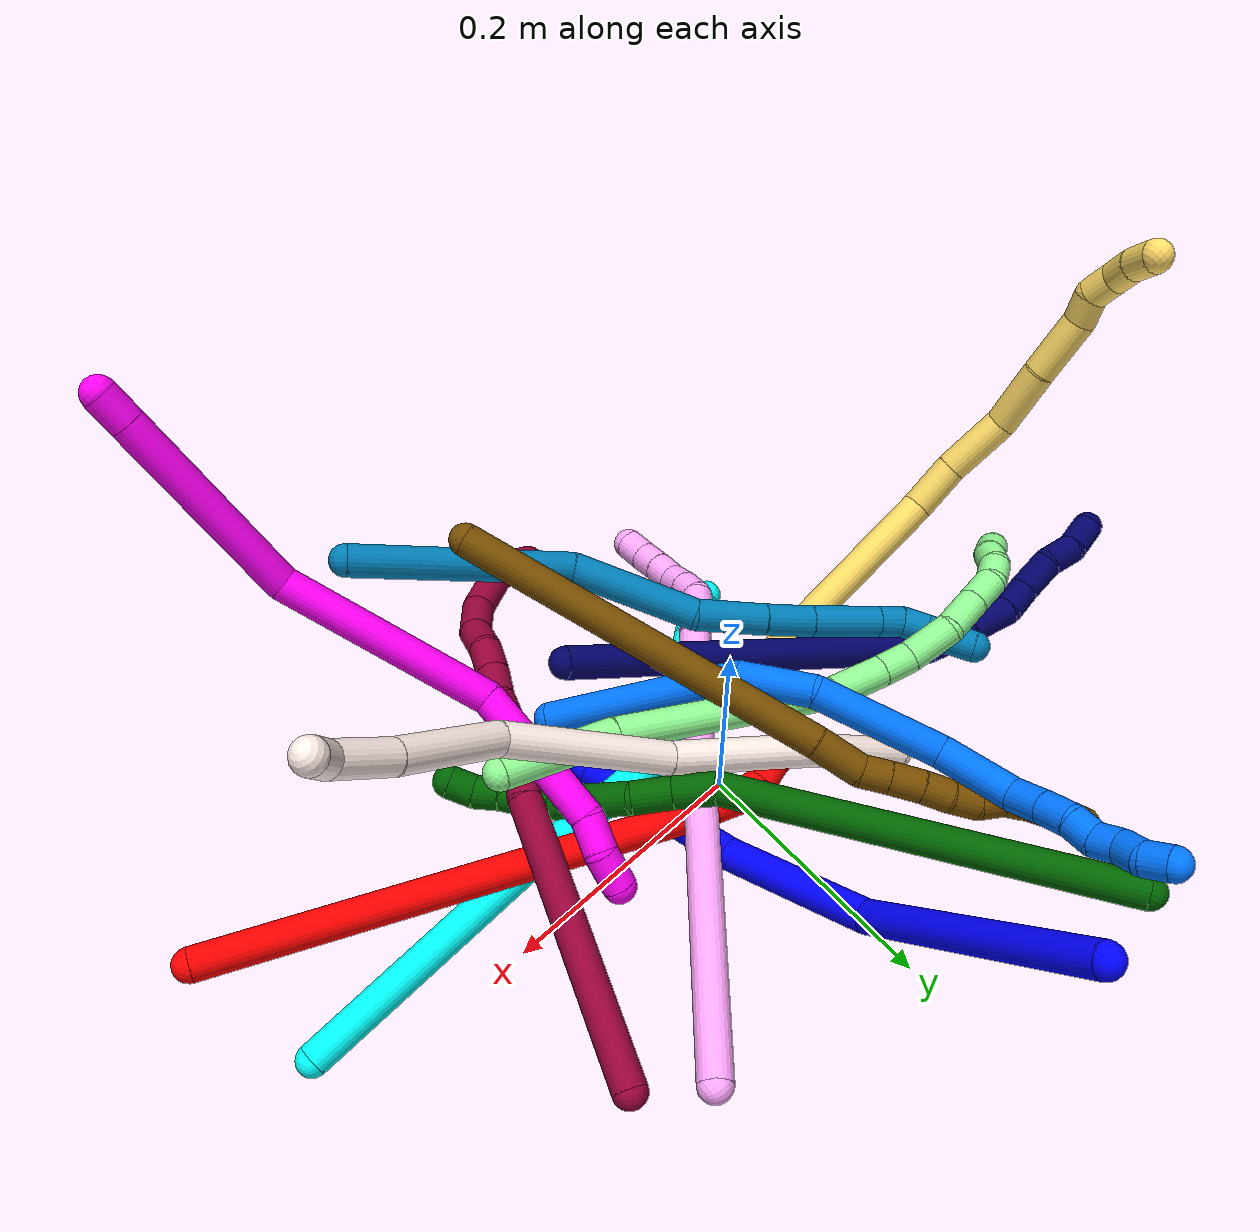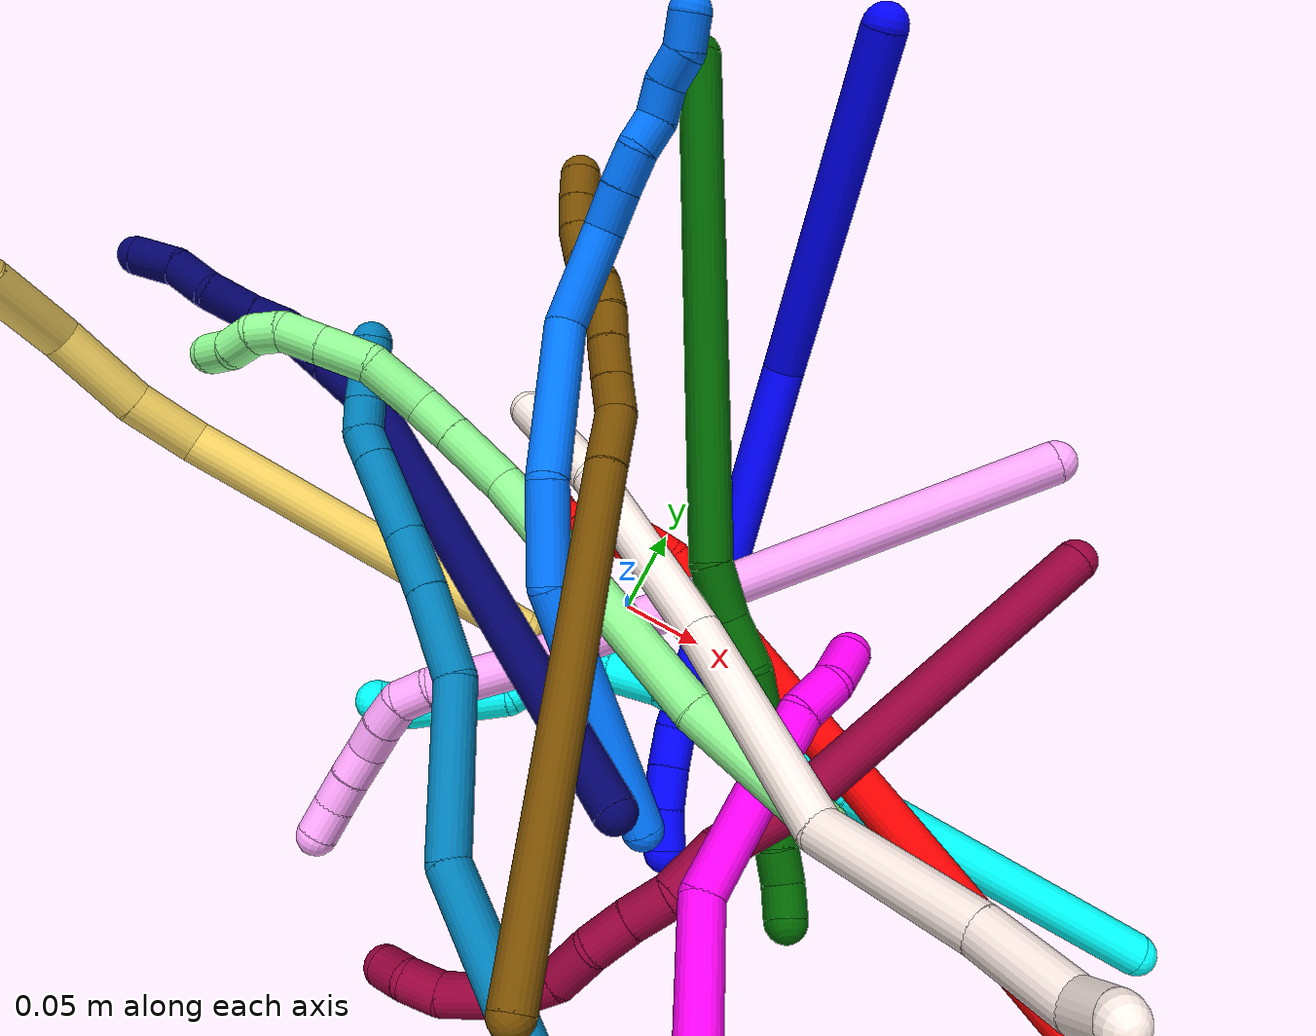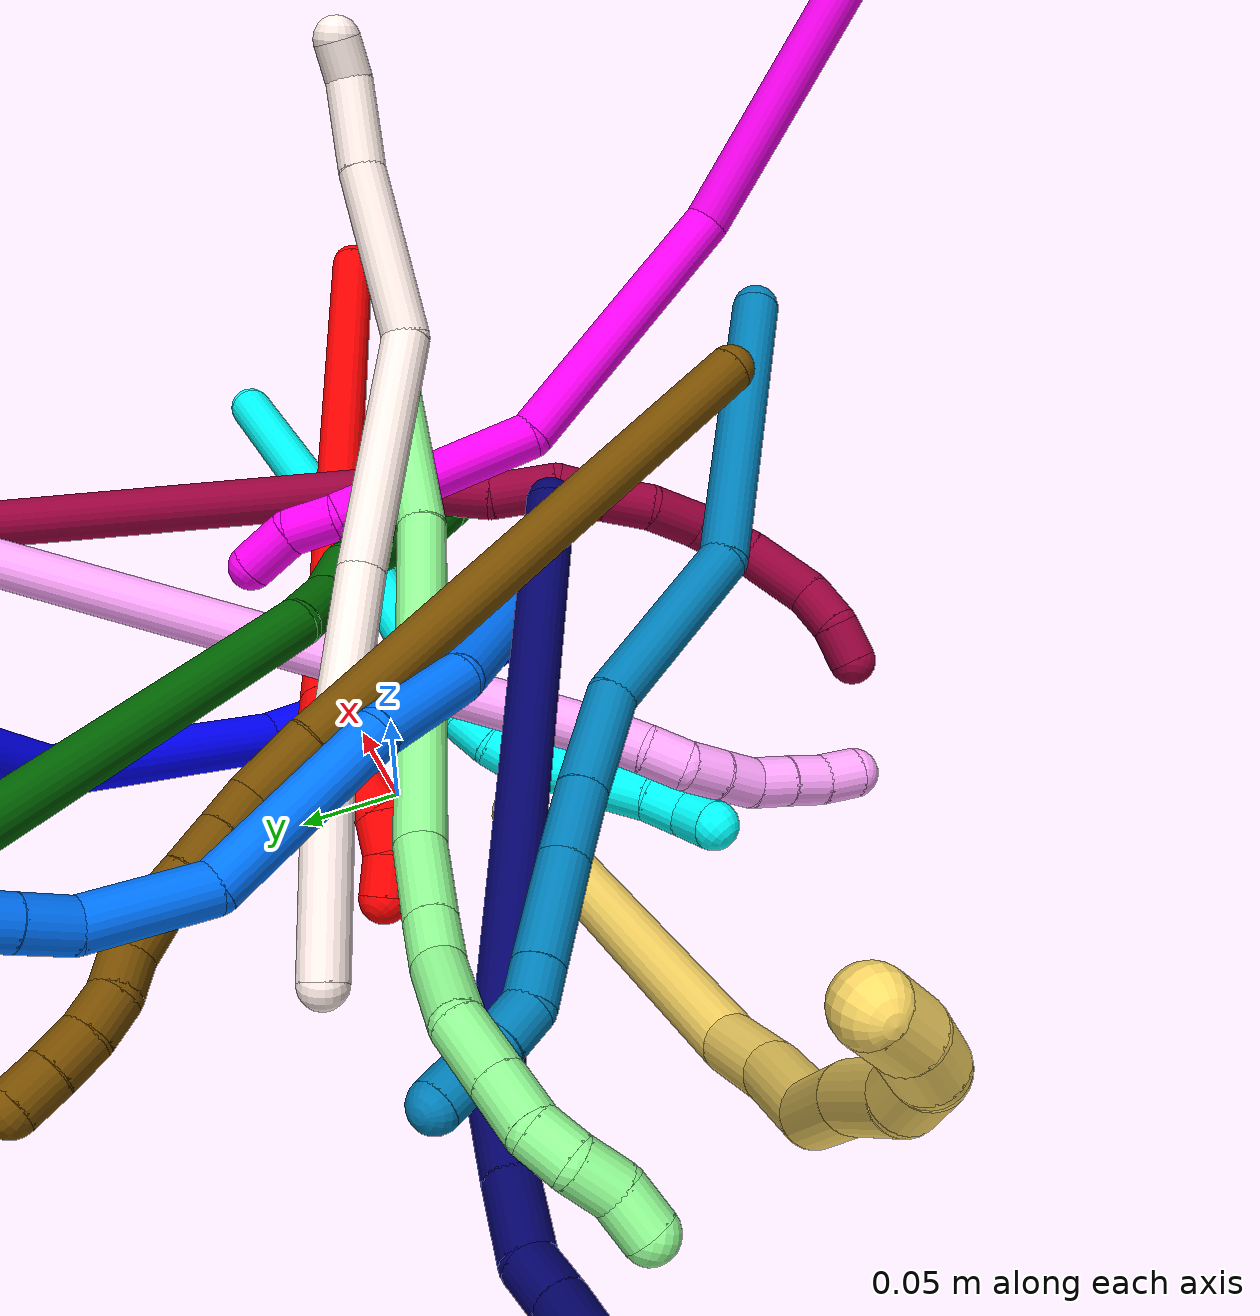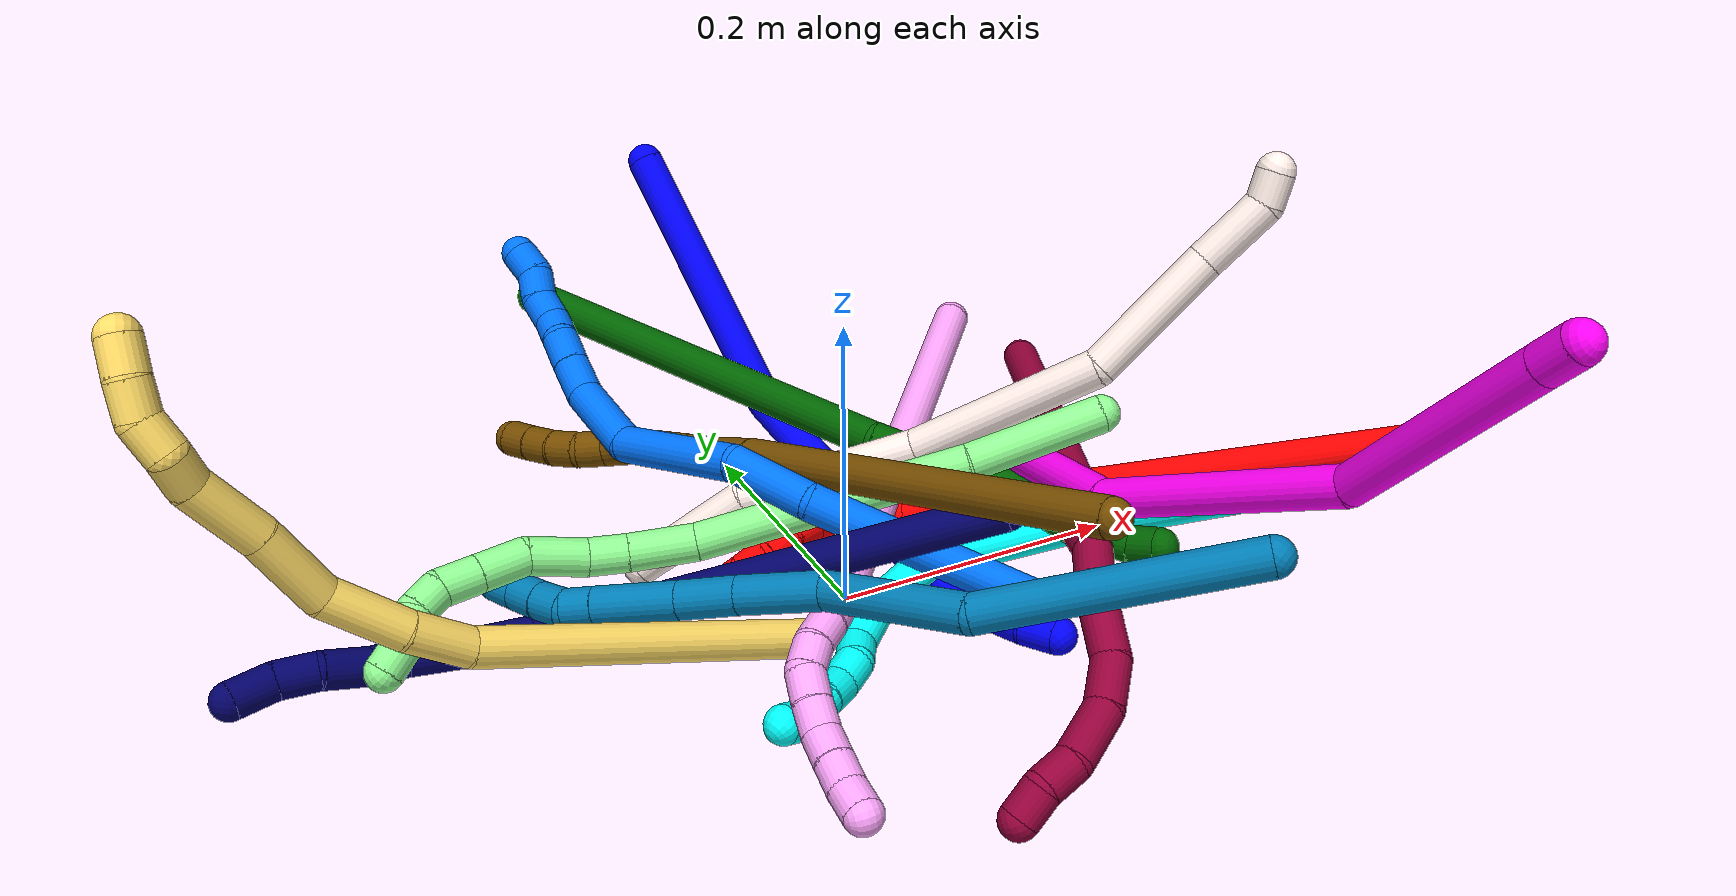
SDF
<sdf version="1.7">
 <world name="default">
  <plugin name="TubeGeneratorPlugin" filename="libtube_generator_plugin.so"/>
  <model name="photoneo_s_sensor">
   <static>1</static>
   <pose>0 0 2 1.57079 1.57079 3.14159</pose>
   <link name="link">
    <inertial><mass>0.1</mass></inertial>
    <sensor name="sensor" type="depth">
     <update_rate>30</update_rate>
     <camera>
      <horizontal_fov>1.22</horizontal_fov>
      <image><width>1920</width><height>1200</height><format>B8G8R8</format></image>
      <clip><near>0.1</near><far>4</far></clip>
      <depth_camera><output>points</output></depth_camera>
     </camera>
     <plugin name="camera_plugin" filename="libgazebo_ros_depth_camera.so">
      <baseline>0.2</baseline>
      <alwaysOn>1</alwaysOn>
      <updateRate>0.0</updateRate>
      <cameraName>camera_ir</cameraName>
      <imageTopicName>/camera/color/image_raw</imageTopicName>
      <cameraInfoTopicName>/camera/color/camera_info</cameraInfoTopicName>
      <depthImageTopicName>/camera/depth/image_raw</depthImageTopicName>
      <depthImageCameraInfoTopicName>/camera/depth/camera_info</depthImageCameraInfoTopicName>
      <pointCloudTopicName>/camera/depth/points</pointCloudTopicName>
      <frameName>fr_optical</frameName>
      <pointCloudCutoff>0.1</pointCloudCutoff>
      <pointCloudCutoffMax>2.0</pointCloudCutoffMax>
      <distortionK1>0</distortionK1>
      <distortionK2>0</distortionK2>
      <distortionK3>0</distortionK3>
      <distortionT1>0</distortionT1>
      <distortionT2>0</distortionT2>
      <CxPrime>0</CxPrime>
      <Cx>0</Cx>
      <Cy>0</Cy>
      <focalLength>0</focalLength>
      <hackBaseline>0</hackBaseline>
     </plugin>
    </sensor>
   </link>
  </model>
  <gravity>0 0 -9.8</gravity>
  <magnetic_field>6e-06 2.3e-05 -4.2e-05</magnetic_field>
  <atmosphere type="adiabatic"/>
  <physics name="default_physics" default="0" type="ode">
   <max_step_size>0.003</max_step_size>
   <real_time_factor>1</real_time_factor>
   <real_time_update_rate>1000</real_time_update_rate>
   <max_contacts>10000</max_contacts>
   <ode>
    <solver>
     <type>quick</type>
     <iters>100</iters>
     <sor>1.3</sor>
     <use_dynamic_moi_rescaling>0</use_dynamic_moi_rescaling>
    </solver>
    <constraints>
     <contact_max_correcting_vel>0</contact_max_correcting_vel>
     <contact_surface_layer>0.001</contact_surface_layer>
     <cfm>0</cfm>
     <erp>0.2</erp>
    </constraints>
   </ode>
  </physics>
  <scene><ambient>0.4 0.4 0.4 1</ambient><background>0.7 0.7 0.7 1</background><shadows>0</shadows></scene>
  <audio><device>default</device></audio>
  <spherical_coordinates>
   <surface_model>EARTH_WGS84</surface_model>
   <latitude_deg>0</latitude_deg>
   <longitude_deg>0</longitude_deg>
   <elevation>0</elevation>
   <heading_deg>0</heading_deg>
  </spherical_coordinates>
  <model name="bin">
   <static>1</static>
   <link name="bottom">
    <collision name="collision-bottom">
     <pose>0 0 -0.01 0 -0 0</pose>
     <geometry><box><size>0.8 0.6 0.02</size></box></geometry>
     <surface>
      <friction><ode><mu>100</mu><mu2>100</mu2></ode></friction>
      <contact><collide_bitmask>65535</collide_bitmask></contact>
     </surface>
    </collision>
   </link>
   <link name="west_wall">
    <collision name="collision-west_wall">
     <pose>-0.41 0 0.1 0 -0 0</pose>
     <geometry><box><size>0.02 0.6 0.2</size></box></geometry>
     <surface>
      <friction><ode><mu>100</mu><mu2>100</mu2></ode></friction>
      <contact><collide_bitmask>65535</collide_bitmask></contact>
     </surface>
    </collision>
   </link>
   <link name="east_wall">
    <collision name="collision-east_wall">
     <pose>0.41 0 0.1 0 -0 0</pose>
     <geometry><box><size>0.02 0.6 0.2</size></box></geometry>
     <surface>
      <friction><ode><mu>100</mu><mu2>100</mu2></ode></friction>
      <contact><collide_bitmask>65535</collide_bitmask></contact>
     </surface>
    </collision>
   </link>
   <link name="south_wall">
    <collision name="collision-south_wall">
     <pose>0 -0.31 0.1 0 -0 0</pose>
     <geometry><box><size>0.8 0.02 0.2</size></box></geometry>
     <surface>
      <friction><ode><mu>100</mu><mu2>100</mu2></ode></friction>
      <contact><collide_bitmask>65535</collide_bitmask></contact>
     </surface>
    </collision>
   </link>
   <link name="north_wall">
    <collision name="collision-north_wall">
     <pose>0 0.31 0.1 0 -0 0</pose>
     <geometry><box><size>0.8 0.02 0.2</size></box></geometry>
     <surface>
      <friction><ode><mu>100</mu><mu2>100</mu2></ode></friction>
      <contact><collide_bitmask>65535</collide_bitmask></contact>
     </surface>
    </collision>
   </link>
  </model>
  <model name="1">
   <static>0</static>
   <link name="1">
    <collision name="collision-cylinder-e_1_1_4">
     <pose>-0.007458 0.019913 -0.097555 -2.94024 -0.074769 0.70919</pose>
     <geometry><cylinder><radius>0.0125</radius><length>0.199692</length></cylinder></geometry>
     <surface>
      <friction><ode><mu>1.16</mu><mu2>1.16</mu2><slip1>0</slip1><slip2>0</slip2></ode></friction>
      <contact><ode><kp>1e+06</kp><kd>1</kd><max_vel>0</max_vel><min_depth>0.001</min_depth></ode></contact>
     </surface>
    </collision>
    <visual name="visual-cylinder-e_1_1_4">
     <pose>-0.007458 0.019913 -0.097555 -2.94024 -0.074769 0.70919</pose>
     <geometry><cylinder><radius>0.0125</radius><length>0.199692</length></cylinder></geometry>
     <material><ambient>0 0 1 1</ambient></material>
    </visual>
    <collision name="collision-cylinder-e_2_4_5">
     <pose>-0.015476 0.025177 -0.253186 2.8945 -0.009333 -0.075121</pose>
     <geometry><cylinder><radius>0.0125</radius><length>0.119795</length></cylinder></geometry>
     <surface>
      <friction><ode><mu>1.16</mu><mu2>1.16</mu2><slip1>0</slip1><slip2>0</slip2></ode></friction>
      <contact><ode><kp>1e+06</kp><kd>1</kd><max_vel>0</max_vel><min_depth>0.001</min_depth></ode></contact>
     </surface>
    </collision>
    <visual name="visual-cylinder-e_2_4_5">
     <pose>-0.015476 0.025177 -0.253186 2.8945 -0.009333 -0.075121</pose>
     <geometry><cylinder><radius>0.0125</radius><length>0.119795</length></cylinder></geometry>
     <material><ambient>0 0 1 1</ambient></material>
    </visual>
    <collision name="collision-cylinder-e_3_5_6">
     <pose>-0.016112 -0.014723 -0.358857 2.65384 -0.001436 -0.005772</pose>
     <geometry><cylinder><radius>0.0125</radius><length>0.107757</length></cylinder></geometry>
     <surface>
      <friction><ode><mu>1.16</mu><mu2>1.16</mu2><slip1>0</slip1><slip2>0</slip2></ode></friction>
      <contact><ode><kp>1e+06</kp><kd>1</kd><max_vel>0</max_vel><min_depth>0.001</min_depth></ode></contact>
     </surface>
    </collision>
    <visual name="visual-cylinder-e_3_5_6">
     <pose>-0.016112 -0.014723 -0.358857 2.65384 -0.001436 -0.005772</pose>
     <geometry><cylinder><radius>0.0125</radius><length>0.107757</length></cylinder></geometry>
     <material><ambient>0 0 1 1</ambient></material>
    </visual>
    <collision name="collision-cylinder-e_4_6_7">
     <pose>-0.014472 -0.046889 -0.415995 2.51441 0.144696 0.439745</pose>
     <geometry><cylinder><radius>0.0125</radius><length>0.02382</length></cylinder></geometry>
     <surface>
      <friction><ode><mu>1.16</mu><mu2>1.16</mu2><slip1>0</slip1><slip2>0</slip2></ode></friction>
      <contact><ode><kp>1e+06</kp><kd>1</kd><max_vel>0</max_vel><min_depth>0.001</min_depth></ode></contact>
     </surface>
    </collision>
    <visual name="visual-cylinder-e_4_6_7">
     <pose>-0.014472 -0.046889 -0.415995 2.51441 0.144696 0.439745</pose>
     <geometry><cylinder><radius>0.0125</radius><length>0.02382</length></cylinder></geometry>
     <material><ambient>0 0 1 1</ambient></material>
    </visual>
    <collision name="collision-cylinder-e_5_7_8">
     <pose>-0.010173 -0.061182 -0.435459 2.50223 0.205895 0.605022</pose>
     <geometry><cylinder><radius>0.0125</radius><length>0.025259</length></cylinder></geometry>
     <surface>
      <friction><ode><mu>1.16</mu><mu2>1.16</mu2><slip1>0</slip1><slip2>0</slip2></ode></friction>
      <contact><ode><kp>1e+06</kp><kd>1</kd><max_vel>0</max_vel><min_depth>0.001</min_depth></ode></contact>
     </surface>
    </collision>
    <visual name="visual-cylinder-e_5_7_8">
     <pose>-0.010173 -0.061182 -0.435459 2.50223 0.205895 0.605022</pose>
     <geometry><cylinder><radius>0.0125</radius><length>0.025259</length></cylinder></geometry>
     <material><ambient>0 0 1 1</ambient></material>
    </visual>
    <collision name="collision-cylinder-e_6_8_2">
     <pose>-0.00339 -0.074972 -0.4544 2.52353 0.362725 1.04275</pose>
     <geometry><cylinder><radius>0.0125</radius><length>0.023678</length></cylinder></geometry>
     <surface>
      <friction><ode><mu>1.16</mu><mu2>1.16</mu2><slip1>0</slip1><slip2>0</slip2></ode></friction>
      <contact><ode><kp>1e+06</kp><kd>1</kd><max_vel>0</max_vel><min_depth>0.001</min_depth></ode></contact>
     </surface>
    </collision>
    <visual name="visual-cylinder-e_6_8_2">
     <pose>-0.00339 -0.074972 -0.4544 2.52353 0.362725 1.04275</pose>
     <geometry><cylinder><radius>0.0125</radius><length>0.023678</length></cylinder></geometry>
     <material><ambient>0 0 1 1</ambient></material>
    </visual>
    <collision name="collision-sphere-2">
     <pose>0.00081 -0.081386 -0.463421 0 -0 0</pose>
     <geometry><sphere><radius>0.0125</radius></sphere></geometry>
     <surface>
      <friction><ode><mu>1.16</mu><mu2>1.16</mu2><slip1>0</slip1><slip2>0</slip2></ode></friction>
      <contact><ode><kp>1e+06</kp><kd>1</kd><max_vel>0</max_vel><min_depth>0.001</min_depth></ode></contact>
     </surface>
    </collision>
    <visual name="visual-sphere-2">
     <pose>0.00081 -0.081386 -0.463421 0 -0 0</pose>
     <geometry><sphere><radius>0.0125</radius></sphere></geometry>
     <material><ambient>0 0 1 1</ambient></material>
    </visual>
    <collision name="collision-sphere-4">
     <pose>-0.014917 0.039826 -0.19511 0 -0 0</pose>
     <geometry><sphere><radius>0.0125</radius></sphere></geometry>
     <surface>
      <friction><ode><mu>1.16</mu><mu2>1.16</mu2><slip1>0</slip1><slip2>0</slip2></ode></friction>
      <contact><ode><kp>1e+06</kp><kd>1</kd><max_vel>0</max_vel><min_depth>0.001</min_depth></ode></contact>
     </surface>
    </collision>
    <visual name="visual-sphere-4">
     <pose>-0.014917 0.039826 -0.19511 0 -0 0</pose>
     <geometry><sphere><radius>0.0125</radius></sphere></geometry>
     <material><ambient>0 0 1 1</ambient></material>
    </visual>
    <collision name="collision-sphere-1">
     <geometry><sphere><radius>0.0125</radius></sphere></geometry>
     <surface>
      <friction><ode><mu>1.16</mu><mu2>1.16</mu2><slip1>0</slip1><slip2>0</slip2></ode></friction>
      <contact><ode><kp>1e+06</kp><kd>1</kd><max_vel>0</max_vel><min_depth>0.001</min_depth></ode></contact>
     </surface>
    </collision>
    <visual name="visual-sphere-1">
     <geometry><sphere><radius>0.0125</radius></sphere></geometry>
     <material><ambient>0 0 1 1</ambient></material>
    </visual>
    <collision name="collision-sphere-8">
     <pose>-0.007591 -0.068559 -0.44538 0 -0 0</pose>
     <geometry><sphere><radius>0.0125</radius></sphere></geometry>
     <surface>
      <friction><ode><mu>1.16</mu><mu2>1.16</mu2><slip1>0</slip1><slip2>0</slip2></ode></friction>
      <contact><ode><kp>1e+06</kp><kd>1</kd><max_vel>0</max_vel><min_depth>0.001</min_depth></ode></contact>
     </surface>
    </collision>
    <visual name="visual-sphere-8">
     <pose>-0.007591 -0.068559 -0.44538 0 -0 0</pose>
     <geometry><sphere><radius>0.0125</radius></sphere></geometry>
     <material><ambient>0 0 1 1</ambient></material>
    </visual>
    <collision name="collision-sphere-5">
     <pose>-0.016035 0.010527 -0.311262 0 -0 0</pose>
     <geometry><sphere><radius>0.0125</radius></sphere></geometry>
     <surface>
      <friction><ode><mu>1.16</mu><mu2>1.16</mu2><slip1>0</slip1><slip2>0</slip2></ode></friction>
      <contact><ode><kp>1e+06</kp><kd>1</kd><max_vel>0</max_vel><min_depth>0.001</min_depth></ode></contact>
     </surface>
    </collision>
    <visual name="visual-sphere-5">
     <pose>-0.016035 0.010527 -0.311262 0 -0 0</pose>
     <geometry><sphere><radius>0.0125</radius></sphere></geometry>
     <material><ambient>0 0 1 1</ambient></material>
    </visual>
    <collision name="collision-sphere-6">
     <pose>-0.01619 -0.039972 -0.406453 0 -0 0</pose>
     <geometry><sphere><radius>0.0125</radius></sphere></geometry>
     <surface>
      <friction><ode><mu>1.16</mu><mu2>1.16</mu2><slip1>0</slip1><slip2>0</slip2></ode></friction>
      <contact><ode><kp>1e+06</kp><kd>1</kd><max_vel>0</max_vel><min_depth>0.001</min_depth></ode></contact>
     </surface>
    </collision>
    <visual name="visual-sphere-6">
     <pose>-0.01619 -0.039972 -0.406453 0 -0 0</pose>
     <geometry><sphere><radius>0.0125</radius></sphere></geometry>
     <material><ambient>0 0 1 1</ambient></material>
    </visual>
    <collision name="collision-sphere-7">
     <pose>-0.012755 -0.053805 -0.425538 0 -0 0</pose>
     <geometry><sphere><radius>0.0125</radius></sphere></geometry>
     <surface>
      <friction><ode><mu>1.16</mu><mu2>1.16</mu2><slip1>0</slip1><slip2>0</slip2></ode></friction>
      <contact><ode><kp>1e+06</kp><kd>1</kd><max_vel>0</max_vel><min_depth>0.001</min_depth></ode></contact>
     </surface>
    </collision>
    <visual name="visual-sphere-7">
     <pose>-0.012755 -0.053805 -0.425538 0 -0 0</pose>
     <geometry><sphere><radius>0.0125</radius></sphere></geometry>
     <material><ambient>0 0 1 1</ambient></material>
    </visual>
    <inertial>
     <pose>-0.011523 0.001937 -0.240296 0 -0 0</pose>
     <mass>0.5</mass>
     <inertia>
      <ixx>0.001197</ixx>
      <ixy>0</ixy>
      <ixz>0</ixz>
      <iyy>-0.000313</iyy>
      <iyz>0</iyz>
      <izz>-2.9e-05</izz>
     </inertia>
    </inertial>
   </link>
   <pose>-0.013926 0.295284 0.211845 -0.960023 -0.160067 0.170393</pose>
  </model>
  <model name="2">
   <static>0</static>
   <link name="2">
    <collision name="collision-cylinder-e_1_1_4">
     <pose>-0.088012 0.017736 -0.155896 -3.02831 -0.511203 2.71425</pose>
     <geometry><cylinder><radius>0.0125</radius><length>0.359801</length></cylinder></geometry>
     <surface>
      <friction><ode><mu>1.16</mu><mu2>1.16</mu2><slip1>0</slip1><slip2>0</slip2></ode></friction>
      <contact><ode><kp>1e+06</kp><kd>1</kd><max_vel>0</max_vel><min_depth>0.001</min_depth></ode></contact>
     </surface>
    </collision>
    <visual name="visual-cylinder-e_1_1_4">
     <pose>-0.088012 0.017736 -0.155896 -3.02831 -0.511203 2.71425</pose>
     <geometry><cylinder><radius>0.0125</radius><length>0.359801</length></cylinder></geometry>
     <material><ambient>1 0 0 1</ambient></material>
    </visual>
    <collision name="collision-cylinder-e_2_4_5">
     <pose>-0.180778 0.037908 -0.320346 -2.86424 -0.490787 2.12473</pose>
     <geometry><cylinder><radius>0.0125</radius><length>0.020171</length></cylinder></geometry>
     <surface>
      <friction><ode><mu>1.16</mu><mu2>1.16</mu2><slip1>0</slip1><slip2>0</slip2></ode></friction>
      <contact><ode><kp>1e+06</kp><kd>1</kd><max_vel>0</max_vel><min_depth>0.001</min_depth></ode></contact>
     </surface>
    </collision>
    <visual name="visual-cylinder-e_2_4_5">
     <pose>-0.180778 0.037908 -0.320346 -2.86424 -0.490787 2.12473</pose>
     <geometry><cylinder><radius>0.0125</radius><length>0.020171</length></cylinder></geometry>
     <material><ambient>1 0 0 1</ambient></material>
    </visual>
    <collision name="collision-cylinder-e_3_5_6">
     <pose>-0.19037 0.04295 -0.337268 -2.83963 -0.504511 2.07514</pose>
     <geometry><cylinder><radius>0.0125</radius><length>0.020021</length></cylinder></geometry>
     <surface>
      <friction><ode><mu>1.16</mu><mu2>1.16</mu2><slip1>0</slip1><slip2>0</slip2></ode></friction>
      <contact><ode><kp>1e+06</kp><kd>1</kd><max_vel>0</max_vel><min_depth>0.001</min_depth></ode></contact>
     </surface>
    </collision>
    <visual name="visual-cylinder-e_3_5_6">
     <pose>-0.19037 0.04295 -0.337268 -2.83963 -0.504511 2.07514</pose>
     <geometry><cylinder><radius>0.0125</radius><length>0.020021</length></cylinder></geometry>
     <material><ambient>1 0 0 1</ambient></material>
    </visual>
    <collision name="collision-cylinder-e_4_6_7">
     <pose>-0.202535 0.046475 -0.352382 -3.00616 -0.821906 2.8328</pose>
     <geometry><cylinder><radius>0.0125</radius><length>0.020004</length></cylinder></geometry>
     <surface>
      <friction><ode><mu>1.16</mu><mu2>1.16</mu2><slip1>0</slip1><slip2>0</slip2></ode></friction>
      <contact><ode><kp>1e+06</kp><kd>1</kd><max_vel>0</max_vel><min_depth>0.001</min_depth></ode></contact>
     </surface>
    </collision>
    <visual name="visual-cylinder-e_4_6_7">
     <pose>-0.202535 0.046475 -0.352382 -3.00616 -0.821906 2.8328</pose>
     <geometry><cylinder><radius>0.0125</radius><length>0.020004</length></cylinder></geometry>
     <material><ambient>1 0 0 1</ambient></material>
    </visual>
    <collision name="collision-cylinder-e_5_7_8">
     <pose>-0.219032 0.048846 -0.362842 -2.76899 -1.1608 2.5818</pose>
     <geometry><cylinder><radius>0.0125</radius><length>0.020001</length></cylinder></geometry>
     <surface>
      <friction><ode><mu>1.16</mu><mu2>1.16</mu2><slip1>0</slip1><slip2>0</slip2></ode></friction>
      <contact><ode><kp>1e+06</kp><kd>1</kd><max_vel>0</max_vel><min_depth>0.001</min_depth></ode></contact>
     </surface>
    </collision>
    <visual name="visual-cylinder-e_5_7_8">
     <pose>-0.219032 0.048846 -0.362842 -2.76899 -1.1608 2.5818</pose>
     <geometry><cylinder><radius>0.0125</radius><length>0.020001</length></cylinder></geometry>
     <material><ambient>1 0 0 1</ambient></material>
    </visual>
    <collision name="collision-cylinder-e_6_8_9">
     <pose>-0.236994 0.048543 -0.37099 2.76507 -1.07372 -2.52199</pose>
     <geometry><cylinder><radius>0.0125</radius><length>0.020001</length></cylinder></geometry>
     <surface>
      <friction><ode><mu>1.16</mu><mu2>1.16</mu2><slip1>0</slip1><slip2>0</slip2></ode></friction>
      <contact><ode><kp>1e+06</kp><kd>1</kd><max_vel>0</max_vel><min_depth>0.001</min_depth></ode></contact>
     </surface>
    </collision>
    <visual name="visual-cylinder-e_6_8_9">
     <pose>-0.236994 0.048543 -0.37099 2.76507 -1.07372 -2.52199</pose>
     <geometry><cylinder><radius>0.0125</radius><length>0.020001</length></cylinder></geometry>
     <material><ambient>1 0 0 1</ambient></material>
    </visual>
    <collision name="collision-cylinder-e_7_9_10">
     <pose>-0.252074 0.043144 -0.382291 2.65345 -0.68021 -1.91508</pose>
     <geometry><cylinder><radius>0.0125</radius><length>0.02</length></cylinder></geometry>
     <surface>
      <friction><ode><mu>1.16</mu><mu2>1.16</mu2><slip1>0</slip1><slip2>0</slip2></ode></friction>
      <contact><ode><kp>1e+06</kp><kd>1</kd><max_vel>0</max_vel><min_depth>0.001</min_depth></ode></contact>
     </surface>
    </collision>
    <visual name="visual-cylinder-e_7_9_10">
     <pose>-0.252074 0.043144 -0.382291 2.65345 -0.68021 -1.91508</pose>
     <geometry><cylinder><radius>0.0125</radius><length>0.02</length></cylinder></geometry>
     <material><ambient>1 0 0 1</ambient></material>
    </visual>
    <collision name="collision-cylinder-e_8_10_2">
     <pose>-0.261709 0.034583 -0.397199 2.59304 -0.341098 -1.09852</pose>
     <geometry><cylinder><radius>0.0125</radius><length>0.020001</length></cylinder></geometry>
     <surface>
      <friction><ode><mu>1.16</mu><mu2>1.16</mu2><slip1>0</slip1><slip2>0</slip2></ode></friction>
      <contact><ode><kp>1e+06</kp><kd>1</kd><max_vel>0</max_vel><min_depth>0.001</min_depth></ode></contact>
     </surface>
    </collision>
    <visual name="visual-cylinder-e_8_10_2">
     <pose>-0.261709 0.034583 -0.397199 2.59304 -0.341098 -1.09852</pose>
     <geometry><cylinder><radius>0.0125</radius><length>0.020001</length></cylinder></geometry>
     <material><ambient>1 0 0 1</ambient></material>
    </visual>
    <collision name="collision-sphere-2">
     <pose>-0.265055 0.029669 -0.405241 0 -0 0</pose>
     <geometry><sphere><radius>0.0125</radius></sphere></geometry>
     <surface>
      <friction><ode><mu>1.16</mu><mu2>1.16</mu2><slip1>0</slip1><slip2>0</slip2></ode></friction>
      <contact><ode><kp>1e+06</kp><kd>1</kd><max_vel>0</max_vel><min_depth>0.001</min_depth></ode></contact>
     </surface>
    </collision>
    <visual name="visual-sphere-2">
     <pose>-0.265055 0.029669 -0.405241 0 -0 0</pose>
     <geometry><sphere><radius>0.0125</radius></sphere></geometry>
     <material><ambient>1 0 0 1</ambient></material>
    </visual>
    <collision name="collision-sphere-10">
     <pose>-0.258364 0.039498 -0.389157 0 -0 0</pose>
     <geometry><sphere><radius>0.0125</radius></sphere></geometry>
     <surface>
      <friction><ode><mu>1.16</mu><mu2>1.16</mu2><slip1>0</slip1><slip2>0</slip2></ode></friction>
      <contact><ode><kp>1e+06</kp><kd>1</kd><max_vel>0</max_vel><min_depth>0.001</min_depth></ode></contact>
     </surface>
    </collision>
    <visual name="visual-sphere-10">
     <pose>-0.258364 0.039498 -0.389157 0 -0 0</pose>
     <geometry><sphere><radius>0.0125</radius></sphere></geometry>
     <material><ambient>1 0 0 1</ambient></material>
    </visual>
    <collision name="collision-sphere-9">
     <pose>-0.245785 0.04679 -0.375424 0 -0 0</pose>
     <geometry><sphere><radius>0.0125</radius></sphere></geometry>
     <surface>
      <friction><ode><mu>1.16</mu><mu2>1.16</mu2><slip1>0</slip1><slip2>0</slip2></ode></friction>
      <contact><ode><kp>1e+06</kp><kd>1</kd><max_vel>0</max_vel><min_depth>0.001</min_depth></ode></contact>
     </surface>
    </collision>
    <visual name="visual-sphere-9">
     <pose>-0.245785 0.04679 -0.375424 0 -0 0</pose>
     <geometry><sphere><radius>0.0125</radius></sphere></geometry>
     <material><ambient>1 0 0 1</ambient></material>
    </visual>
    <collision name="collision-sphere-4">
     <pose>-0.176024 0.035472 -0.311792 0 -0 0</pose>
     <geometry><sphere><radius>0.0125</radius></sphere></geometry>
     <surface>
      <friction><ode><mu>1.16</mu><mu2>1.16</mu2><slip1>0</slip1><slip2>0</slip2></ode></friction>
      <contact><ode><kp>1e+06</kp><kd>1</kd><max_vel>0</max_vel><min_depth>0.001</min_depth></ode></contact>
     </surface>
    </collision>
    <visual name="visual-sphere-4">
     <pose>-0.176024 0.035472 -0.311792 0 -0 0</pose>
     <geometry><sphere><radius>0.0125</radius></sphere></geometry>
     <material><ambient>1 0 0 1</ambient></material>
    </visual>
    <collision name="collision-sphere-1">
     <geometry><sphere><radius>0.0125</radius></sphere></geometry>
     <surface>
      <friction><ode><mu>1.16</mu><mu2>1.16</mu2><slip1>0</slip1><slip2>0</slip2></ode></friction>
      <contact><ode><kp>1e+06</kp><kd>1</kd><max_vel>0</max_vel><min_depth>0.001</min_depth></ode></contact>
     </surface>
    </collision>
    <visual name="visual-sphere-1">
     <geometry><sphere><radius>0.0125</radius></sphere></geometry>
     <material><ambient>1 0 0 1</ambient></material>
    </visual>
    <collision name="collision-sphere-8">
     <pose>-0.228204 0.050297 -0.366555 0 -0 0</pose>
     <geometry><sphere><radius>0.0125</radius></sphere></geometry>
     <surface>
      <friction><ode><mu>1.16</mu><mu2>1.16</mu2><slip1>0</slip1><slip2>0</slip2></ode></friction>
      <contact><ode><kp>1e+06</kp><kd>1</kd><max_vel>0</max_vel><min_depth>0.001</min_depth></ode></contact>
     </surface>
    </collision>
    <visual name="visual-sphere-8">
     <pose>-0.228204 0.050297 -0.366555 0 -0 0</pose>
     <geometry><sphere><radius>0.0125</radius></sphere></geometry>
     <material><ambient>1 0 0 1</ambient></material>
    </visual>
    <collision name="collision-sphere-5">
     <pose>-0.185531 0.040343 -0.328901 0 -0 0</pose>
     <geometry><sphere><radius>0.0125</radius></sphere></geometry>
     <surface>
      <friction><ode><mu>1.16</mu><mu2>1.16</mu2><slip1>0</slip1><slip2>0</slip2></ode></friction>
      <contact><ode><kp>1e+06</kp><kd>1</kd><max_vel>0</max_vel><min_depth>0.001</min_depth></ode></contact>
     </surface>
    </collision>
    <visual name="visual-sphere-5">
     <pose>-0.185531 0.040343 -0.328901 0 -0 0</pose>
     <geometry><sphere><radius>0.0125</radius></sphere></geometry>
     <material><ambient>1 0 0 1</ambient></material>
    </visual>
    <collision name="collision-sphere-6">
     <pose>-0.195209 0.045556 -0.345635 0 -0 0</pose>
     <geometry><sphere><radius>0.0125</radius></sphere></geometry>
     <surface>
      <friction><ode><mu>1.16</mu><mu2>1.16</mu2><slip1>0</slip1><slip2>0</slip2></ode></friction>
      <contact><ode><kp>1e+06</kp><kd>1</kd><max_vel>0</max_vel><min_depth>0.001</min_depth></ode></contact>
     </surface>
    </collision>
    <visual name="visual-sphere-6">
     <pose>-0.195209 0.045556 -0.345635 0 -0 0</pose>
     <geometry><sphere><radius>0.0125</radius></sphere></geometry>
     <material><ambient>1 0 0 1</ambient></material>
    </visual>
    <collision name="collision-sphere-7">
     <pose>-0.20986 0.047394 -0.359129 0 -0 0</pose>
     <geometry><sphere><radius>0.0125</radius></sphere></geometry>
     <surface>
      <friction><ode><mu>1.16</mu><mu2>1.16</mu2><slip1>0</slip1><slip2>0</slip2></ode></friction>
      <contact><ode><kp>1e+06</kp><kd>1</kd><max_vel>0</max_vel><min_depth>0.001</min_depth></ode></contact>
     </surface>
    </collision>
    <visual name="visual-sphere-7">
     <pose>-0.20986 0.047394 -0.359129 0 -0 0</pose>
     <geometry><sphere><radius>0.0125</radius></sphere></geometry>
     <material><ambient>1 0 0 1</ambient></material>
    </visual>
    <inertial>
     <pose>-0.125146 0.024876 -0.213244 0 -0 0</pose>
     <mass>0.5</mass>
     <inertia>
      <ixx>-0.001707</ixx>
      <ixy>0</ixy>
      <ixz>0</ixz>
      <iyy>0.005029</iyy>
      <iyz>0</iyz>
      <izz>0.001497</izz>
     </inertia>
    </inertial>
   </link>
   <pose>0.380127 -0.12066 0.083753 1.40369 -0.129908 0.675523</pose>
  </model>
  <model name="3">
   <static>0</static>
   <link name="3">
    <collision name="collision-cylinder-e_1_1_4">
     <pose>-0.049913 0.018921 -0.081487 -2.91344 -0.537953 2.35376</pose>
     <geometry><cylinder><radius>0.0125</radius><length>0.194827</length></cylinder></geometry>
     <surface>
      <friction><ode><mu>1.16</mu><mu2>1.16</mu2><slip1>0</slip1><slip2>0</slip2></ode></friction>
      <contact><ode><kp>1e+06</kp><kd>1</kd><max_vel>0</max_vel><min_depth>0.001</min_depth></ode></contact>
     </surface>
    </collision>
    <visual name="visual-cylinder-e_1_1_4">
     <pose>-0.049913 0.018921 -0.081487 -2.91344 -0.537953 2.35376</pose>
     <geometry><cylinder><radius>0.0125</radius><length>0.194827</length></cylinder></geometry>
     <material><ambient>0.003922 1 0.996078 1</ambient></material>
    </visual>
    <collision name="collision-cylinder-e_2_4_5">
     <pose>-0.126553 0.052378 -0.21639 -2.8759 -0.4498 2.08424</pose>
     <geometry><cylinder><radius>0.0125</radius><length>0.122946</length></cylinder></geometry>
     <surface>
      <friction><ode><mu>1.16</mu><mu2>1.16</mu2><slip1>0</slip1><slip2>0</slip2></ode></friction>
      <contact><ode><kp>1e+06</kp><kd>1</kd><max_vel>0</max_vel><min_depth>0.001</min_depth></ode></contact>
     </surface>
    </collision>
    <visual name="visual-cylinder-e_2_4_5">
     <pose>-0.126553 0.052378 -0.21639 -2.8759 -0.4498 2.08424</pose>
     <geometry><cylinder><radius>0.0125</radius><length>0.122946</length></cylinder></geometry>
     <material><ambient>0.003922 1 0.996078 1</ambient></material>
    </visual>
    <collision name="collision-cylinder-e_3_5_6">
     <pose>-0.153299 0.069143 -0.285978 -3.00466 -0.001099 0.016027</pose>
     <geometry><cylinder><radius>0.0125</radius><length>0.03265</length></cylinder></geometry>
     <surface>
      <friction><ode><mu>1.16</mu><mu2>1.16</mu2><slip1>0</slip1><slip2>0</slip2></ode></friction>
      <contact><ode><kp>1e+06</kp><kd>1</kd><max_vel>0</max_vel><min_depth>0.001</min_depth></ode></contact>
     </surface>
    </collision>
    <visual name="visual-cylinder-e_3_5_6">
     <pose>-0.153299 0.069143 -0.285978 -3.00466 -0.001099 0.016027</pose>
     <geometry><cylinder><radius>0.0125</radius><length>0.03265</length></cylinder></geometry>
     <material><ambient>0.003922 1 0.996078 1</ambient></material>
    </visual>
    <collision name="collision-cylinder-e_4_6_7">
     <pose>-0.154217 0.070141 -0.312356 3.02164 -0.087404 -1.25888</pose>
     <geometry><cylinder><radius>0.0125</radius><length>0.020639</length></cylinder></geometry>
     <surface>
      <friction><ode><mu>1.16</mu><mu2>1.16</mu2><slip1>0</slip1><slip2>0</slip2></ode></friction>
      <contact><ode><kp>1e+06</kp><kd>1</kd><max_vel>0</max_vel><min_depth>0.001</min_depth></ode></contact>
     </surface>
    </collision>
    <visual name="visual-cylinder-e_4_6_7">
     <pose>-0.154217 0.070141 -0.312356 3.02164 -0.087404 -1.25888</pose>
     <geometry><cylinder><radius>0.0125</radius><length>0.020639</length></cylinder></geometry>
     <material><ambient>0.003922 1 0.996078 1</ambient></material>
    </visual>
    <collision name="collision-cylinder-e_5_7_8">
     <pose>-0.154646 0.06493 -0.334745 2.82575 0.036788 0.230017</pose>
     <geometry><cylinder><radius>0.0125</radius><length>0.02565</length></cylinder></geometry>
     <surface>
      <friction><ode><mu>1.16</mu><mu2>1.16</mu2><slip1>0</slip1><slip2>0</slip2></ode></friction>
      <contact><ode><kp>1e+06</kp><kd>1</kd><max_vel>0</max_vel><min_depth>0.001</min_depth></ode></contact>
     </surface>
    </collision>
    <visual name="visual-cylinder-e_5_7_8">
     <pose>-0.154646 0.06493 -0.334745 2.82575 0.036788 0.230017</pose>
     <geometry><cylinder><radius>0.0125</radius><length>0.02565</length></cylinder></geometry>
     <material><ambient>0.003922 1 0.996078 1</ambient></material>
    </visual>
    <collision name="collision-cylinder-e_6_8_9">
     <pose>-0.15569 0.053146 -0.35451 2.34193 -0.138337 -0.324986</pose>
     <geometry><cylinder><radius>0.0125</radius><length>0.021971</length></cylinder></geometry>
     <surface>
      <friction><ode><mu>1.16</mu><mu2>1.16</mu2><slip1>0</slip1><slip2>0</slip2></ode></friction>
      <contact><ode><kp>1e+06</kp><kd>1</kd><max_vel>0</max_vel><min_depth>0.001</min_depth></ode></contact>
     </surface>
    </collision>
    <visual name="visual-cylinder-e_6_8_9">
     <pose>-0.15569 0.053146 -0.35451 2.34193 -0.138337 -0.324986</pose>
     <geometry><cylinder><radius>0.0125</radius><length>0.021971</length></cylinder></geometry>
     <material><ambient>0.003922 1 0.996078 1</ambient></material>
    </visual>
    <collision name="collision-cylinder-e_7_9_10">
     <pose>-0.15859 0.041814 -0.371982 2.79876 -0.131156 -0.725164</pose>
     <geometry><cylinder><radius>0.0125</radius><length>0.021181</length></cylinder></geometry>
     <surface>
      <friction><ode><mu>1.16</mu><mu2>1.16</mu2><slip1>0</slip1><slip2>0</slip2></ode></friction>
      <contact><ode><kp>1e+06</kp><kd>1</kd><max_vel>0</max_vel><min_depth>0.001</min_depth></ode></contact>
     </surface>
    </collision>
    <visual name="visual-cylinder-e_7_9_10">
     <pose>-0.15859 0.041814 -0.371982 2.79876 -0.131156 -0.725164</pose>
     <geometry><cylinder><radius>0.0125</radius><length>0.021181</length></cylinder></geometry>
     <material><ambient>0.003922 1 0.996078 1</ambient></material>
    </visual>
    <collision name="collision-cylinder-e_8_10_11">
     <pose>-0.163645 0.034291 -0.390338 2.70088 -0.373657 -1.40191</pose>
     <geometry><cylinder><radius>0.0125</radius><length>0.020112</length></cylinder></geometry>
     <surface>
      <friction><ode><mu>1.16</mu><mu2>1.16</mu2><slip1>0</slip1><slip2>0</slip2></ode></friction>
      <contact><ode><kp>1e+06</kp><kd>1</kd><max_vel>0</max_vel><min_depth>0.001</min_depth></ode></contact>
     </surface>
    </collision>
    <visual name="visual-cylinder-e_8_10_11">
     <pose>-0.163645 0.034291 -0.390338 2.70088 -0.373657 -1.40191</pose>
     <geometry><cylinder><radius>0.0125</radius><length>0.020112</length></cylinder></geometry>
     <material><ambient>0.003922 1 0.996078 1</ambient></material>
    </visual>
    <collision name="collision-cylinder-e_9_11_12">
     <pose>-0.169108 0.026731 -0.407982 2.77096 -0.180124 -0.897819</pose>
     <geometry><cylinder><radius>0.0125</radius><length>0.020013</length></cylinder></geometry>
     <surface>
      <friction><ode><mu>1.16</mu><mu2>1.16</mu2><slip1>0</slip1><slip2>0</slip2></ode></friction>
      <contact><ode><kp>1e+06</kp><kd>1</kd><max_vel>0</max_vel><min_depth>0.001</min_depth></ode></contact>
     </surface>
    </collision>
    <visual name="visual-cylinder-e_9_11_12">
     <pose>-0.169108 0.026731 -0.407982 2.77096 -0.180124 -0.897819</pose>
     <geometry><cylinder><radius>0.0125</radius><length>0.020013</length></cylinder></geometry>
     <material><ambient>0.003922 1 0.996078 1</ambient></material>
    </visual>
    <collision name="collision-cylinder-e_10_12_2">
     <pose>-0.176873 0.021967 -0.425096 2.99179 -0.639542 -2.69587</pose>
     <geometry><cylinder><radius>0.0125</radius><length>0.020011</length></cylinder></geometry>
     <surface>
      <friction><ode><mu>1.16</mu><mu2>1.16</mu2><slip1>0</slip1><slip2>0</slip2></ode></friction>
      <contact><ode><kp>1e+06</kp><kd>1</kd><max_vel>0</max_vel><min_depth>0.001</min_depth></ode></contact>
     </surface>
    </collision>
    <visual name="visual-cylinder-e_10_12_2">
     <pose>-0.176873 0.021967 -0.425096 2.99179 -0.639542 -2.69587</pose>
     <geometry><cylinder><radius>0.0125</radius><length>0.020011</length></cylinder></geometry>
     <material><ambient>0.003922 1 0.996078 1</ambient></material>
    </visual>
    <collision name="collision-sphere-2">
     <pose>-0.182845 0.020769 -0.433035 0 -0 0</pose>
     <geometry><sphere><radius>0.0125</radius></sphere></geometry>
     <surface>
      <friction><ode><mu>1.16</mu><mu2>1.16</mu2><slip1>0</slip1><slip2>0</slip2></ode></friction>
      <contact><ode><kp>1e+06</kp><kd>1</kd><max_vel>0</max_vel><min_depth>0.001</min_depth></ode></contact>
     </surface>
    </collision>
    <visual name="visual-sphere-2">
     <pose>-0.182845 0.020769 -0.433035 0 -0 0</pose>
     <geometry><sphere><radius>0.0125</radius></sphere></geometry>
     <material><ambient>0.003922 1 0.996078 1</ambient></material>
    </visual>
    <collision name="collision-sphere-12">
     <pose>-0.170901 0.023166 -0.417158 0 -0 0</pose>
     <geometry><sphere><radius>0.0125</radius></sphere></geometry>
     <surface>
      <friction><ode><mu>1.16</mu><mu2>1.16</mu2><slip1>0</slip1><slip2>0</slip2></ode></friction>
      <contact><ode><kp>1e+06</kp><kd>1</kd><max_vel>0</max_vel><min_depth>0.001</min_depth></ode></contact>
     </surface>
    </collision>
    <visual name="visual-sphere-12">
     <pose>-0.170901 0.023166 -0.417158 0 -0 0</pose>
     <geometry><sphere><radius>0.0125</radius></sphere></geometry>
     <material><ambient>0.003922 1 0.996078 1</ambient></material>
    </visual>
    <collision name="collision-sphere-11">
     <pose>-0.167316 0.030297 -0.398805 0 -0 0</pose>
     <geometry><sphere><radius>0.0125</radius></sphere></geometry>
     <surface>
      <friction><ode><mu>1.16</mu><mu2>1.16</mu2><slip1>0</slip1><slip2>0</slip2></ode></friction>
      <contact><ode><kp>1e+06</kp><kd>1</kd><max_vel>0</max_vel><min_depth>0.001</min_depth></ode></contact>
     </surface>
    </collision>
    <visual name="visual-sphere-11">
     <pose>-0.167316 0.030297 -0.398805 0 -0 0</pose>
     <geometry><sphere><radius>0.0125</radius></sphere></geometry>
     <material><ambient>0.003922 1 0.996078 1</ambient></material>
    </visual>
    <collision name="collision-sphere-10">
     <pose>-0.159975 0.038285 -0.381871 0 -0 0</pose>
     <geometry><sphere><radius>0.0125</radius></sphere></geometry>
     <surface>
      <friction><ode><mu>1.16</mu><mu2>1.16</mu2><slip1>0</slip1><slip2>0</slip2></ode></friction>
      <contact><ode><kp>1e+06</kp><kd>1</kd><max_vel>0</max_vel><min_depth>0.001</min_depth></ode></contact>
     </surface>
    </collision>
    <visual name="visual-sphere-10">
     <pose>-0.159975 0.038285 -0.381871 0 -0 0</pose>
     <geometry><sphere><radius>0.0125</radius></sphere></geometry>
     <material><ambient>0.003922 1 0.996078 1</ambient></material>
    </visual>
    <collision name="collision-sphere-9">
     <pose>-0.157204 0.045344 -0.362093 0 -0 0</pose>
     <geometry><sphere><radius>0.0125</radius></sphere></geometry>
     <surface>
      <friction><ode><mu>1.16</mu><mu2>1.16</mu2><slip1>0</slip1><slip2>0</slip2></ode></friction>
      <contact><ode><kp>1e+06</kp><kd>1</kd><max_vel>0</max_vel><min_depth>0.001</min_depth></ode></contact>
     </surface>
    </collision>
    <visual name="visual-sphere-9">
     <pose>-0.157204 0.045344 -0.362093 0 -0 0</pose>
     <geometry><sphere><radius>0.0125</radius></sphere></geometry>
     <material><ambient>0.003922 1 0.996078 1</ambient></material>
    </visual>
    <collision name="collision-sphere-4">
     <pose>-0.099825 0.037842 -0.162974 0 -0 0</pose>
     <geometry><sphere><radius>0.0125</radius></sphere></geometry>
     <surface>
      <friction><ode><mu>1.16</mu><mu2>1.16</mu2><slip1>0</slip1><slip2>0</slip2></ode></friction>
      <contact><ode><kp>1e+06</kp><kd>1</kd><max_vel>0</max_vel><min_depth>0.001</min_depth></ode></contact>
     </surface>
    </collision>
    <visual name="visual-sphere-4">
     <pose>-0.099825 0.037842 -0.162974 0 -0 0</pose>
     <geometry><sphere><radius>0.0125</radius></sphere></geometry>
     <material><ambient>0.003922 1 0.996078 1</ambient></material>
    </visual>
    <collision name="collision-sphere-1">
     <geometry><sphere><radius>0.0125</radius></sphere></geometry>
     <surface>
      <friction><ode><mu>1.16</mu><mu2>1.16</mu2><slip1>0</slip1><slip2>0</slip2></ode></friction>
      <contact><ode><kp>1e+06</kp><kd>1</kd><max_vel>0</max_vel><min_depth>0.001</min_depth></ode></contact>
     </surface>
    </collision>
    <visual name="visual-sphere-1">
     <geometry><sphere><radius>0.0125</radius></sphere></geometry>
     <material><ambient>0.003922 1 0.996078 1</ambient></material>
    </visual>
    <collision name="collision-sphere-8">
     <pose>-0.154175 0.060949 -0.346927 0 -0 0</pose>
     <geometry><sphere><radius>0.0125</radius></sphere></geometry>
     <surface>
      <friction><ode><mu>1.16</mu><mu2>1.16</mu2><slip1>0</slip1><slip2>0</slip2></ode></friction>
      <contact><ode><kp>1e+06</kp><kd>1</kd><max_vel>0</max_vel><min_depth>0.001</min_depth></ode></contact>
     </surface>
    </collision>
    <visual name="visual-sphere-8">
     <pose>-0.154175 0.060949 -0.346927 0 -0 0</pose>
     <geometry><sphere><radius>0.0125</radius></sphere></geometry>
     <material><ambient>0.003922 1 0.996078 1</ambient></material>
    </visual>
    <collision name="collision-sphere-5">
     <pose>-0.153281 0.066914 -0.269806 0 -0 0</pose>
     <geometry><sphere><radius>0.0125</radius></sphere></geometry>
     <surface>
      <friction><ode><mu>1.16</mu><mu2>1.16</mu2><slip1>0</slip1><slip2>0</slip2></ode></friction>
      <contact><ode><kp>1e+06</kp><kd>1</kd><max_vel>0</max_vel><min_depth>0.001</min_depth></ode></contact>
     </surface>
    </collision>
    <visual name="visual-sphere-5">
     <pose>-0.153281 0.066914 -0.269806 0 -0 0</pose>
     <geometry><sphere><radius>0.0125</radius></sphere></geometry>
     <material><ambient>0.003922 1 0.996078 1</ambient></material>
    </visual>
    <collision name="collision-sphere-6">
     <pose>-0.153317 0.071371 -0.30215 0 -0 0</pose>
     <geometry><sphere><radius>0.0125</radius></sphere></geometry>
     <surface>
      <friction><ode><mu>1.16</mu><mu2>1.16</mu2><slip1>0</slip1><slip2>0</slip2></ode></friction>
      <contact><ode><kp>1e+06</kp><kd>1</kd><max_vel>0</max_vel><min_depth>0.001</min_depth></ode></contact>
     </surface>
    </collision>
    <visual name="visual-sphere-6">
     <pose>-0.153317 0.071371 -0.30215 0 -0 0</pose>
     <geometry><sphere><radius>0.0125</radius></sphere></geometry>
     <material><ambient>0.003922 1 0.996078 1</ambient></material>
    </visual>
    <collision name="collision-sphere-7">
     <pose>-0.155118 0.068911 -0.322563 0 -0 0</pose>
     <geometry><sphere><radius>0.0125</radius></sphere></geometry>
     <surface>
      <friction><ode><mu>1.16</mu><mu2>1.16</mu2><slip1>0</slip1><slip2>0</slip2></ode></friction>
      <contact><ode><kp>1e+06</kp><kd>1</kd><max_vel>0</max_vel><min_depth>0.001</min_depth></ode></contact>
     </surface>
    </collision>
    <visual name="visual-sphere-7">
     <pose>-0.155118 0.068911 -0.322563 0 -0 0</pose>
     <geometry><sphere><radius>0.0125</radius></sphere></geometry>
     <material><ambient>0.003922 1 0.996078 1</ambient></material>
    </visual>
    <inertial>
     <pose>-0.108866 0.038428 -0.21408 0 -0 0</pose>
     <mass>0.5</mass>
     <inertia>
      <ixx>4.7e-05</ixx>
      <ixy>0</ixy>
      <ixz>0</ixz>
      <iyy>0.001064</iyy>
      <iyz>0</iyz>
      <izz>0.000202</izz>
     </inertia>
    </inertial>
   </link>
   <pose>0.358483 -0.038066 0.011488 -0.608325 1.1259 -0.324609</pose>
  </model>
  <model name="4">
   <static>0</static>
   <link name="4">
    <collision name="collision-cylinder-e_1_1_4">
     <pose>-0.075707 -0.108644 0.099093 0.831338 -0.475456 -0.213096</pose>
     <geometry><cylinder><radius>0.0125</radius><length>0.330784</length></cylinder></geometry>
     <surface>
      <friction><ode><mu>1.16</mu><mu2>1.16</mu2><slip1>0</slip1><slip2>0</slip2></ode></friction>
      <contact><ode><kp>1e+06</kp><kd>1</kd><max_vel>0</max_vel><min_depth>0.001</min_depth></ode></contact>
     </surface>
    </collision>
    <visual name="visual-cylinder-e_1_1_4">
     <pose>-0.075707 -0.108644 0.099093 0.831338 -0.475456 -0.213096</pose>
     <geometry><cylinder><radius>0.0125</radius><length>0.330784</length></cylinder></geometry>
     <material><ambient>1 0.65098 0.996078 1</ambient></material>
    </visual>
    <collision name="collision-cylinder-e_2_4_5">
     <pose>-0.156444 -0.226267 0.20717 0.785189 -0.377009 -0.157664</pose>
     <geometry><cylinder><radius>0.0125</radius><length>0.027324</length></cylinder></geometry>
     <surface>
      <friction><ode><mu>1.16</mu><mu2>1.16</mu2><slip1>0</slip1><slip2>0</slip2></ode></friction>
      <contact><ode><kp>1e+06</kp><kd>1</kd><max_vel>0</max_vel><min_depth>0.001</min_depth></ode></contact>
     </surface>
    </collision>
    <visual name="visual-cylinder-e_2_4_5">
     <pose>-0.156444 -0.226267 0.20717 0.785189 -0.377009 -0.157664</pose>
     <geometry><cylinder><radius>0.0125</radius><length>0.027324</length></cylinder></geometry>
     <material><ambient>1 0.65098 0.996078 1</ambient></material>
    </visual>
    <collision name="collision-cylinder-e_3_5_6">
     <pose>-0.165422 -0.241646 0.223753 0.69988 -0.378386 -0.139541</pose>
     <geometry><cylinder><radius>0.0125</radius><length>0.02138</length></cylinder></geometry>
     <surface>
      <friction><ode><mu>1.16</mu><mu2>1.16</mu2><slip1>0</slip1><slip2>0</slip2></ode></friction>
      <contact><ode><kp>1e+06</kp><kd>1</kd><max_vel>0</max_vel><min_depth>0.001</min_depth></ode></contact>
     </surface>
    </collision>
    <visual name="visual-cylinder-e_3_5_6">
     <pose>-0.165422 -0.241646 0.223753 0.69988 -0.378386 -0.139541</pose>
     <geometry><cylinder><radius>0.0125</radius><length>0.02138</length></cylinder></geometry>
     <material><ambient>1 0.65098 0.996078 1</ambient></material>
    </visual>
    <collision name="collision-cylinder-e_4_6_7">
     <pose>-0.175478 -0.253644 0.237211 0.762716 -0.645728 -0.266725</pose>
     <geometry><cylinder><radius>0.0125</radius><length>0.020295</length></cylinder></geometry>
     <surface>
      <friction><ode><mu>1.16</mu><mu2>1.16</mu2><slip1>0</slip1><slip2>0</slip2></ode></friction>
      <contact><ode><kp>1e+06</kp><kd>1</kd><max_vel>0</max_vel><min_depth>0.001</min_depth></ode></contact>
     </surface>
    </collision>
    <visual name="visual-cylinder-e_4_6_7">
     <pose>-0.175478 -0.253644 0.237211 0.762716 -0.645728 -0.266725</pose>
     <geometry><cylinder><radius>0.0125</radius><length>0.020295</length></cylinder></geometry>
     <material><ambient>1 0.65098 0.996078 1</ambient></material>
    </visual>
    <collision name="collision-cylinder-e_5_7_8">
     <pose>-0.190091 -0.264386 0.244763 1.25265 -1.00394 -0.756014</pose>
     <geometry><cylinder><radius>0.0125</radius><length>0.020168</length></cylinder></geometry>
     <surface>
      <friction><ode><mu>1.16</mu><mu2>1.16</mu2><slip1>0</slip1><slip2>0</slip2></ode></friction>
      <contact><ode><kp>1e+06</kp><kd>1</kd><max_vel>0</max_vel><min_depth>0.001</min_depth></ode></contact>
     </surface>
    </collision>
    <visual name="visual-cylinder-e_5_7_8">
     <pose>-0.190091 -0.264386 0.244763 1.25265 -1.00394 -0.756014</pose>
     <geometry><cylinder><radius>0.0125</radius><length>0.020168</length></cylinder></geometry>
     <material><ambient>1 0.65098 0.996078 1</ambient></material>
    </visual>
    <collision name="collision-cylinder-e_6_8_9">
     <pose>-0.20738 -0.274234 0.247337 1.38594 -1.07178 -0.916235</pose>
     <geometry><cylinder><radius>0.0125</radius><length>0.020004</length></cylinder></geometry>
     <surface>
      <friction><ode><mu>1.16</mu><mu2>1.16</mu2><slip1>0</slip1><slip2>0</slip2></ode></friction>
      <contact><ode><kp>1e+06</kp><kd>1</kd><max_vel>0</max_vel><min_depth>0.001</min_depth></ode></contact>
     </surface>
    </collision>
    <visual name="visual-cylinder-e_6_8_9">
     <pose>-0.20738 -0.274234 0.247337 1.38594 -1.07178 -0.916235</pose>
     <geometry><cylinder><radius>0.0125</radius><length>0.020004</length></cylinder></geometry>
     <material><ambient>1 0.65098 0.996078 1</ambient></material>
    </visual>
    <collision name="collision-cylinder-e_7_9_10">
     <pose>-0.22324 -0.286008 0.248496 1.53131 -0.785584 -0.758042</pose>
     <geometry><cylinder><radius>0.0125</radius><length>0.020015</length></cylinder></geometry>
     <surface>
      <friction><ode><mu>1.16</mu><mu2>1.16</mu2><slip1>0</slip1><slip2>0</slip2></ode></friction>
      <contact><ode><kp>1e+06</kp><kd>1</kd><max_vel>0</max_vel><min_depth>0.001</min_depth></ode></contact>
     </surface>
    </collision>
    <visual name="visual-cylinder-e_7_9_10">
     <pose>-0.22324 -0.286008 0.248496 1.53131 -0.785584 -0.758042</pose>
     <geometry><cylinder><radius>0.0125</radius><length>0.020015</length></cylinder></geometry>
     <material><ambient>1 0.65098 0.996078 1</ambient></material>
    </visual>
    <collision name="collision-cylinder-e_8_10_11">
     <pose>-0.237749 -0.299781 0.248827 1.56302 -0.836866 -0.831104</pose>
     <geometry><cylinder><radius>0.0125</radius><length>0.020015</length></cylinder></geometry>
     <surface>
      <friction><ode><mu>1.16</mu><mu2>1.16</mu2><slip1>0</slip1><slip2>0</slip2></ode></friction>
      <contact><ode><kp>1e+06</kp><kd>1</kd><max_vel>0</max_vel><min_depth>0.001</min_depth></ode></contact>
     </surface>
    </collision>
    <visual name="visual-cylinder-e_8_10_11">
     <pose>-0.237749 -0.299781 0.248827 1.56302 -0.836866 -0.831104</pose>
     <geometry><cylinder><radius>0.0125</radius><length>0.020015</length></cylinder></geometry>
     <material><ambient>1 0.65098 0.996078 1</ambient></material>
    </visual>
    <collision name="collision-cylinder-e_9_11_2">
     <pose>-0.251488 -0.314238 0.248397 1.63294 -0.681932 -0.722074</pose>
     <geometry><cylinder><radius>0.0125</radius><length>0.020016</length></cylinder></geometry>
     <surface>
      <friction><ode><mu>1.16</mu><mu2>1.16</mu2><slip1>0</slip1><slip2>0</slip2></ode></friction>
      <contact><ode><kp>1e+06</kp><kd>1</kd><max_vel>0</max_vel><min_depth>0.001</min_depth></ode></contact>
     </surface>
    </collision>
    <visual name="visual-cylinder-e_9_11_2">
     <pose>-0.251488 -0.314238 0.248397 1.63294 -0.681932 -0.722074</pose>
     <geometry><cylinder><radius>0.0125</radius><length>0.020016</length></cylinder></geometry>
     <material><ambient>1 0.65098 0.996078 1</ambient></material>
    </visual>
    <collision name="collision-sphere-2">
     <pose>-0.257796 -0.321993 0.247915 0 -0 0</pose>
     <geometry><sphere><radius>0.0125</radius></sphere></geometry>
     <surface>
      <friction><ode><mu>1.16</mu><mu2>1.16</mu2><slip1>0</slip1><slip2>0</slip2></ode></friction>
      <contact><ode><kp>1e+06</kp><kd>1</kd><max_vel>0</max_vel><min_depth>0.001</min_depth></ode></contact>
     </surface>
    </collision>
    <visual name="visual-sphere-2">
     <pose>-0.257796 -0.321993 0.247915 0 -0 0</pose>
     <geometry><sphere><radius>0.0125</radius></sphere></geometry>
     <material><ambient>1 0.65098 0.996078 1</ambient></material>
    </visual>
    <collision name="collision-sphere-11">
     <pose>-0.24518 -0.306483 0.24888 0 -0 0</pose>
     <geometry><sphere><radius>0.0125</radius></sphere></geometry>
     <surface>
      <friction><ode><mu>1.16</mu><mu2>1.16</mu2><slip1>0</slip1><slip2>0</slip2></ode></friction>
      <contact><ode><kp>1e+06</kp><kd>1</kd><max_vel>0</max_vel><min_depth>0.001</min_depth></ode></contact>
     </surface>
    </collision>
    <visual name="visual-sphere-11">
     <pose>-0.24518 -0.306483 0.24888 0 -0 0</pose>
     <geometry><sphere><radius>0.0125</radius></sphere></geometry>
     <material><ambient>1 0.65098 0.996078 1</ambient></material>
    </visual>
    <collision name="collision-sphere-10">
     <pose>-0.230318 -0.293078 0.248775 0 -0 0</pose>
     <geometry><sphere><radius>0.0125</radius></sphere></geometry>
     <surface>
      <friction><ode><mu>1.16</mu><mu2>1.16</mu2><slip1>0</slip1><slip2>0</slip2></ode></friction>
      <contact><ode><kp>1e+06</kp><kd>1</kd><max_vel>0</max_vel><min_depth>0.001</min_depth></ode></contact>
     </surface>
    </collision>
    <visual name="visual-sphere-10">
     <pose>-0.230318 -0.293078 0.248775 0 -0 0</pose>
     <geometry><sphere><radius>0.0125</radius></sphere></geometry>
     <material><ambient>1 0.65098 0.996078 1</ambient></material>
    </visual>
    <collision name="collision-sphere-9">
     <pose>-0.216162 -0.278939 0.248217 0 -0 0</pose>
     <geometry><sphere><radius>0.0125</radius></sphere></geometry>
     <surface>
      <friction><ode><mu>1.16</mu><mu2>1.16</mu2><slip1>0</slip1><slip2>0</slip2></ode></friction>
      <contact><ode><kp>1e+06</kp><kd>1</kd><max_vel>0</max_vel><min_depth>0.001</min_depth></ode></contact>
     </surface>
    </collision>
    <visual name="visual-sphere-9">
     <pose>-0.216162 -0.278939 0.248217 0 -0 0</pose>
     <geometry><sphere><radius>0.0125</radius></sphere></geometry>
     <material><ambient>1 0.65098 0.996078 1</ambient></material>
    </visual>
    <collision name="collision-sphere-4">
     <pose>-0.151414 -0.217287 0.198187 0 -0 0</pose>
     <geometry><sphere><radius>0.0125</radius></sphere></geometry>
     <surface>
      <friction><ode><mu>1.16</mu><mu2>1.16</mu2><slip1>0</slip1><slip2>0</slip2></ode></friction>
      <contact><ode><kp>1e+06</kp><kd>1</kd><max_vel>0</max_vel><min_depth>0.001</min_depth></ode></contact>
     </surface>
    </collision>
    <visual name="visual-sphere-4">
     <pose>-0.151414 -0.217287 0.198187 0 -0 0</pose>
     <geometry><sphere><radius>0.0125</radius></sphere></geometry>
     <material><ambient>1 0.65098 0.996078 1</ambient></material>
    </visual>
    <collision name="collision-sphere-1">
     <geometry><sphere><radius>0.0125</radius></sphere></geometry>
     <surface>
      <friction><ode><mu>1.16</mu><mu2>1.16</mu2><slip1>0</slip1><slip2>0</slip2></ode></friction>
      <contact><ode><kp>1e+06</kp><kd>1</kd><max_vel>0</max_vel><min_depth>0.001</min_depth></ode></contact>
     </surface>
    </collision>
    <visual name="visual-sphere-1">
     <geometry><sphere><radius>0.0125</radius></sphere></geometry>
     <material><ambient>1 0.65098 0.996078 1</ambient></material>
    </visual>
    <collision name="collision-sphere-8">
     <pose>-0.198598 -0.269529 0.246457 0 -0 0</pose>
     <geometry><sphere><radius>0.0125</radius></sphere></geometry>
     <surface>
      <friction><ode><mu>1.16</mu><mu2>1.16</mu2><slip1>0</slip1><slip2>0</slip2></ode></friction>
      <contact><ode><kp>1e+06</kp><kd>1</kd><max_vel>0</max_vel><min_depth>0.001</min_depth></ode></contact>
     </surface>
    </collision>
    <visual name="visual-sphere-8">
     <pose>-0.198598 -0.269529 0.246457 0 -0 0</pose>
     <geometry><sphere><radius>0.0125</radius></sphere></geometry>
     <material><ambient>1 0.65098 0.996078 1</ambient></material>
    </visual>
    <collision name="collision-sphere-5">
     <pose>-0.161473 -0.235247 0.216154 0 -0 0</pose>
     <geometry><sphere><radius>0.0125</radius></sphere></geometry>
     <surface>
      <friction><ode><mu>1.16</mu><mu2>1.16</mu2><slip1>0</slip1><slip2>0</slip2></ode></friction>
      <contact><ode><kp>1e+06</kp><kd>1</kd><max_vel>0</max_vel><min_depth>0.001</min_depth></ode></contact>
     </surface>
    </collision>
    <visual name="visual-sphere-5">
     <pose>-0.161473 -0.235247 0.216154 0 -0 0</pose>
     <geometry><sphere><radius>0.0125</radius></sphere></geometry>
     <material><ambient>1 0.65098 0.996078 1</ambient></material>
    </visual>
    <collision name="collision-sphere-6">
     <pose>-0.169372 -0.248044 0.231351 0 -0 0</pose>
     <geometry><sphere><radius>0.0125</radius></sphere></geometry>
     <surface>
      <friction><ode><mu>1.16</mu><mu2>1.16</mu2><slip1>0</slip1><slip2>0</slip2></ode></friction>
      <contact><ode><kp>1e+06</kp><kd>1</kd><max_vel>0</max_vel><min_depth>0.001</min_depth></ode></contact>
     </surface>
    </collision>
    <visual name="visual-sphere-6">
     <pose>-0.169372 -0.248044 0.231351 0 -0 0</pose>
     <geometry><sphere><radius>0.0125</radius></sphere></geometry>
     <material><ambient>1 0.65098 0.996078 1</ambient></material>
    </visual>
    <collision name="collision-sphere-7">
     <pose>-0.181584 -0.259243 0.24307 0 -0 0</pose>
     <geometry><sphere><radius>0.0125</radius></sphere></geometry>
     <surface>
      <friction><ode><mu>1.16</mu><mu2>1.16</mu2><slip1>0</slip1><slip2>0</slip2></ode></friction>
      <contact><ode><kp>1e+06</kp><kd>1</kd><max_vel>0</max_vel><min_depth>0.001</min_depth></ode></contact>
     </surface>
    </collision>
    <visual name="visual-sphere-7">
     <pose>-0.181584 -0.259243 0.24307 0 -0 0</pose>
     <geometry><sphere><radius>0.0125</radius></sphere></geometry>
     <material><ambient>1 0.65098 0.996078 1</ambient></material>
    </visual>
    <inertial>
     <pose>-0.117316 -0.162532 0.145694 0 -0 0</pose>
     <mass>0.5</mass>
     <inertia>
      <ixx>0.002047</ixx>
      <ixy>0</ixy>
      <ixz>0</ixz>
      <iyy>0.001622</iyy>
      <iyz>0</iyz>
      <izz>0.003412</izz>
     </inertia>
    </inertial>
   </link>
   <pose>0.178667 0.176809 0.093076 -1.74373 -1.03513 1.63911</pose>
  </model>
  <model name="5">
   <static>0</static>
   <link name="5">
    <collision name="collision-cylinder-e_1_1_4">
     <pose>0.007124 -0.00416 0.111038 0.037448 0.064027 0.001199</pose>
     <geometry><cylinder><radius>0.0125</radius><length>0.222689</length></cylinder></geometry>
     <surface>
      <friction><ode><mu>1.16</mu><mu2>1.16</mu2><slip1>0</slip1><slip2>0</slip2></ode></friction>
      <contact><ode><kp>1e+06</kp><kd>1</kd><max_vel>0</max_vel><min_depth>0.001</min_depth></ode></contact>
     </surface>
    </collision>
    <visual name="visual-cylinder-e_1_1_4">
     <pose>0.007124 -0.00416 0.111038 0.037448 0.064027 0.001199</pose>
     <geometry><cylinder><radius>0.0125</radius><length>0.222689</length></cylinder></geometry>
     <material><ambient>1 0.858824 0.4 1</ambient></material>
    </visual>
    <collision name="collision-cylinder-e_2_4_5">
     <pose>0.010468 -0.006568 0.241735 -0.088918 -0.189257 0.008445</pose>
     <geometry><cylinder><radius>0.0125</radius><length>0.040191</length></cylinder></geometry>
     <surface>
      <friction><ode><mu>1.16</mu><mu2>1.16</mu2><slip1>0</slip1><slip2>0</slip2></ode></friction>
      <contact><ode><kp>1e+06</kp><kd>1</kd><max_vel>0</max_vel><min_depth>0.001</min_depth></ode></contact>
     </surface>
    </collision>
    <visual name="visual-cylinder-e_2_4_5">
     <pose>0.010468 -0.006568 0.241735 -0.088918 -0.189257 0.008445</pose>
     <geometry><cylinder><radius>0.0125</radius><length>0.040191</length></cylinder></geometry>
     <material><ambient>1 0.858824 0.4 1</ambient></material>
    </visual>
    <collision name="collision-cylinder-e_3_5_6">
     <pose>-0.001662 -0.004897 0.285721 0.003363 -0.330615 -0.000561</pose>
     <geometry><cylinder><radius>0.0125</radius><length>0.051441</length></cylinder></geometry>
     <surface>
      <friction><ode><mu>1.16</mu><mu2>1.16</mu2><slip1>0</slip1><slip2>0</slip2></ode></friction>
      <contact><ode><kp>1e+06</kp><kd>1</kd><max_vel>0</max_vel><min_depth>0.001</min_depth></ode></contact>
     </surface>
    </collision>
    <visual name="visual-cylinder-e_3_5_6">
     <pose>-0.001662 -0.004897 0.285721 0.003363 -0.330615 -0.000561</pose>
     <geometry><cylinder><radius>0.0125</radius><length>0.051441</length></cylinder></geometry>
     <material><ambient>1 0.858824 0.4 1</ambient></material>
    </visual>
    <collision name="collision-cylinder-e_4_6_7">
     <pose>-0.024286 0.001874 0.329888 -0.332586 -0.597216 0.103236</pose>
     <geometry><cylinder><radius>0.0125</radius><length>0.050767</length></cylinder></geometry>
     <surface>
      <friction><ode><mu>1.16</mu><mu2>1.16</mu2><slip1>0</slip1><slip2>0</slip2></ode></friction>
      <contact><ode><kp>1e+06</kp><kd>1</kd><max_vel>0</max_vel><min_depth>0.001</min_depth></ode></contact>
     </surface>
    </collision>
    <visual name="visual-cylinder-e_4_6_7">
     <pose>-0.024286 0.001874 0.329888 -0.332586 -0.597216 0.103236</pose>
     <geometry><cylinder><radius>0.0125</radius><length>0.050767</length></cylinder></geometry>
     <material><ambient>1 0.858824 0.4 1</ambient></material>
    </visual>
    <collision name="collision-cylinder-e_5_7_8">
     <pose>-0.049837 0.014004 0.369868 -0.256249 -0.496389 0.065273</pose>
     <geometry><cylinder><radius>0.0125</radius><length>0.047357</length></cylinder></geometry>
     <surface>
      <friction><ode><mu>1.16</mu><mu2>1.16</mu2><slip1>0</slip1><slip2>0</slip2></ode></friction>
      <contact><ode><kp>1e+06</kp><kd>1</kd><max_vel>0</max_vel><min_depth>0.001</min_depth></ode></contact>
     </surface>
    </collision>
    <visual name="visual-cylinder-e_5_7_8">
     <pose>-0.049837 0.014004 0.369868 -0.256249 -0.496389 0.065273</pose>
     <geometry><cylinder><radius>0.0125</radius><length>0.047357</length></cylinder></geometry>
     <material><ambient>1 0.858824 0.4 1</ambient></material>
    </visual>
    <collision name="collision-cylinder-e_6_8_9">
     <pose>-0.067774 0.024666 0.397174 -0.644507 -0.639028 0.220044</pose>
     <geometry><cylinder><radius>0.0125</radius><length>0.022333</length></cylinder></geometry>
     <surface>
      <friction><ode><mu>1.16</mu><mu2>1.16</mu2><slip1>0</slip1><slip2>0</slip2></ode></friction>
      <contact><ode><kp>1e+06</kp><kd>1</kd><max_vel>0</max_vel><min_depth>0.001</min_depth></ode></contact>
     </surface>
    </collision>
    <visual name="visual-cylinder-e_6_8_9">
     <pose>-0.067774 0.024666 0.397174 -0.644507 -0.639028 0.220044</pose>
     <geometry><cylinder><radius>0.0125</radius><length>0.022333</length></cylinder></geometry>
     <material><ambient>1 0.858824 0.4 1</ambient></material>
    </visual>
    <collision name="collision-cylinder-e_7_9_10">
     <pose>-0.082229 0.029918 0.411563 0.018449 -0.823286 -0.008055</pose>
     <geometry><cylinder><radius>0.0125</radius><length>0.021258</length></cylinder></geometry>
     <surface>
      <friction><ode><mu>1.16</mu><mu2>1.16</mu2><slip1>0</slip1><slip2>0</slip2></ode></friction>
      <contact><ode><kp>1e+06</kp><kd>1</kd><max_vel>0</max_vel><min_depth>0.001</min_depth></ode></contact>
     </surface>
    </collision>
    <visual name="visual-cylinder-e_7_9_10">
     <pose>-0.082229 0.029918 0.411563 0.018449 -0.823286 -0.008055</pose>
     <geometry><cylinder><radius>0.0125</radius><length>0.021258</length></cylinder></geometry>
     <material><ambient>1 0.858824 0.4 1</ambient></material>
    </visual>
    <collision name="collision-cylinder-e_8_10_11">
     <pose>-0.100291 0.030746 0.422614 -0.246193 -1.20397 0.169601</pose>
     <geometry><cylinder><radius>0.0125</radius><length>0.021999</length></cylinder></geometry>
     <surface>
      <friction><ode><mu>1.16</mu><mu2>1.16</mu2><slip1>0</slip1><slip2>0</slip2></ode></friction>
      <contact><ode><kp>1e+06</kp><kd>1</kd><max_vel>0</max_vel><min_depth>0.001</min_depth></ode></contact>
     </surface>
    </collision>
    <visual name="visual-cylinder-e_8_10_11">
     <pose>-0.100291 0.030746 0.422614 -0.246193 -1.20397 0.169601</pose>
     <geometry><cylinder><radius>0.0125</radius><length>0.021999</length></cylinder></geometry>
     <material><ambient>1 0.858824 0.4 1</ambient></material>
    </visual>
    <collision name="collision-cylinder-e_9_11_2">
     <pose>-0.121144 0.030839 0.429239 0.300912 -1.30066 -0.229641</pose>
     <geometry><cylinder><radius>0.0125</radius><length>0.021967</length></cylinder></geometry>
     <surface>
      <friction><ode><mu>1.16</mu><mu2>1.16</mu2><slip1>0</slip1><slip2>0</slip2></ode></friction>
      <contact><ode><kp>1e+06</kp><kd>1</kd><max_vel>0</max_vel><min_depth>0.001</min_depth></ode></contact>
     </surface>
    </collision>
    <visual name="visual-cylinder-e_9_11_2">
     <pose>-0.121144 0.030839 0.429239 0.300912 -1.30066 -0.229641</pose>
     <geometry><cylinder><radius>0.0125</radius><length>0.021967</length></cylinder></geometry>
     <material><ambient>1 0.858824 0.4 1</ambient></material>
    </visual>
    <collision name="collision-sphere-2">
     <pose>-0.131729 0.02997 0.432038 0 -0 0</pose>
     <geometry><sphere><radius>0.0125</radius></sphere></geometry>
     <surface>
      <friction><ode><mu>1.16</mu><mu2>1.16</mu2><slip1>0</slip1><slip2>0</slip2></ode></friction>
      <contact><ode><kp>1e+06</kp><kd>1</kd><max_vel>0</max_vel><min_depth>0.001</min_depth></ode></contact>
     </surface>
    </collision>
    <visual name="visual-sphere-2">
     <pose>-0.131729 0.02997 0.432038 0 -0 0</pose>
     <geometry><sphere><radius>0.0125</radius></sphere></geometry>
     <material><ambient>1 0.858824 0.4 1</ambient></material>
    </visual>
    <collision name="collision-sphere-11">
     <pose>-0.110559 0.031708 0.42644 0 -0 0</pose>
     <geometry><sphere><radius>0.0125</radius></sphere></geometry>
     <surface>
      <friction><ode><mu>1.16</mu><mu2>1.16</mu2><slip1>0</slip1><slip2>0</slip2></ode></friction>
      <contact><ode><kp>1e+06</kp><kd>1</kd><max_vel>0</max_vel><min_depth>0.001</min_depth></ode></contact>
     </surface>
    </collision>
    <visual name="visual-sphere-11">
     <pose>-0.110559 0.031708 0.42644 0 -0 0</pose>
     <geometry><sphere><radius>0.0125</radius></sphere></geometry>
     <material><ambient>1 0.858824 0.4 1</ambient></material>
    </visual>
    <collision name="collision-sphere-10">
     <pose>-0.090023 0.029785 0.418788 0 -0 0</pose>
     <geometry><sphere><radius>0.0125</radius></sphere></geometry>
     <surface>
      <friction><ode><mu>1.16</mu><mu2>1.16</mu2><slip1>0</slip1><slip2>0</slip2></ode></friction>
      <contact><ode><kp>1e+06</kp><kd>1</kd><max_vel>0</max_vel><min_depth>0.001</min_depth></ode></contact>
     </surface>
    </collision>
    <visual name="visual-sphere-10">
     <pose>-0.090023 0.029785 0.418788 0 -0 0</pose>
     <geometry><sphere><radius>0.0125</radius></sphere></geometry>
     <material><ambient>1 0.858824 0.4 1</ambient></material>
    </visual>
    <collision name="collision-sphere-9">
     <pose>-0.074434 0.030051 0.404339 0 -0 0</pose>
     <geometry><sphere><radius>0.0125</radius></sphere></geometry>
     <surface>
      <friction><ode><mu>1.16</mu><mu2>1.16</mu2><slip1>0</slip1><slip2>0</slip2></ode></friction>
      <contact><ode><kp>1e+06</kp><kd>1</kd><max_vel>0</max_vel><min_depth>0.001</min_depth></ode></contact>
     </surface>
    </collision>
    <visual name="visual-sphere-9">
     <pose>-0.074434 0.030051 0.404339 0 -0 0</pose>
     <geometry><sphere><radius>0.0125</radius></sphere></geometry>
     <material><ambient>1 0.858824 0.4 1</ambient></material>
    </visual>
    <collision name="collision-sphere-4">
     <pose>0.014248 -0.00832 0.222076 0 -0 0</pose>
     <geometry><sphere><radius>0.0125</radius></sphere></geometry>
     <surface>
      <friction><ode><mu>1.16</mu><mu2>1.16</mu2><slip1>0</slip1><slip2>0</slip2></ode></friction>
      <contact><ode><kp>1e+06</kp><kd>1</kd><max_vel>0</max_vel><min_depth>0.001</min_depth></ode></contact>
     </surface>
    </collision>
    <visual name="visual-sphere-4">
     <pose>0.014248 -0.00832 0.222076 0 -0 0</pose>
     <geometry><sphere><radius>0.0125</radius></sphere></geometry>
     <material><ambient>1 0.858824 0.4 1</ambient></material>
    </visual>
    <collision name="collision-sphere-1">
     <geometry><sphere><radius>0.0125</radius></sphere></geometry>
     <surface>
      <friction><ode><mu>1.16</mu><mu2>1.16</mu2><slip1>0</slip1><slip2>0</slip2></ode></friction>
      <contact><ode><kp>1e+06</kp><kd>1</kd><max_vel>0</max_vel><min_depth>0.001</min_depth></ode></contact>
     </surface>
    </collision>
    <visual name="visual-sphere-1">
     <geometry><sphere><radius>0.0125</radius></sphere></geometry>
     <material><ambient>1 0.858824 0.4 1</ambient></material>
    </visual>
    <collision name="collision-sphere-8">
     <pose>-0.061114 0.019281 0.390009 0 -0 0</pose>
     <geometry><sphere><radius>0.0125</radius></sphere></geometry>
     <surface>
      <friction><ode><mu>1.16</mu><mu2>1.16</mu2><slip1>0</slip1><slip2>0</slip2></ode></friction>
      <contact><ode><kp>1e+06</kp><kd>1</kd><max_vel>0</max_vel><min_depth>0.001</min_depth></ode></contact>
     </surface>
    </collision>
    <visual name="visual-sphere-8">
     <pose>-0.061114 0.019281 0.390009 0 -0 0</pose>
     <geometry><sphere><radius>0.0125</radius></sphere></geometry>
     <material><ambient>1 0.858824 0.4 1</ambient></material>
    </visual>
    <collision name="collision-sphere-5">
     <pose>0.006687 -0.004815 0.261394 0 -0 0</pose>
     <geometry><sphere><radius>0.0125</radius></sphere></geometry>
     <surface>
      <friction><ode><mu>1.16</mu><mu2>1.16</mu2><slip1>0</slip1><slip2>0</slip2></ode></friction>
      <contact><ode><kp>1e+06</kp><kd>1</kd><max_vel>0</max_vel><min_depth>0.001</min_depth></ode></contact>
     </surface>
    </collision>
    <visual name="visual-sphere-5">
     <pose>0.006687 -0.004815 0.261394 0 -0 0</pose>
     <geometry><sphere><radius>0.0125</radius></sphere></geometry>
     <material><ambient>1 0.858824 0.4 1</ambient></material>
    </visual>
    <collision name="collision-sphere-6">
     <pose>-0.010012 -0.004979 0.310048 0 -0 0</pose>
     <geometry><sphere><radius>0.0125</radius></sphere></geometry>
     <surface>
      <friction><ode><mu>1.16</mu><mu2>1.16</mu2><slip1>0</slip1><slip2>0</slip2></ode></friction>
      <contact><ode><kp>1e+06</kp><kd>1</kd><max_vel>0</max_vel><min_depth>0.001</min_depth></ode></contact>
     </surface>
    </collision>
    <visual name="visual-sphere-6">
     <pose>-0.010012 -0.004979 0.310048 0 -0 0</pose>
     <geometry><sphere><radius>0.0125</radius></sphere></geometry>
     <material><ambient>1 0.858824 0.4 1</ambient></material>
    </visual>
    <collision name="collision-sphere-7">
     <pose>-0.03856 0.008727 0.349727 0 -0 0</pose>
     <geometry><sphere><radius>0.0125</radius></sphere></geometry>
     <surface>
      <friction><ode><mu>1.16</mu><mu2>1.16</mu2><slip1>0</slip1><slip2>0</slip2></ode></friction>
      <contact><ode><kp>1e+06</kp><kd>1</kd><max_vel>0</max_vel><min_depth>0.001</min_depth></ode></contact>
     </surface>
    </collision>
    <visual name="visual-sphere-7">
     <pose>-0.03856 0.008727 0.349727 0 -0 0</pose>
     <geometry><sphere><radius>0.0125</radius></sphere></geometry>
     <material><ambient>1 0.858824 0.4 1</ambient></material>
    </visual>
    <inertial>
     <pose>-0.019601 0.003713 0.239496 0 -0 0</pose>
     <mass>0.5</mass>
     <inertia>
      <ixx>0.000963</ixx>
      <ixy>0</ixy>
      <ixz>0</ixz>
      <iyy>0.000984</iyy>
      <iyz>0</iyz>
      <izz>2.5e-05</izz>
     </inertia>
    </inertial>
   </link>
   <pose>-0.04879 -0.04517 0.011983 0.967243 0.89589 -2.06408</pose>
  </model>
  <model name="6">
   <static>0</static>
   <link name="6">
    <collision name="collision-cylinder-e_1_1_4">
     <pose>0.052969 -0.046901 -0.129016 2.79292 0.368252 1.62658</pose>
     <geometry><cylinder><radius>0.0125</radius><length>0.294282</length></cylinder></geometry>
     <surface>
      <friction><ode><mu>1.16</mu><mu2>1.16</mu2><slip1>0</slip1><slip2>0</slip2></ode></friction>
      <contact><ode><kp>1e+06</kp><kd>1</kd><max_vel>0</max_vel><min_depth>0.001</min_depth></ode></contact>
     </surface>
    </collision>
    <visual name="visual-cylinder-e_1_1_4">
     <pose>0.052969 -0.046901 -0.129016 2.79292 0.368252 1.62658</pose>
     <geometry><cylinder><radius>0.0125</radius><length>0.294282</length></cylinder></geometry>
     <material><ambient>0 0.392157 0.003922 1</ambient></material>
    </visual>
    <collision name="collision-cylinder-e_2_4_5">
     <pose>0.109719 -0.103392 -0.27057 2.48865 0.235146 0.671306</pose>
     <geometry><cylinder><radius>0.0125</radius><length>0.032463</length></cylinder></geometry>
     <surface>
      <friction><ode><mu>1.16</mu><mu2>1.16</mu2><slip1>0</slip1><slip2>0</slip2></ode></friction>
      <contact><ode><kp>1e+06</kp><kd>1</kd><max_vel>0</max_vel><min_depth>0.001</min_depth></ode></contact>
     </surface>
    </collision>
    <visual name="visual-cylinder-e_2_4_5">
     <pose>0.109719 -0.103392 -0.27057 2.48865 0.235146 0.671306</pose>
     <geometry><cylinder><radius>0.0125</radius><length>0.032463</length></cylinder></geometry>
     <material><ambient>0 0.392157 0.003922 1</ambient></material>
    </visual>
    <collision name="collision-cylinder-e_3_5_6">
     <pose>0.114206 -0.121691 -0.295589 2.53234 0.046351 0.147183</pose>
     <geometry><cylinder><radius>0.0125</radius><length>0.030473</length></cylinder></geometry>
     <surface>
      <friction><ode><mu>1.16</mu><mu2>1.16</mu2><slip1>0</slip1><slip2>0</slip2></ode></friction>
      <contact><ode><kp>1e+06</kp><kd>1</kd><max_vel>0</max_vel><min_depth>0.001</min_depth></ode></contact>
     </surface>
    </collision>
    <visual name="visual-cylinder-e_3_5_6">
     <pose>0.114206 -0.121691 -0.295589 2.53234 0.046351 0.147183</pose>
     <geometry><cylinder><radius>0.0125</radius><length>0.030473</length></cylinder></geometry>
     <material><ambient>0 0.392157 0.003922 1</ambient></material>
    </visual>
    <collision name="collision-cylinder-e_4_6_7">
     <pose>0.125815 -0.148612 -0.330077 2.45029 0.3646 0.946271</pose>
     <geometry><cylinder><radius>0.0125</radius><length>0.061149</length></cylinder></geometry>
     <surface>
      <friction><ode><mu>1.16</mu><mu2>1.16</mu2><slip1>0</slip1><slip2>0</slip2></ode></friction>
      <contact><ode><kp>1e+06</kp><kd>1</kd><max_vel>0</max_vel><min_depth>0.001</min_depth></ode></contact>
     </surface>
    </collision>
    <visual name="visual-cylinder-e_4_6_7">
     <pose>0.125815 -0.148612 -0.330077 2.45029 0.3646 0.946271</pose>
     <geometry><cylinder><radius>0.0125</radius><length>0.061149</length></cylinder></geometry>
     <material><ambient>0 0.392157 0.003922 1</ambient></material>
    </visual>
    <collision name="collision-cylinder-e_5_7_8">
     <pose>0.141462 -0.171874 -0.360189 2.58431 0.461179 1.37436</pose>
     <geometry><cylinder><radius>0.0125</radius><length>0.021327</length></cylinder></geometry>
     <surface>
      <friction><ode><mu>1.16</mu><mu2>1.16</mu2><slip1>0</slip1><slip2>0</slip2></ode></friction>
      <contact><ode><kp>1e+06</kp><kd>1</kd><max_vel>0</max_vel><min_depth>0.001</min_depth></ode></contact>
     </surface>
    </collision>
    <visual name="visual-cylinder-e_5_7_8">
     <pose>0.141462 -0.171874 -0.360189 2.58431 0.461179 1.37436</pose>
     <geometry><cylinder><radius>0.0125</radius><length>0.021327</length></cylinder></geometry>
     <material><ambient>0 0.392157 0.003922 1</ambient></material>
    </visual>
    <collision name="collision-cylinder-e_6_8_9">
     <pose>0.148757 -0.179975 -0.377501 2.82172 0.257002 1.35071</pose>
     <geometry><cylinder><radius>0.0125</radius><length>0.020059</length></cylinder></geometry>
     <surface>
      <friction><ode><mu>1.16</mu><mu2>1.16</mu2><slip1>0</slip1><slip2>0</slip2></ode></friction>
      <contact><ode><kp>1e+06</kp><kd>1</kd><max_vel>0</max_vel><min_depth>0.001</min_depth></ode></contact>
     </surface>
    </collision>
    <visual name="visual-cylinder-e_6_8_9">
     <pose>0.148757 -0.179975 -0.377501 2.82172 0.257002 1.35071</pose>
     <geometry><cylinder><radius>0.0125</radius><length>0.020059</length></cylinder></geometry>
     <material><ambient>0 0.392157 0.003922 1</ambient></material>
    </visual>
    <collision name="collision-cylinder-e_7_9_10">
     <pose>0.153945 -0.187479 -0.39538 2.66707 0.264376 1.00547</pose>
     <geometry><cylinder><radius>0.0125</radius><length>0.020198</length></cylinder></geometry>
     <surface>
      <friction><ode><mu>1.16</mu><mu2>1.16</mu2><slip1>0</slip1><slip2>0</slip2></ode></friction>
      <contact><ode><kp>1e+06</kp><kd>1</kd><max_vel>0</max_vel><min_depth>0.001</min_depth></ode></contact>
     </surface>
    </collision>
    <visual name="visual-cylinder-e_7_9_10">
     <pose>0.153945 -0.187479 -0.39538 2.66707 0.264376 1.00547</pose>
     <geometry><cylinder><radius>0.0125</radius><length>0.020198</length></cylinder></geometry>
     <material><ambient>0 0.392157 0.003922 1</ambient></material>
    </visual>
    <collision name="collision-cylinder-e_8_10_2">
     <pose>0.157876 -0.192718 -0.413961 3.06254 0.129282 2.04473</pose>
     <geometry><cylinder><radius>0.0125</radius><length>0.02005</length></cylinder></geometry>
     <surface>
      <friction><ode><mu>1.16</mu><mu2>1.16</mu2><slip1>0</slip1><slip2>0</slip2></ode></friction>
      <contact><ode><kp>1e+06</kp><kd>1</kd><max_vel>0</max_vel><min_depth>0.001</min_depth></ode></contact>
     </surface>
    </collision>
    <visual name="visual-cylinder-e_8_10_2">
     <pose>0.157876 -0.192718 -0.413961 3.06254 0.129282 2.04473</pose>
     <geometry><cylinder><radius>0.0125</radius><length>0.02005</length></cylinder></geometry>
     <material><ambient>0 0.392157 0.003922 1</ambient></material>
    </visual>
    <collision name="collision-sphere-2">
     <pose>0.159169 -0.193503 -0.423871 0 -0 0</pose>
     <geometry><sphere><radius>0.0125</radius></sphere></geometry>
     <surface>
      <friction><ode><mu>1.16</mu><mu2>1.16</mu2><slip1>0</slip1><slip2>0</slip2></ode></friction>
      <contact><ode><kp>1e+06</kp><kd>1</kd><max_vel>0</max_vel><min_depth>0.001</min_depth></ode></contact>
     </surface>
    </collision>
    <visual name="visual-sphere-2">
     <pose>0.159169 -0.193503 -0.423871 0 -0 0</pose>
     <geometry><sphere><radius>0.0125</radius></sphere></geometry>
     <material><ambient>0 0.392157 0.003922 1</ambient></material>
    </visual>
    <collision name="collision-sphere-10">
     <pose>0.156584 -0.191933 -0.404051 0 -0 0</pose>
     <geometry><sphere><radius>0.0125</radius></sphere></geometry>
     <surface>
      <friction><ode><mu>1.16</mu><mu2>1.16</mu2><slip1>0</slip1><slip2>0</slip2></ode></friction>
      <contact><ode><kp>1e+06</kp><kd>1</kd><max_vel>0</max_vel><min_depth>0.001</min_depth></ode></contact>
     </surface>
    </collision>
    <visual name="visual-sphere-10">
     <pose>0.156584 -0.191933 -0.404051 0 -0 0</pose>
     <geometry><sphere><radius>0.0125</radius></sphere></geometry>
     <material><ambient>0 0.392157 0.003922 1</ambient></material>
    </visual>
    <collision name="collision-sphere-9">
     <pose>0.151306 -0.183025 -0.386709 0 -0 0</pose>
     <geometry><sphere><radius>0.0125</radius></sphere></geometry>
     <surface>
      <friction><ode><mu>1.16</mu><mu2>1.16</mu2><slip1>0</slip1><slip2>0</slip2></ode></friction>
      <contact><ode><kp>1e+06</kp><kd>1</kd><max_vel>0</max_vel><min_depth>0.001</min_depth></ode></contact>
     </surface>
    </collision>
    <visual name="visual-sphere-9">
     <pose>0.151306 -0.183025 -0.386709 0 -0 0</pose>
     <geometry><sphere><radius>0.0125</radius></sphere></geometry>
     <material><ambient>0 0.392157 0.003922 1</ambient></material>
    </visual>
    <collision name="collision-sphere-4">
     <pose>0.105937 -0.093802 -0.258032 0 -0 0</pose>
     <geometry><sphere><radius>0.0125</radius></sphere></geometry>
     <surface>
      <friction><ode><mu>1.16</mu><mu2>1.16</mu2><slip1>0</slip1><slip2>0</slip2></ode></friction>
      <contact><ode><kp>1e+06</kp><kd>1</kd><max_vel>0</max_vel><min_depth>0.001</min_depth></ode></contact>
     </surface>
    </collision>
    <visual name="visual-sphere-4">
     <pose>0.105937 -0.093802 -0.258032 0 -0 0</pose>
     <geometry><sphere><radius>0.0125</radius></sphere></geometry>
     <material><ambient>0 0.392157 0.003922 1</ambient></material>
    </visual>
    <collision name="collision-sphere-1">
     <geometry><sphere><radius>0.0125</radius></sphere></geometry>
     <surface>
      <friction><ode><mu>1.16</mu><mu2>1.16</mu2><slip1>0</slip1><slip2>0</slip2></ode></friction>
      <contact><ode><kp>1e+06</kp><kd>1</kd><max_vel>0</max_vel><min_depth>0.001</min_depth></ode></contact>
     </surface>
    </collision>
    <visual name="visual-sphere-1">
     <geometry><sphere><radius>0.0125</radius></sphere></geometry>
     <material><ambient>0 0.392157 0.003922 1</ambient></material>
    </visual>
    <collision name="collision-sphere-8">
     <pose>0.146207 -0.176924 -0.368293 0 -0 0</pose>
     <geometry><sphere><radius>0.0125</radius></sphere></geometry>
     <surface>
      <friction><ode><mu>1.16</mu><mu2>1.16</mu2><slip1>0</slip1><slip2>0</slip2></ode></friction>
      <contact><ode><kp>1e+06</kp><kd>1</kd><max_vel>0</max_vel><min_depth>0.001</min_depth></ode></contact>
     </surface>
    </collision>
    <visual name="visual-sphere-8">
     <pose>0.146207 -0.176924 -0.368293 0 -0 0</pose>
     <geometry><sphere><radius>0.0125</radius></sphere></geometry>
     <material><ambient>0 0.392157 0.003922 1</ambient></material>
    </visual>
    <collision name="collision-sphere-5">
     <pose>0.1135 -0.112981 -0.283107 0 -0 0</pose>
     <geometry><sphere><radius>0.0125</radius></sphere></geometry>
     <surface>
      <friction><ode><mu>1.16</mu><mu2>1.16</mu2><slip1>0</slip1><slip2>0</slip2></ode></friction>
      <contact><ode><kp>1e+06</kp><kd>1</kd><max_vel>0</max_vel><min_depth>0.001</min_depth></ode></contact>
     </surface>
    </collision>
    <visual name="visual-sphere-5">
     <pose>0.1135 -0.112981 -0.283107 0 -0 0</pose>
     <geometry><sphere><radius>0.0125</radius></sphere></geometry>
     <material><ambient>0 0.392157 0.003922 1</ambient></material>
    </visual>
    <collision name="collision-sphere-6">
     <pose>0.114912 -0.130401 -0.308071 0 -0 0</pose>
     <geometry><sphere><radius>0.0125</radius></sphere></geometry>
     <surface>
      <friction><ode><mu>1.16</mu><mu2>1.16</mu2><slip1>0</slip1><slip2>0</slip2></ode></friction>
      <contact><ode><kp>1e+06</kp><kd>1</kd><max_vel>0</max_vel><min_depth>0.001</min_depth></ode></contact>
     </surface>
    </collision>
    <visual name="visual-sphere-6">
     <pose>0.114912 -0.130401 -0.308071 0 -0 0</pose>
     <geometry><sphere><radius>0.0125</radius></sphere></geometry>
     <material><ambient>0 0.392157 0.003922 1</ambient></material>
    </visual>
    <collision name="collision-sphere-7">
     <pose>0.136717 -0.166823 -0.352084 0 -0 0</pose>
     <geometry><sphere><radius>0.0125</radius></sphere></geometry>
     <surface>
      <friction><ode><mu>1.16</mu><mu2>1.16</mu2><slip1>0</slip1><slip2>0</slip2></ode></friction>
      <contact><ode><kp>1e+06</kp><kd>1</kd><max_vel>0</max_vel><min_depth>0.001</min_depth></ode></contact>
     </surface>
    </collision>
    <visual name="visual-sphere-7">
     <pose>0.136717 -0.166823 -0.352084 0 -0 0</pose>
     <geometry><sphere><radius>0.0125</radius></sphere></geometry>
     <material><ambient>0 0.392157 0.003922 1</ambient></material>
    </visual>
    <inertial>
     <pose>0.085197 -0.089761 -0.214963 0 -0 0</pose>
     <mass>0.5</mass>
     <inertia>
      <ixx>0.001934</ixx>
      <ixy>0</ixy>
      <ixz>0</ixz>
      <iyy>0.002362</iyy>
      <iyz>0</iyz>
      <izz>-0.000112</izz>
     </inertia>
    </inertial>
   </link>
   <pose>-0.109282 0.285125 0.127408 2.08613 0.672501 -2.23379</pose>
  </model>
  <model name="7">
   <static>0</static>
   <link name="7">
    <collision name="collision-cylinder-e_1_1_4">
     <pose>-0.134385 0.049802 -0.056192 -2.4164 -1.06127 1.99372</pose>
     <geometry><cylinder><radius>0.0125</radius><length>0.307877</length></cylinder></geometry>
     <surface>
      <friction><ode><mu>1.16</mu><mu2>1.16</mu2><slip1>0</slip1><slip2>0</slip2></ode></friction>
      <contact><ode><kp>1e+06</kp><kd>1</kd><max_vel>0</max_vel><min_depth>0.001</min_depth></ode></contact>
     </surface>
    </collision>
    <visual name="visual-cylinder-e_1_1_4">
     <pose>-0.134385 0.049802 -0.056192 -2.4164 -1.06127 1.99372</pose>
     <geometry><cylinder><radius>0.0125</radius><length>0.307877</length></cylinder></geometry>
     <material><ambient>0.003922 0 0.403922 1</ambient></material>
    </visual>
    <collision name="collision-cylinder-e_2_4_5">
     <pose>-0.2892 0.099336 -0.119894 3.10583 -1.21832 -3.09034</pose>
     <geometry><cylinder><radius>0.0125</radius><length>0.043538</length></cylinder></geometry>
     <surface>
      <friction><ode><mu>1.16</mu><mu2>1.16</mu2><slip1>0</slip1><slip2>0</slip2></ode></friction>
      <contact><ode><kp>1e+06</kp><kd>1</kd><max_vel>0</max_vel><min_depth>0.001</min_depth></ode></contact>
     </surface>
    </collision>
    <visual name="visual-cylinder-e_2_4_5">
     <pose>-0.2892 0.099336 -0.119894 3.10583 -1.21832 -3.09034</pose>
     <geometry><cylinder><radius>0.0125</radius><length>0.043538</length></cylinder></geometry>
     <material><ambient>0.003922 0 0.403922 1</ambient></material>
    </visual>
    <collision name="collision-cylinder-e_3_5_6">
     <pose>-0.328008 0.097606 -0.133037 2.88766 -1.26414 -2.79643</pose>
     <geometry><cylinder><radius>0.0125</radius><length>0.038551</length></cylinder></geometry>
     <surface>
      <friction><ode><mu>1.16</mu><mu2>1.16</mu2><slip1>0</slip1><slip2>0</slip2></ode></friction>
      <contact><ode><kp>1e+06</kp><kd>1</kd><max_vel>0</max_vel><min_depth>0.001</min_depth></ode></contact>
     </surface>
    </collision>
    <visual name="visual-cylinder-e_3_5_6">
     <pose>-0.328008 0.097606 -0.133037 2.88766 -1.26414 -2.79643</pose>
     <geometry><cylinder><radius>0.0125</radius><length>0.038551</length></cylinder></geometry>
     <material><ambient>0.003922 0 0.403922 1</ambient></material>
    </visual>
    <collision name="collision-cylinder-e_4_6_7">
     <pose>-0.356179 0.090968 -0.142704 2.23294 -0.980497 -1.65939</pose>
     <geometry><cylinder><radius>0.0125</radius><length>0.023581</length></cylinder></geometry>
     <surface>
      <friction><ode><mu>1.16</mu><mu2>1.16</mu2><slip1>0</slip1><slip2>0</slip2></ode></friction>
      <contact><ode><kp>1e+06</kp><kd>1</kd><max_vel>0</max_vel><min_depth>0.001</min_depth></ode></contact>
     </surface>
    </collision>
    <visual name="visual-cylinder-e_4_6_7">
     <pose>-0.356179 0.090968 -0.142704 2.23294 -0.980497 -1.65939</pose>
     <geometry><cylinder><radius>0.0125</radius><length>0.023581</length></cylinder></geometry>
     <material><ambient>0.003922 0 0.403922 1</ambient></material>
    </visual>
    <collision name="collision-cylinder-e_5_7_8">
     <pose>-0.379507 0.079087 -0.149905 2.01199 -1.06953 -1.5034</pose>
     <geometry><cylinder><radius>0.0125</radius><length>0.030863</length></cylinder></geometry>
     <surface>
      <friction><ode><mu>1.16</mu><mu2>1.16</mu2><slip1>0</slip1><slip2>0</slip2></ode></friction>
      <contact><ode><kp>1e+06</kp><kd>1</kd><max_vel>0</max_vel><min_depth>0.001</min_depth></ode></contact>
     </surface>
    </collision>
    <visual name="visual-cylinder-e_5_7_8">
     <pose>-0.379507 0.079087 -0.149905 2.01199 -1.06953 -1.5034</pose>
     <geometry><cylinder><radius>0.0125</radius><length>0.030863</length></cylinder></geometry>
     <material><ambient>0.003922 0 0.403922 1</ambient></material>
    </visual>
    <collision name="collision-cylinder-e_6_8_9">
     <pose>-0.405486 0.070823 -0.157883 2.8283 -1.18485 -2.68062</pose>
     <geometry><cylinder><radius>0.0125</radius><length>0.026868</length></cylinder></geometry>
     <surface>
      <friction><ode><mu>1.16</mu><mu2>1.16</mu2><slip1>0</slip1><slip2>0</slip2></ode></friction>
      <contact><ode><kp>1e+06</kp><kd>1</kd><max_vel>0</max_vel><min_depth>0.001</min_depth></ode></contact>
     </surface>
    </collision>
    <visual name="visual-cylinder-e_6_8_9">
     <pose>-0.405486 0.070823 -0.157883 2.8283 -1.18485 -2.68062</pose>
     <geometry><cylinder><radius>0.0125</radius><length>0.026868</length></cylinder></geometry>
     <material><ambient>0.003922 0 0.403922 1</ambient></material>
    </visual>
    <collision name="collision-cylinder-e_7_9_2">
     <pose>-0.428918 0.063949 -0.170261 2.52922 -0.871088 -1.94814</pose>
     <geometry><cylinder><radius>0.0125</radius><length>0.028722</length></cylinder></geometry>
     <surface>
      <friction><ode><mu>1.16</mu><mu2>1.16</mu2><slip1>0</slip1><slip2>0</slip2></ode></friction>
      <contact><ode><kp>1e+06</kp><kd>1</kd><max_vel>0</max_vel><min_depth>0.001</min_depth></ode></contact>
     </surface>
    </collision>
    <visual name="visual-cylinder-e_7_9_2">
     <pose>-0.428918 0.063949 -0.170261 2.52922 -0.871088 -1.94814</pose>
     <geometry><cylinder><radius>0.0125</radius><length>0.028722</length></cylinder></geometry>
     <material><ambient>0.003922 0 0.403922 1</ambient></material>
    </visual>
    <collision name="collision-sphere-2">
     <pose>-0.439905 0.058633 -0.177829 0 -0 0</pose>
     <geometry><sphere><radius>0.0125</radius></sphere></geometry>
     <surface>
      <friction><ode><mu>1.16</mu><mu2>1.16</mu2><slip1>0</slip1><slip2>0</slip2></ode></friction>
      <contact><ode><kp>1e+06</kp><kd>1</kd><max_vel>0</max_vel><min_depth>0.001</min_depth></ode></contact>
     </surface>
    </collision>
    <visual name="visual-sphere-2">
     <pose>-0.439905 0.058633 -0.177829 0 -0 0</pose>
     <geometry><sphere><radius>0.0125</radius></sphere></geometry>
     <material><ambient>0.003922 0 0.403922 1</ambient></material>
    </visual>
    <collision name="collision-sphere-9">
     <pose>-0.417932 0.069265 -0.162694 0 -0 0</pose>
     <geometry><sphere><radius>0.0125</radius></sphere></geometry>
     <surface>
      <friction><ode><mu>1.16</mu><mu2>1.16</mu2><slip1>0</slip1><slip2>0</slip2></ode></friction>
      <contact><ode><kp>1e+06</kp><kd>1</kd><max_vel>0</max_vel><min_depth>0.001</min_depth></ode></contact>
     </surface>
    </collision>
    <visual name="visual-sphere-9">
     <pose>-0.417932 0.069265 -0.162694 0 -0 0</pose>
     <geometry><sphere><radius>0.0125</radius></sphere></geometry>
     <material><ambient>0.003922 0 0.403922 1</ambient></material>
    </visual>
    <collision name="collision-sphere-4">
     <pose>-0.268769 0.099605 -0.112384 0 -0 0</pose>
     <geometry><sphere><radius>0.0125</radius></sphere></geometry>
     <surface>
      <friction><ode><mu>1.16</mu><mu2>1.16</mu2><slip1>0</slip1><slip2>0</slip2></ode></friction>
      <contact><ode><kp>1e+06</kp><kd>1</kd><max_vel>0</max_vel><min_depth>0.001</min_depth></ode></contact>
     </surface>
    </collision>
    <visual name="visual-sphere-4">
     <pose>-0.268769 0.099605 -0.112384 0 -0 0</pose>
     <geometry><sphere><radius>0.0125</radius></sphere></geometry>
     <material><ambient>0.003922 0 0.403922 1</ambient></material>
    </visual>
    <collision name="collision-sphere-1">
     <geometry><sphere><radius>0.0125</radius></sphere></geometry>
     <surface>
      <friction><ode><mu>1.16</mu><mu2>1.16</mu2><slip1>0</slip1><slip2>0</slip2></ode></friction>
      <contact><ode><kp>1e+06</kp><kd>1</kd><max_vel>0</max_vel><min_depth>0.001</min_depth></ode></contact>
     </surface>
    </collision>
    <visual name="visual-sphere-1">
     <geometry><sphere><radius>0.0125</radius></sphere></geometry>
     <material><ambient>0.003922 0 0.403922 1</ambient></material>
    </visual>
    <collision name="collision-sphere-8">
     <pose>-0.39304 0.072382 -0.153072 0 -0 0</pose>
     <geometry><sphere><radius>0.0125</radius></sphere></geometry>
     <surface>
      <friction><ode><mu>1.16</mu><mu2>1.16</mu2><slip1>0</slip1><slip2>0</slip2></ode></friction>
      <contact><ode><kp>1e+06</kp><kd>1</kd><max_vel>0</max_vel><min_depth>0.001</min_depth></ode></contact>
     </surface>
    </collision>
    <visual name="visual-sphere-8">
     <pose>-0.39304 0.072382 -0.153072 0 -0 0</pose>
     <geometry><sphere><radius>0.0125</radius></sphere></geometry>
     <material><ambient>0.003922 0 0.403922 1</ambient></material>
    </visual>
    <collision name="collision-sphere-5">
     <pose>-0.309631 0.099068 -0.127405 0 -0 0</pose>
     <geometry><sphere><radius>0.0125</radius></sphere></geometry>
     <surface>
      <friction><ode><mu>1.16</mu><mu2>1.16</mu2><slip1>0</slip1><slip2>0</slip2></ode></friction>
      <contact><ode><kp>1e+06</kp><kd>1</kd><max_vel>0</max_vel><min_depth>0.001</min_depth></ode></contact>
     </surface>
    </collision>
    <visual name="visual-sphere-5">
     <pose>-0.309631 0.099068 -0.127405 0 -0 0</pose>
     <geometry><sphere><radius>0.0125</radius></sphere></geometry>
     <material><ambient>0.003922 0 0.403922 1</ambient></material>
    </visual>
    <collision name="collision-sphere-6">
     <pose>-0.346384 0.096144 -0.138669 0 -0 0</pose>
     <geometry><sphere><radius>0.0125</radius></sphere></geometry>
     <surface>
      <friction><ode><mu>1.16</mu><mu2>1.16</mu2><slip1>0</slip1><slip2>0</slip2></ode></friction>
      <contact><ode><kp>1e+06</kp><kd>1</kd><max_vel>0</max_vel><min_depth>0.001</min_depth></ode></contact>
     </surface>
    </collision>
    <visual name="visual-sphere-6">
     <pose>-0.346384 0.096144 -0.138669 0 -0 0</pose>
     <geometry><sphere><radius>0.0125</radius></sphere></geometry>
     <material><ambient>0.003922 0 0.403922 1</ambient></material>
    </visual>
    <collision name="collision-sphere-7">
     <pose>-0.365974 0.085792 -0.146739 0 -0 0</pose>
     <geometry><sphere><radius>0.0125</radius></sphere></geometry>
     <surface>
      <friction><ode><mu>1.16</mu><mu2>1.16</mu2><slip1>0</slip1><slip2>0</slip2></ode></friction>
      <contact><ode><kp>1e+06</kp><kd>1</kd><max_vel>0</max_vel><min_depth>0.001</min_depth></ode></contact>
     </surface>
    </collision>
    <visual name="visual-sphere-7">
     <pose>-0.365974 0.085792 -0.146739 0 -0 0</pose>
     <geometry><sphere><radius>0.0125</radius></sphere></geometry>
     <material><ambient>0.003922 0 0.403922 1</ambient></material>
    </visual>
    <inertial>
     <pose>-0.219872 0.063493 -0.089545 0 -0 0</pose>
     <mass>0.5</mass>
     <inertia>
      <ixx>0.000551</ixx>
      <ixy>0</ixy>
      <ixz>0</ixz>
      <iyy>0.003151</iyy>
      <iyz>0</iyz>
      <izz>0.001357</izz>
     </inertia>
    </inertial>
   </link>
   <pose>0.053514 -0.111439 0.113519 -0.625214 0.186166 -0.461369</pose>
  </model>
  <model name="8">
   <static>0</static>
   <link name="8">
    <collision name="collision-cylinder-e_1_1_4">
     <pose>-0.071344 -0.079911 -0.015394 1.7611 -0.719778 -0.855134</pose>
     <geometry><cylinder><radius>0.0125</radius><length>0.216452</length></cylinder></geometry>
     <surface>
      <friction><ode><mu>1.16</mu><mu2>1.16</mu2><slip1>0</slip1><slip2>0</slip2></ode></friction>
      <contact><ode><kp>1e+06</kp><kd>1</kd><max_vel>0</max_vel><min_depth>0.001</min_depth></ode></contact>
     </surface>
    </collision>
    <visual name="visual-cylinder-e_1_1_4">
     <pose>-0.071344 -0.079911 -0.015394 1.7611 -0.719778 -0.855134</pose>
     <geometry><cylinder><radius>0.0125</radius><length>0.216452</length></cylinder></geometry>
     <material><ambient>0.584314 0 0.227451 1</ambient></material>
    </visual>
    <collision name="collision-cylinder-e_2_4_5">
     <pose>-0.158799 -0.177593 -0.029326 1.48868 -0.734772 -0.681329</pose>
     <geometry><cylinder><radius>0.0125</radius><length>0.048061</length></cylinder></geometry>
     <surface>
      <friction><ode><mu>1.16</mu><mu2>1.16</mu2><slip1>0</slip1><slip2>0</slip2></ode></friction>
      <contact><ode><kp>1e+06</kp><kd>1</kd><max_vel>0</max_vel><min_depth>0.001</min_depth></ode></contact>
     </surface>
    </collision>
    <visual name="visual-cylinder-e_2_4_5">
     <pose>-0.158799 -0.177593 -0.029326 1.48868 -0.734772 -0.681329</pose>
     <geometry><cylinder><radius>0.0125</radius><length>0.048061</length></cylinder></geometry>
     <material><ambient>0.584314 0 0.227451 1</ambient></material>
    </visual>
    <collision name="collision-cylinder-e_3_5_6">
     <pose>-0.186205 -0.20858 -0.031668 1.85112 -0.687577 -0.887903</pose>
     <geometry><cylinder><radius>0.0125</radius><length>0.035595</length></cylinder></geometry>
     <surface>
      <friction><ode><mu>1.16</mu><mu2>1.16</mu2><slip1>0</slip1><slip2>0</slip2></ode></friction>
      <contact><ode><kp>1e+06</kp><kd>1</kd><max_vel>0</max_vel><min_depth>0.001</min_depth></ode></contact>
     </surface>
    </collision>
    <visual name="visual-cylinder-e_3_5_6">
     <pose>-0.186205 -0.20858 -0.031668 1.85112 -0.687577 -0.887903</pose>
     <geometry><cylinder><radius>0.0125</radius><length>0.035595</length></cylinder></geometry>
     <material><ambient>0.584314 0 0.227451 1</ambient></material>
    </visual>
    <collision name="collision-cylinder-e_4_6_7">
     <pose>-0.208147 -0.229007 -0.034009 1.37039 -0.966092 -0.80993</pose>
     <geometry><cylinder><radius>0.0125</radius><length>0.025881</length></cylinder></geometry>
     <surface>
      <friction><ode><mu>1.16</mu><mu2>1.16</mu2><slip1>0</slip1><slip2>0</slip2></ode></friction>
      <contact><ode><kp>1e+06</kp><kd>1</kd><max_vel>0</max_vel><min_depth>0.001</min_depth></ode></contact>
     </surface>
    </collision>
    <visual name="visual-cylinder-e_4_6_7">
     <pose>-0.208147 -0.229007 -0.034009 1.37039 -0.966092 -0.80993</pose>
     <geometry><cylinder><radius>0.0125</radius><length>0.025881</length></cylinder></geometry>
     <material><ambient>0.584314 0 0.227451 1</ambient></material>
    </visual>
    <collision name="collision-cylinder-e_5_7_8">
     <pose>-0.22975 -0.243641 -0.032175 1.52109 -0.974686 -0.934116</pose>
     <geometry><cylinder><radius>0.0125</radius><length>0.026481</length></cylinder></geometry>
     <surface>
      <friction><ode><mu>1.16</mu><mu2>1.16</mu2><slip1>0</slip1><slip2>0</slip2></ode></friction>
      <contact><ode><kp>1e+06</kp><kd>1</kd><max_vel>0</max_vel><min_depth>0.001</min_depth></ode></contact>
     </surface>
    </collision>
    <visual name="visual-cylinder-e_5_7_8">
     <pose>-0.22975 -0.243641 -0.032175 1.52109 -0.974686 -0.934116</pose>
     <geometry><cylinder><radius>0.0125</radius><length>0.026481</length></cylinder></geometry>
     <material><ambient>0.584314 0 0.227451 1</ambient></material>
    </visual>
    <collision name="collision-cylinder-e_6_8_9">
     <pose>-0.254814 -0.255337 -0.031247 1.44077 -1.27443 -1.15237</pose>
     <geometry><cylinder><radius>0.0125</radius><length>0.029503</length></cylinder></geometry>
     <surface>
      <friction><ode><mu>1.16</mu><mu2>1.16</mu2><slip1>0</slip1><slip2>0</slip2></ode></friction>
      <contact><ode><kp>1e+06</kp><kd>1</kd><max_vel>0</max_vel><min_depth>0.001</min_depth></ode></contact>
     </surface>
    </collision>
    <visual name="visual-cylinder-e_6_8_9">
     <pose>-0.254814 -0.255337 -0.031247 1.44077 -1.27443 -1.15237</pose>
     <geometry><cylinder><radius>0.0125</radius><length>0.029503</length></cylinder></geometry>
     <material><ambient>0.584314 0 0.227451 1</ambient></material>
    </visual>
    <collision name="collision-cylinder-e_7_9_10">
     <pose>-0.282513 -0.267395 -0.025362 0.970809 -0.963982 -0.538514</pose>
     <geometry><cylinder><radius>0.0125</radius><length>0.033087</length></cylinder></geometry>
     <surface>
      <friction><ode><mu>1.16</mu><mu2>1.16</mu2><slip1>0</slip1><slip2>0</slip2></ode></friction>
      <contact><ode><kp>1e+06</kp><kd>1</kd><max_vel>0</max_vel><min_depth>0.001</min_depth></ode></contact>
     </surface>
    </collision>
    <visual name="visual-cylinder-e_7_9_10">
     <pose>-0.282513 -0.267395 -0.025362 0.970809 -0.963982 -0.538514</pose>
     <geometry><cylinder><radius>0.0125</radius><length>0.033087</length></cylinder></geometry>
     <material><ambient>0.584314 0 0.227451 1</ambient></material>
    </visual>
    <collision name="collision-cylinder-e_8_10_11">
     <pose>-0.308253 -0.286306 -0.008879 0.784015 -0.656948 -0.27995</pose>
     <geometry><cylinder><radius>0.0125</radius><length>0.039792</length></cylinder></geometry>
     <surface>
      <friction><ode><mu>1.16</mu><mu2>1.16</mu2><slip1>0</slip1><slip2>0</slip2></ode></friction>
      <contact><ode><kp>1e+06</kp><kd>1</kd><max_vel>0</max_vel><min_depth>0.001</min_depth></ode></contact>
     </surface>
    </collision>
    <visual name="visual-cylinder-e_8_10_11">
     <pose>-0.308253 -0.286306 -0.008879 0.784015 -0.656948 -0.27995</pose>
     <geometry><cylinder><radius>0.0125</radius><length>0.039792</length></cylinder></geometry>
     <material><ambient>0.584314 0 0.227451 1</ambient></material>
    </visual>
    <collision name="collision-cylinder-e_9_11_12">
     <pose>-0.325112 -0.302925 0.01165 0.530156 -0.408971 -0.112477</pose>
     <geometry><cylinder><radius>0.0125</radius><length>0.023682</length></cylinder></geometry>
     <surface>
      <friction><ode><mu>1.16</mu><mu2>1.16</mu2><slip1>0</slip1><slip2>0</slip2></ode></friction>
      <contact><ode><kp>1e+06</kp><kd>1</kd><max_vel>0</max_vel><min_depth>0.001</min_depth></ode></contact>
     </surface>
    </collision>
    <visual name="visual-cylinder-e_9_11_12">
     <pose>-0.325112 -0.302925 0.01165 0.530156 -0.408971 -0.112477</pose>
     <geometry><cylinder><radius>0.0125</radius><length>0.023682</length></cylinder></geometry>
     <material><ambient>0.584314 0 0.227451 1</ambient></material>
    </visual>
    <collision name="collision-cylinder-e_10_12_2">
     <pose>-0.336106 -0.309604 0.029643 0.136644 -0.62552 -0.044249</pose>
     <geometry><cylinder><radius>0.0125</radius><length>0.021466</length></cylinder></geometry>
     <surface>
      <friction><ode><mu>1.16</mu><mu2>1.16</mu2><slip1>0</slip1><slip2>0</slip2></ode></friction>
      <contact><ode><kp>1e+06</kp><kd>1</kd><max_vel>0</max_vel><min_depth>0.001</min_depth></ode></contact>
     </surface>
    </collision>
    <visual name="visual-cylinder-e_10_12_2">
     <pose>-0.336106 -0.309604 0.029643 0.136644 -0.62552 -0.044249</pose>
     <geometry><cylinder><radius>0.0125</radius><length>0.021466</length></cylinder></geometry>
     <material><ambient>0.584314 0 0.227451 1</ambient></material>
    </visual>
    <collision name="collision-sphere-2">
     <pose>-0.34239 -0.310789 0.038262 0 -0 0</pose>
     <geometry><sphere><radius>0.0125</radius></sphere></geometry>
     <surface>
      <friction><ode><mu>1.16</mu><mu2>1.16</mu2><slip1>0</slip1><slip2>0</slip2></ode></friction>
      <contact><ode><kp>1e+06</kp><kd>1</kd><max_vel>0</max_vel><min_depth>0.001</min_depth></ode></contact>
     </surface>
    </collision>
    <visual name="visual-sphere-2">
     <pose>-0.34239 -0.310789 0.038262 0 -0 0</pose>
     <geometry><sphere><radius>0.0125</radius></sphere></geometry>
     <material><ambient>0.584314 0 0.227451 1</ambient></material>
    </visual>
    <collision name="collision-sphere-12">
     <pose>-0.329821 -0.308419 0.021023 0 -0 0</pose>
     <geometry><sphere><radius>0.0125</radius></sphere></geometry>
     <surface>
      <friction><ode><mu>1.16</mu><mu2>1.16</mu2><slip1>0</slip1><slip2>0</slip2></ode></friction>
      <contact><ode><kp>1e+06</kp><kd>1</kd><max_vel>0</max_vel><min_depth>0.001</min_depth></ode></contact>
     </surface>
    </collision>
    <visual name="visual-sphere-12">
     <pose>-0.329821 -0.308419 0.021023 0 -0 0</pose>
     <geometry><sphere><radius>0.0125</radius></sphere></geometry>
     <material><ambient>0.584314 0 0.227451 1</ambient></material>
    </visual>
    <collision name="collision-sphere-11">
     <pose>-0.320404 -0.297431 0.002277 0 -0 0</pose>
     <geometry><sphere><radius>0.0125</radius></sphere></geometry>
     <surface>
      <friction><ode><mu>1.16</mu><mu2>1.16</mu2><slip1>0</slip1><slip2>0</slip2></ode></friction>
      <contact><ode><kp>1e+06</kp><kd>1</kd><max_vel>0</max_vel><min_depth>0.001</min_depth></ode></contact>
     </surface>
    </collision>
    <visual name="visual-sphere-11">
     <pose>-0.320404 -0.297431 0.002277 0 -0 0</pose>
     <geometry><sphere><radius>0.0125</radius></sphere></geometry>
     <material><ambient>0.584314 0 0.227451 1</ambient></material>
    </visual>
    <collision name="collision-sphere-10">
     <pose>-0.296103 -0.275181 -0.020035 0 -0 0</pose>
     <geometry><sphere><radius>0.0125</radius></sphere></geometry>
     <surface>
      <friction><ode><mu>1.16</mu><mu2>1.16</mu2><slip1>0</slip1><slip2>0</slip2></ode></friction>
      <contact><ode><kp>1e+06</kp><kd>1</kd><max_vel>0</max_vel><min_depth>0.001</min_depth></ode></contact>
     </surface>
    </collision>
    <visual name="visual-sphere-10">
     <pose>-0.296103 -0.275181 -0.020035 0 -0 0</pose>
     <geometry><sphere><radius>0.0125</radius></sphere></geometry>
     <material><ambient>0.584314 0 0.227451 1</ambient></material>
    </visual>
    <collision name="collision-sphere-9">
     <pose>-0.268923 -0.259609 -0.030688 0 -0 0</pose>
     <geometry><sphere><radius>0.0125</radius></sphere></geometry>
     <surface>
      <friction><ode><mu>1.16</mu><mu2>1.16</mu2><slip1>0</slip1><slip2>0</slip2></ode></friction>
      <contact><ode><kp>1e+06</kp><kd>1</kd><max_vel>0</max_vel><min_depth>0.001</min_depth></ode></contact>
     </surface>
    </collision>
    <visual name="visual-sphere-9">
     <pose>-0.268923 -0.259609 -0.030688 0 -0 0</pose>
     <geometry><sphere><radius>0.0125</radius></sphere></geometry>
     <material><ambient>0.584314 0 0.227451 1</ambient></material>
    </visual>
    <collision name="collision-sphere-4">
     <pose>-0.142689 -0.159823 -0.030788 0 -0 0</pose>
     <geometry><sphere><radius>0.0125</radius></sphere></geometry>
     <surface>
      <friction><ode><mu>1.16</mu><mu2>1.16</mu2><slip1>0</slip1><slip2>0</slip2></ode></friction>
      <contact><ode><kp>1e+06</kp><kd>1</kd><max_vel>0</max_vel><min_depth>0.001</min_depth></ode></contact>
     </surface>
    </collision>
    <visual name="visual-sphere-4">
     <pose>-0.142689 -0.159823 -0.030788 0 -0 0</pose>
     <geometry><sphere><radius>0.0125</radius></sphere></geometry>
     <material><ambient>0.584314 0 0.227451 1</ambient></material>
    </visual>
    <collision name="collision-sphere-1">
     <geometry><sphere><radius>0.0125</radius></sphere></geometry>
     <surface>
      <friction><ode><mu>1.16</mu><mu2>1.16</mu2><slip1>0</slip1><slip2>0</slip2></ode></friction>
      <contact><ode><kp>1e+06</kp><kd>1</kd><max_vel>0</max_vel><min_depth>0.001</min_depth></ode></contact>
     </surface>
    </collision>
    <visual name="visual-sphere-1">
     <geometry><sphere><radius>0.0125</radius></sphere></geometry>
     <material><ambient>0.584314 0 0.227451 1</ambient></material>
    </visual>
    <collision name="collision-sphere-8">
     <pose>-0.240706 -0.251065 -0.031805 0 -0 0</pose>
     <geometry><sphere><radius>0.0125</radius></sphere></geometry>
     <surface>
      <friction><ode><mu>1.16</mu><mu2>1.16</mu2><slip1>0</slip1><slip2>0</slip2></ode></friction>
      <contact><ode><kp>1e+06</kp><kd>1</kd><max_vel>0</max_vel><min_depth>0.001</min_depth></ode></contact>
     </surface>
    </collision>
    <visual name="visual-sphere-8">
     <pose>-0.240706 -0.251065 -0.031805 0 -0 0</pose>
     <geometry><sphere><radius>0.0125</radius></sphere></geometry>
     <material><ambient>0.584314 0 0.227451 1</ambient></material>
    </visual>
    <collision name="collision-sphere-5">
     <pose>-0.17491 -0.195363 -0.027863 0 -0 0</pose>
     <geometry><sphere><radius>0.0125</radius></sphere></geometry>
     <surface>
      <friction><ode><mu>1.16</mu><mu2>1.16</mu2><slip1>0</slip1><slip2>0</slip2></ode></friction>
      <contact><ode><kp>1e+06</kp><kd>1</kd><max_vel>0</max_vel><min_depth>0.001</min_depth></ode></contact>
     </surface>
    </collision>
    <visual name="visual-sphere-5">
     <pose>-0.17491 -0.195363 -0.027863 0 -0 0</pose>
     <geometry><sphere><radius>0.0125</radius></sphere></geometry>
     <material><ambient>0.584314 0 0.227451 1</ambient></material>
    </visual>
    <collision name="collision-sphere-6">
     <pose>-0.197501 -0.221797 -0.035473 0 -0 0</pose>
     <geometry><sphere><radius>0.0125</radius></sphere></geometry>
     <surface>
      <friction><ode><mu>1.16</mu><mu2>1.16</mu2><slip1>0</slip1><slip2>0</slip2></ode></friction>
      <contact><ode><kp>1e+06</kp><kd>1</kd><max_vel>0</max_vel><min_depth>0.001</min_depth></ode></contact>
     </surface>
    </collision>
    <visual name="visual-sphere-6">
     <pose>-0.197501 -0.221797 -0.035473 0 -0 0</pose>
     <geometry><sphere><radius>0.0125</radius></sphere></geometry>
     <material><ambient>0.584314 0 0.227451 1</ambient></material>
    </visual>
    <collision name="collision-sphere-7">
     <pose>-0.218793 -0.236217 -0.032544 0 -0 0</pose>
     <geometry><sphere><radius>0.0125</radius></sphere></geometry>
     <surface>
      <friction><ode><mu>1.16</mu><mu2>1.16</mu2><slip1>0</slip1><slip2>0</slip2></ode></friction>
      <contact><ode><kp>1e+06</kp><kd>1</kd><max_vel>0</max_vel><min_depth>0.001</min_depth></ode></contact>
     </surface>
    </collision>
    <visual name="visual-sphere-7">
     <pose>-0.218793 -0.236217 -0.032544 0 -0 0</pose>
     <geometry><sphere><radius>0.0125</radius></sphere></geometry>
     <material><ambient>0.584314 0 0.227451 1</ambient></material>
    </visual>
    <inertial>
     <pose>-0.170438 -0.174457 -0.017606 0 -0 0</pose>
     <mass>0.5</mass>
     <inertia>
      <ixx>-8.3e-05</ixx>
      <ixy>0</ixy>
      <ixz>0</ixz>
      <iyy>-0.000186</iyy>
      <iyz>0</iyz>
      <izz>0.001246</izz>
     </inertia>
    </inertial>
   </link>
   <pose>0.21812 0.13882 0.069073 -2.15464 -0.743847 1.48175</pose>
  </model>
  <model name="9">
   <static>0</static>
   <link name="9">
    <collision name="collision-cylinder-e_1_1_4">
     <pose>-0.061289 0.006651 0.059285 -0.111724 -0.798888 0.047203</pose>
     <geometry><cylinder><radius>0.0125</radius><length>0.171059</length></cylinder></geometry>
     <surface>
      <friction><ode><mu>1.16</mu><mu2>1.16</mu2><slip1>0</slip1><slip2>0</slip2></ode></friction>
      <contact><ode><kp>1e+06</kp><kd>1</kd><max_vel>0</max_vel><min_depth>0.001</min_depth></ode></contact>
     </surface>
    </collision>
    <visual name="visual-cylinder-e_1_1_4">
     <pose>-0.061289 0.006651 0.059285 -0.111724 -0.798888 0.047203</pose>
     <geometry><cylinder><radius>0.0125</radius><length>0.171059</length></cylinder></geometry>
     <material><ambient>0 0.490196 0.709804 1</ambient></material>
    </visual>
    <collision name="collision-cylinder-e_2_4_5">
     <pose>-0.142585 0.031893 0.160679 -0.415768 -0.410032 0.087665</pose>
     <geometry><cylinder><radius>0.0125</radius><length>0.100379</length></cylinder></geometry>
     <surface>
      <friction><ode><mu>1.16</mu><mu2>1.16</mu2><slip1>0</slip1><slip2>0</slip2></ode></friction>
      <contact><ode><kp>1e+06</kp><kd>1</kd><max_vel>0</max_vel><min_depth>0.001</min_depth></ode></contact>
     </surface>
    </collision>
    <visual name="visual-cylinder-e_2_4_5">
     <pose>-0.142585 0.031893 0.160679 -0.415768 -0.410032 0.087665</pose>
     <geometry><cylinder><radius>0.0125</radius><length>0.100379</length></cylinder></geometry>
     <material><ambient>0 0.490196 0.709804 1</ambient></material>
    </visual>
    <collision name="collision-cylinder-e_3_5_6">
     <pose>-0.179554 0.053496 0.224488 -0.137893 -0.658785 0.047204</pose>
     <geometry><cylinder><radius>0.0125</radius><length>0.055415</length></cylinder></geometry>
     <surface>
      <friction><ode><mu>1.16</mu><mu2>1.16</mu2><slip1>0</slip1><slip2>0</slip2></ode></friction>
      <contact><ode><kp>1e+06</kp><kd>1</kd><max_vel>0</max_vel><min_depth>0.001</min_depth></ode></contact>
     </surface>
    </collision>
    <visual name="visual-cylinder-e_3_5_6">
     <pose>-0.179554 0.053496 0.224488 -0.137893 -0.658785 0.047204</pose>
     <geometry><cylinder><radius>0.0125</radius><length>0.055415</length></cylinder></geometry>
     <material><ambient>0 0.490196 0.709804 1</ambient></material>
    </visual>
    <collision name="collision-cylinder-e_4_6_7">
     <pose>-0.208752 0.058133 0.260779 -0.110975 -0.694885 0.040224</pose>
     <geometry><cylinder><radius>0.0125</radius><length>0.038223</length></cylinder></geometry>
     <surface>
      <friction><ode><mu>1.16</mu><mu2>1.16</mu2><slip1>0</slip1><slip2>0</slip2></ode></friction>
      <contact><ode><kp>1e+06</kp><kd>1</kd><max_vel>0</max_vel><min_depth>0.001</min_depth></ode></contact>
     </surface>
    </collision>
    <visual name="visual-cylinder-e_4_6_7">
     <pose>-0.208752 0.058133 0.260779 -0.110975 -0.694885 0.040224</pose>
     <geometry><cylinder><radius>0.0125</radius><length>0.038223</length></cylinder></geometry>
     <material><ambient>0 0.490196 0.709804 1</ambient></material>
    </visual>
    <collision name="collision-cylinder-e_5_7_8">
     <pose>-0.238254 0.060973 0.296525 -0.057306 -0.683658 0.020394</pose>
     <geometry><cylinder><radius>0.0125</radius><length>0.054667</length></cylinder></geometry>
     <surface>
      <friction><ode><mu>1.16</mu><mu2>1.16</mu2><slip1>0</slip1><slip2>0</slip2></ode></friction>
      <contact><ode><kp>1e+06</kp><kd>1</kd><max_vel>0</max_vel><min_depth>0.001</min_depth></ode></contact>
     </surface>
    </collision>
    <visual name="visual-cylinder-e_5_7_8">
     <pose>-0.238254 0.060973 0.296525 -0.057306 -0.683658 0.020394</pose>
     <geometry><cylinder><radius>0.0125</radius><length>0.054667</length></cylinder></geometry>
     <material><ambient>0 0.490196 0.709804 1</ambient></material>
    </visual>
    <collision name="collision-cylinder-e_6_8_9">
     <pose>-0.261972 0.062692 0.325394 -0.065505 -0.695659 0.023758</pose>
     <geometry><cylinder><radius>0.0125</radius><length>0.020139</length></cylinder></geometry>
     <surface>
      <friction><ode><mu>1.16</mu><mu2>1.16</mu2><slip1>0</slip1><slip2>0</slip2></ode></friction>
      <contact><ode><kp>1e+06</kp><kd>1</kd><max_vel>0</max_vel><min_depth>0.001</min_depth></ode></contact>
     </surface>
    </collision>
    <visual name="visual-cylinder-e_6_8_9">
     <pose>-0.261972 0.062692 0.325394 -0.065505 -0.695659 0.023758</pose>
     <geometry><cylinder><radius>0.0125</radius><length>0.020139</length></cylinder></geometry>
     <material><ambient>0 0.490196 0.709804 1</ambient></material>
    </visual>
    <collision name="collision-cylinder-e_7_9_10">
     <pose>-0.271652 0.06639 0.342082 -0.341597 -0.326523 0.056809</pose>
     <geometry><cylinder><radius>0.0125</radius><length>0.020115</length></cylinder></geometry>
     <surface>
      <friction><ode><mu>1.16</mu><mu2>1.16</mu2><slip1>0</slip1><slip2>0</slip2></ode></friction>
      <contact><ode><kp>1e+06</kp><kd>1</kd><max_vel>0</max_vel><min_depth>0.001</min_depth></ode></contact>
     </surface>
    </collision>
    <visual name="visual-cylinder-e_7_9_10">
     <pose>-0.271652 0.06639 0.342082 -0.341597 -0.326523 0.056809</pose>
     <geometry><cylinder><radius>0.0125</radius><length>0.020115</length></cylinder></geometry>
     <material><ambient>0 0.490196 0.709804 1</ambient></material>
    </visual>
    <collision name="collision-cylinder-e_8_10_11">
     <pose>-0.277436 0.073144 0.360045 -0.377526 -0.258713 0.049691</pose>
     <geometry><cylinder><radius>0.0125</radius><length>0.020002</length></cylinder></geometry>
     <surface>
      <friction><ode><mu>1.16</mu><mu2>1.16</mu2><slip1>0</slip1><slip2>0</slip2></ode></friction>
      <contact><ode><kp>1e+06</kp><kd>1</kd><max_vel>0</max_vel><min_depth>0.001</min_depth></ode></contact>
     </surface>
    </collision>
    <visual name="visual-cylinder-e_8_10_11">
     <pose>-0.277436 0.073144 0.360045 -0.377526 -0.258713 0.049691</pose>
     <geometry><cylinder><radius>0.0125</radius><length>0.020002</length></cylinder></geometry>
     <material><ambient>0 0.490196 0.709804 1</ambient></material>
    </visual>
    <collision name="collision-cylinder-e_9_11_2">
     <pose>-0.282369 0.079721 0.378268 -0.31531 -0.23968 0.038282</pose>
     <geometry><cylinder><radius>0.0125</radius><length>0.020002</length></cylinder></geometry>
     <surface>
      <friction><ode><mu>1.16</mu><mu2>1.16</mu2><slip1>0</slip1><slip2>0</slip2></ode></friction>
      <contact><ode><kp>1e+06</kp><kd>1</kd><max_vel>0</max_vel><min_depth>0.001</min_depth></ode></contact>
     </surface>
    </collision>
    <visual name="visual-cylinder-e_9_11_2">
     <pose>-0.282369 0.079721 0.378268 -0.31531 -0.23968 0.038282</pose>
     <geometry><cylinder><radius>0.0125</radius><length>0.020002</length></cylinder></geometry>
     <material><ambient>0 0.490196 0.709804 1</ambient></material>
    </visual>
    <collision name="collision-sphere-2">
     <pose>-0.284743 0.082734 0.387504 0 -0 0</pose>
     <geometry><sphere><radius>0.0125</radius></sphere></geometry>
     <surface>
      <friction><ode><mu>1.16</mu><mu2>1.16</mu2><slip1>0</slip1><slip2>0</slip2></ode></friction>
      <contact><ode><kp>1e+06</kp><kd>1</kd><max_vel>0</max_vel><min_depth>0.001</min_depth></ode></contact>
     </surface>
    </collision>
    <visual name="visual-sphere-2">
     <pose>-0.284743 0.082734 0.387504 0 -0 0</pose>
     <geometry><sphere><radius>0.0125</radius></sphere></geometry>
     <material><ambient>0 0.490196 0.709804 1</ambient></material>
    </visual>
    <collision name="collision-sphere-11">
     <pose>-0.279995 0.076708 0.369032 0 -0 0</pose>
     <geometry><sphere><radius>0.0125</radius></sphere></geometry>
     <surface>
      <friction><ode><mu>1.16</mu><mu2>1.16</mu2><slip1>0</slip1><slip2>0</slip2></ode></friction>
      <contact><ode><kp>1e+06</kp><kd>1</kd><max_vel>0</max_vel><min_depth>0.001</min_depth></ode></contact>
     </surface>
    </collision>
    <visual name="visual-sphere-11">
     <pose>-0.279995 0.076708 0.369032 0 -0 0</pose>
     <geometry><sphere><radius>0.0125</radius></sphere></geometry>
     <material><ambient>0 0.490196 0.709804 1</ambient></material>
    </visual>
    <collision name="collision-sphere-10">
     <pose>-0.274878 0.069581 0.351058 0 -0 0</pose>
     <geometry><sphere><radius>0.0125</radius></sphere></geometry>
     <surface>
      <friction><ode><mu>1.16</mu><mu2>1.16</mu2><slip1>0</slip1><slip2>0</slip2></ode></friction>
      <contact><ode><kp>1e+06</kp><kd>1</kd><max_vel>0</max_vel><min_depth>0.001</min_depth></ode></contact>
     </surface>
    </collision>
    <visual name="visual-sphere-10">
     <pose>-0.274878 0.069581 0.351058 0 -0 0</pose>
     <geometry><sphere><radius>0.0125</radius></sphere></geometry>
     <material><ambient>0 0.490196 0.709804 1</ambient></material>
    </visual>
    <collision name="collision-sphere-9">
     <pose>-0.268426 0.063198 0.333107 0 -0 0</pose>
     <geometry><sphere><radius>0.0125</radius></sphere></geometry>
     <surface>
      <friction><ode><mu>1.16</mu><mu2>1.16</mu2><slip1>0</slip1><slip2>0</slip2></ode></friction>
      <contact><ode><kp>1e+06</kp><kd>1</kd><max_vel>0</max_vel><min_depth>0.001</min_depth></ode></contact>
     </surface>
    </collision>
    <visual name="visual-sphere-9">
     <pose>-0.268426 0.063198 0.333107 0 -0 0</pose>
     <geometry><sphere><radius>0.0125</radius></sphere></geometry>
     <material><ambient>0 0.490196 0.709804 1</ambient></material>
    </visual>
    <collision name="collision-sphere-4">
     <pose>-0.122578 0.013303 0.118571 0 -0 0</pose>
     <geometry><sphere><radius>0.0125</radius></sphere></geometry>
     <surface>
      <friction><ode><mu>1.16</mu><mu2>1.16</mu2><slip1>0</slip1><slip2>0</slip2></ode></friction>
      <contact><ode><kp>1e+06</kp><kd>1</kd><max_vel>0</max_vel><min_depth>0.001</min_depth></ode></contact>
     </surface>
    </collision>
    <visual name="visual-sphere-4">
     <pose>-0.122578 0.013303 0.118571 0 -0 0</pose>
     <geometry><sphere><radius>0.0125</radius></sphere></geometry>
     <material><ambient>0 0.490196 0.709804 1</ambient></material>
    </visual>
    <collision name="collision-sphere-1">
     <geometry><sphere><radius>0.0125</radius></sphere></geometry>
     <surface>
      <friction><ode><mu>1.16</mu><mu2>1.16</mu2><slip1>0</slip1><slip2>0</slip2></ode></friction>
      <contact><ode><kp>1e+06</kp><kd>1</kd><max_vel>0</max_vel><min_depth>0.001</min_depth></ode></contact>
     </surface>
    </collision>
    <visual name="visual-sphere-1">
     <geometry><sphere><radius>0.0125</radius></sphere></geometry>
     <material><ambient>0 0.490196 0.709804 1</ambient></material>
    </visual>
    <collision name="collision-sphere-8">
     <pose>-0.255519 0.062186 0.317681 0 -0 0</pose>
     <geometry><sphere><radius>0.0125</radius></sphere></geometry>
     <surface>
      <friction><ode><mu>1.16</mu><mu2>1.16</mu2><slip1>0</slip1><slip2>0</slip2></ode></friction>
      <contact><ode><kp>1e+06</kp><kd>1</kd><max_vel>0</max_vel><min_depth>0.001</min_depth></ode></contact>
     </surface>
    </collision>
    <visual name="visual-sphere-8">
     <pose>-0.255519 0.062186 0.317681 0 -0 0</pose>
     <geometry><sphere><radius>0.0125</radius></sphere></geometry>
     <material><ambient>0 0.490196 0.709804 1</ambient></material>
    </visual>
    <collision name="collision-sphere-5">
     <pose>-0.162593 0.050484 0.202787 0 -0 0</pose>
     <geometry><sphere><radius>0.0125</radius></sphere></geometry>
     <surface>
      <friction><ode><mu>1.16</mu><mu2>1.16</mu2><slip1>0</slip1><slip2>0</slip2></ode></friction>
      <contact><ode><kp>1e+06</kp><kd>1</kd><max_vel>0</max_vel><min_depth>0.001</min_depth></ode></contact>
     </surface>
    </collision>
    <visual name="visual-sphere-5">
     <pose>-0.162593 0.050484 0.202787 0 -0 0</pose>
     <geometry><sphere><radius>0.0125</radius></sphere></geometry>
     <material><ambient>0 0.490196 0.709804 1</ambient></material>
    </visual>
    <collision name="collision-sphere-6">
     <pose>-0.196516 0.056508 0.246189 0 -0 0</pose>
     <geometry><sphere><radius>0.0125</radius></sphere></geometry>
     <surface>
      <friction><ode><mu>1.16</mu><mu2>1.16</mu2><slip1>0</slip1><slip2>0</slip2></ode></friction>
      <contact><ode><kp>1e+06</kp><kd>1</kd><max_vel>0</max_vel><min_depth>0.001</min_depth></ode></contact>
     </surface>
    </collision>
    <visual name="visual-sphere-6">
     <pose>-0.196516 0.056508 0.246189 0 -0 0</pose>
     <geometry><sphere><radius>0.0125</radius></sphere></geometry>
     <material><ambient>0 0.490196 0.709804 1</ambient></material>
    </visual>
    <collision name="collision-sphere-7">
     <pose>-0.220989 0.059759 0.275369 0 -0 0</pose>
     <geometry><sphere><radius>0.0125</radius></sphere></geometry>
     <surface>
      <friction><ode><mu>1.16</mu><mu2>1.16</mu2><slip1>0</slip1><slip2>0</slip2></ode></friction>
      <contact><ode><kp>1e+06</kp><kd>1</kd><max_vel>0</max_vel><min_depth>0.001</min_depth></ode></contact>
     </surface>
    </collision>
    <visual name="visual-sphere-7">
     <pose>-0.220989 0.059759 0.275369 0 -0 0</pose>
     <geometry><sphere><radius>0.0125</radius></sphere></geometry>
     <material><ambient>0 0.490196 0.709804 1</ambient></material>
    </visual>
    <inertial>
     <pose>-0.155375 0.037029 0.186178 0 -0 0</pose>
     <mass>0.5</mass>
     <inertia>
      <ixx>0.000411</ixx>
      <ixy>0</ixy>
      <ixz>0</ixz>
      <iyy>0.000576</iyy>
      <iyz>0</iyz>
      <izz>0.000325</izz>
     </inertia>
    </inertial>
   </link>
   <pose>0.125991 -0.268046 0.148795 -1.03496 -0.768588 0.139121</pose>
  </model>
  <model name="10">
   <static>0</static>
   <link name="10">
    <collision name="collision-cylinder-e_1_1_4">
     <pose>-0.000358 -0.001863 -0.011806 2.98506 -0.029932 -0.377157</pose>
     <geometry><cylinder><radius>0.0125</radius><length>0.023915</length></cylinder></geometry>
     <surface>
      <friction><ode><mu>1.16</mu><mu2>1.16</mu2><slip1>0</slip1><slip2>0</slip2></ode></friction>
      <contact><ode><kp>1e+06</kp><kd>1</kd><max_vel>0</max_vel><min_depth>0.001</min_depth></ode></contact>
     </surface>
    </collision>
    <visual name="visual-cylinder-e_1_1_4">
     <pose>-0.000358 -0.001863 -0.011806 2.98506 -0.029932 -0.377157</pose>
     <geometry><cylinder><radius>0.0125</radius><length>0.023915</length></cylinder></geometry>
     <material><ambient>1 0 0.964706 1</ambient></material>
    </visual>
    <collision name="collision-cylinder-e_2_4_5">
     <pose>-0.003509 -0.016062 -0.095478 2.9716 -0.038294 -0.442163</pose>
     <geometry><cylinder><radius>0.0125</radius><length>0.145942</length></cylinder></geometry>
     <surface>
      <friction><ode><mu>1.16</mu><mu2>1.16</mu2><slip1>0</slip1><slip2>0</slip2></ode></friction>
      <contact><ode><kp>1e+06</kp><kd>1</kd><max_vel>0</max_vel><min_depth>0.001</min_depth></ode></contact>
     </surface>
    </collision>
    <visual name="visual-cylinder-e_2_4_5">
     <pose>-0.003509 -0.016062 -0.095478 2.9716 -0.038294 -0.442163</pose>
     <geometry><cylinder><radius>0.0125</radius><length>0.145942</length></cylinder></geometry>
     <material><ambient>1 0 0.964706 1</ambient></material>
    </visual>
    <collision name="collision-cylinder-e_3_5_6">
     <pose>-0.027857 -0.008464 -0.243796 -2.88653 -0.266332 1.61451</pose>
     <geometry><cylinder><radius>0.0125</radius><length>0.163788</length></cylinder></geometry>
     <surface>
      <friction><ode><mu>1.16</mu><mu2>1.16</mu2><slip1>0</slip1><slip2>0</slip2></ode></friction>
      <contact><ode><kp>1e+06</kp><kd>1</kd><max_vel>0</max_vel><min_depth>0.001</min_depth></ode></contact>
     </surface>
    </collision>
    <visual name="visual-cylinder-e_3_5_6">
     <pose>-0.027857 -0.008464 -0.243796 -2.88653 -0.266332 1.61451</pose>
     <geometry><cylinder><radius>0.0125</radius><length>0.163788</length></cylinder></geometry>
     <material><ambient>1 0 0.964706 1</ambient></material>
    </visual>
    <collision name="collision-cylinder-e_4_6_7">
     <pose>-0.040368 0.037895 -0.368646 -2.64186 0.162551 -0.617916</pose>
     <geometry><cylinder><radius>0.0125</radius><length>0.11176</length></cylinder></geometry>
     <surface>
      <friction><ode><mu>1.16</mu><mu2>1.16</mu2><slip1>0</slip1><slip2>0</slip2></ode></friction>
      <contact><ode><kp>1e+06</kp><kd>1</kd><max_vel>0</max_vel><min_depth>0.001</min_depth></ode></contact>
     </surface>
    </collision>
    <visual name="visual-cylinder-e_4_6_7">
     <pose>-0.040368 0.037895 -0.368646 -2.64186 0.162551 -0.617916</pose>
     <geometry><cylinder><radius>0.0125</radius><length>0.11176</length></cylinder></geometry>
     <material><ambient>1 0 0.964706 1</ambient></material>
    </visual>
    <collision name="collision-cylinder-e_5_7_8">
     <pose>-0.025352 0.068545 -0.428115 -2.77686 0.466903 -1.82229</pose>
     <geometry><cylinder><radius>0.0125</radius><length>0.026538</length></cylinder></geometry>
     <surface>
      <friction><ode><mu>1.16</mu><mu2>1.16</mu2><slip1>0</slip1><slip2>0</slip2></ode></friction>
      <contact><ode><kp>1e+06</kp><kd>1</kd><max_vel>0</max_vel><min_depth>0.001</min_depth></ode></contact>
     </surface>
    </collision>
    <visual name="visual-cylinder-e_5_7_8">
     <pose>-0.025352 0.068545 -0.428115 -2.77686 0.466903 -1.82229</pose>
     <geometry><cylinder><radius>0.0125</radius><length>0.026538</length></cylinder></geometry>
     <material><ambient>1 0 0.964706 1</ambient></material>
    </visual>
    <collision name="collision-cylinder-e_6_8_2">
     <pose>-0.016109 0.073061 -0.452823 -3.12039 0.235254 -2.96263</pose>
     <geometry><cylinder><radius>0.0125</radius><length>0.028057</length></cylinder></geometry>
     <surface>
      <friction><ode><mu>1.16</mu><mu2>1.16</mu2><slip1>0</slip1><slip2>0</slip2></ode></friction>
      <contact><ode><kp>1e+06</kp><kd>1</kd><max_vel>0</max_vel><min_depth>0.001</min_depth></ode></contact>
     </surface>
    </collision>
    <visual name="visual-cylinder-e_6_8_2">
     <pose>-0.016109 0.073061 -0.452823 -3.12039 0.235254 -2.96263</pose>
     <geometry><cylinder><radius>0.0125</radius><length>0.028057</length></cylinder></geometry>
     <material><ambient>1 0 0.964706 1</ambient></material>
    </visual>
    <collision name="collision-sphere-2">
     <pose>-0.012839 0.07335 -0.466463 0 -0 0</pose>
     <geometry><sphere><radius>0.0125</radius></sphere></geometry>
     <surface>
      <friction><ode><mu>1.16</mu><mu2>1.16</mu2><slip1>0</slip1><slip2>0</slip2></ode></friction>
      <contact><ode><kp>1e+06</kp><kd>1</kd><max_vel>0</max_vel><min_depth>0.001</min_depth></ode></contact>
     </surface>
    </collision>
    <visual name="visual-sphere-2">
     <pose>-0.012839 0.07335 -0.466463 0 -0 0</pose>
     <geometry><sphere><radius>0.0125</radius></sphere></geometry>
     <material><ambient>1 0 0.964706 1</ambient></material>
    </visual>
    <collision name="collision-sphere-4">
     <pose>-0.000716 -0.003726 -0.023612 0 -0 0</pose>
     <geometry><sphere><radius>0.0125</radius></sphere></geometry>
     <surface>
      <friction><ode><mu>1.16</mu><mu2>1.16</mu2><slip1>0</slip1><slip2>0</slip2></ode></friction>
      <contact><ode><kp>1e+06</kp><kd>1</kd><max_vel>0</max_vel><min_depth>0.001</min_depth></ode></contact>
     </surface>
    </collision>
    <visual name="visual-sphere-4">
     <pose>-0.000716 -0.003726 -0.023612 0 -0 0</pose>
     <geometry><sphere><radius>0.0125</radius></sphere></geometry>
     <material><ambient>1 0 0.964706 1</ambient></material>
    </visual>
    <collision name="collision-sphere-1">
     <geometry><sphere><radius>0.0125</radius></sphere></geometry>
     <surface>
      <friction><ode><mu>1.16</mu><mu2>1.16</mu2><slip1>0</slip1><slip2>0</slip2></ode></friction>
      <contact><ode><kp>1e+06</kp><kd>1</kd><max_vel>0</max_vel><min_depth>0.001</min_depth></ode></contact>
     </surface>
    </collision>
    <visual name="visual-sphere-1">
     <geometry><sphere><radius>0.0125</radius></sphere></geometry>
     <material><ambient>1 0 0.964706 1</ambient></material>
    </visual>
    <collision name="collision-sphere-8">
     <pose>-0.019379 0.072772 -0.439184 0 -0 0</pose>
     <geometry><sphere><radius>0.0125</radius></sphere></geometry>
     <surface>
      <friction><ode><mu>1.16</mu><mu2>1.16</mu2><slip1>0</slip1><slip2>0</slip2></ode></friction>
      <contact><ode><kp>1e+06</kp><kd>1</kd><max_vel>0</max_vel><min_depth>0.001</min_depth></ode></contact>
     </surface>
    </collision>
    <visual name="visual-sphere-8">
     <pose>-0.019379 0.072772 -0.439184 0 -0 0</pose>
     <geometry><sphere><radius>0.0125</radius></sphere></geometry>
     <material><ambient>1 0 0.964706 1</ambient></material>
    </visual>
    <collision name="collision-sphere-5">
     <pose>-0.006303 -0.028398 -0.167345 0 -0 0</pose>
     <geometry><sphere><radius>0.0125</radius></sphere></geometry>
     <surface>
      <friction><ode><mu>1.16</mu><mu2>1.16</mu2><slip1>0</slip1><slip2>0</slip2></ode></friction>
      <contact><ode><kp>1e+06</kp><kd>1</kd><max_vel>0</max_vel><min_depth>0.001</min_depth></ode></contact>
     </surface>
    </collision>
    <visual name="visual-sphere-5">
     <pose>-0.006303 -0.028398 -0.167345 0 -0 0</pose>
     <geometry><sphere><radius>0.0125</radius></sphere></geometry>
     <material><ambient>1 0 0.964706 1</ambient></material>
    </visual>
    <collision name="collision-sphere-6">
     <pose>-0.049411 0.01147 -0.320246 0 -0 0</pose>
     <geometry><sphere><radius>0.0125</radius></sphere></geometry>
     <surface>
      <friction><ode><mu>1.16</mu><mu2>1.16</mu2><slip1>0</slip1><slip2>0</slip2></ode></friction>
      <contact><ode><kp>1e+06</kp><kd>1</kd><max_vel>0</max_vel><min_depth>0.001</min_depth></ode></contact>
     </surface>
    </collision>
    <visual name="visual-sphere-6">
     <pose>-0.049411 0.01147 -0.320246 0 -0 0</pose>
     <geometry><sphere><radius>0.0125</radius></sphere></geometry>
     <material><ambient>1 0 0.964706 1</ambient></material>
    </visual>
    <collision name="collision-sphere-7">
     <pose>-0.031324 0.064319 -0.417046 0 -0 0</pose>
     <geometry><sphere><radius>0.0125</radius></sphere></geometry>
     <surface>
      <friction><ode><mu>1.16</mu><mu2>1.16</mu2><slip1>0</slip1><slip2>0</slip2></ode></friction>
      <contact><ode><kp>1e+06</kp><kd>1</kd><max_vel>0</max_vel><min_depth>0.001</min_depth></ode></contact>
     </surface>
    </collision>
    <visual name="visual-sphere-7">
     <pose>-0.031324 0.064319 -0.417046 0 -0 0</pose>
     <geometry><sphere><radius>0.0125</radius></sphere></geometry>
     <material><ambient>1 0 0.964706 1</ambient></material>
    </visual>
    <inertial>
     <pose>-0.021439 0.008658 -0.238827 0 -0 0</pose>
     <mass>0.5</mass>
     <inertia>
      <ixx>0.000491</ixx>
      <ixy>0</ixy>
      <ixz>0</ixz>
      <iyy>-9.4e-05</iyy>
      <iyz>0</iyz>
      <izz>-5.3e-05</izz>
     </inertia>
    </inertial>
   </link>
   <pose>0.204553 -0.371733 0.305119 0.880176 0.067253 0.117453</pose>
  </model>
  <model name="11">
   <static>0</static>
   <link name="11">
    <collision name="collision-cylinder-e_1_1_4">
     <pose>0.024673 -0.002582 0.035375 0.072861 0.607787 0.022859</pose>
     <geometry><cylinder><radius>0.0125</radius><length>0.086413</length></cylinder></geometry>
     <surface>
      <friction><ode><mu>1.16</mu><mu2>1.16</mu2><slip1>0</slip1><slip2>0</slip2></ode></friction>
      <contact><ode><kp>1e+06</kp><kd>1</kd><max_vel>0</max_vel><min_depth>0.001</min_depth></ode></contact>
     </surface>
    </collision>
    <visual name="visual-cylinder-e_1_1_4">
     <pose>0.024673 -0.002582 0.035375 0.072861 0.607787 0.022859</pose>
     <geometry><cylinder><radius>0.0125</radius><length>0.086413</length></cylinder></geometry>
     <material><ambient>1 0.933333 0.909804 1</ambient></material>
    </visual>
    <collision name="collision-cylinder-e_2_4_5">
     <pose>0.094696 -0.016158 0.108548 0.283054 0.855926 0.129804</pose>
     <geometry><cylinder><radius>0.0125</radius><length>0.120104</length></cylinder></geometry>
     <surface>
      <friction><ode><mu>1.16</mu><mu2>1.16</mu2><slip1>0</slip1><slip2>0</slip2></ode></friction>
      <contact><ode><kp>1e+06</kp><kd>1</kd><max_vel>0</max_vel><min_depth>0.001</min_depth></ode></contact>
     </surface>
    </collision>
    <visual name="visual-cylinder-e_2_4_5">
     <pose>0.094696 -0.016158 0.108548 0.283054 0.855926 0.129804</pose>
     <geometry><cylinder><radius>0.0125</radius><length>0.120104</length></cylinder></geometry>
     <material><ambient>1 0.933333 0.909804 1</ambient></material>
    </visual>
    <collision name="collision-cylinder-e_3_5_6">
     <pose>0.180521 -0.04145 0.195787 0.281501 0.666414 0.098001</pose>
     <geometry><cylinder><radius>0.0125</radius><length>0.130949</length></cylinder></geometry>
     <surface>
      <friction><ode><mu>1.16</mu><mu2>1.16</mu2><slip1>0</slip1><slip2>0</slip2></ode></friction>
      <contact><ode><kp>1e+06</kp><kd>1</kd><max_vel>0</max_vel><min_depth>0.001</min_depth></ode></contact>
     </surface>
    </collision>
    <visual name="visual-cylinder-e_3_5_6">
     <pose>0.180521 -0.04145 0.195787 0.281501 0.666414 0.098001</pose>
     <geometry><cylinder><radius>0.0125</radius><length>0.130949</length></cylinder></geometry>
     <material><ambient>1 0.933333 0.909804 1</ambient></material>
    </visual>
    <collision name="collision-cylinder-e_4_6_7">
     <pose>0.244422 -0.04613 0.283676 -0.245103 0.533839 -0.067334</pose>
     <geometry><cylinder><radius>0.0125</radius><length>0.092078</length></cylinder></geometry>
     <surface>
      <friction><ode><mu>1.16</mu><mu2>1.16</mu2><slip1>0</slip1><slip2>0</slip2></ode></friction>
      <contact><ode><kp>1e+06</kp><kd>1</kd><max_vel>0</max_vel><min_depth>0.001</min_depth></ode></contact>
     </surface>
    </collision>
    <visual name="visual-cylinder-e_4_6_7">
     <pose>0.244422 -0.04613 0.283676 -0.245103 0.533839 -0.067334</pose>
     <geometry><cylinder><radius>0.0125</radius><length>0.092078</length></cylinder></geometry>
     <material><ambient>1 0.933333 0.909804 1</ambient></material>
    </visual>
    <collision name="collision-cylinder-e_5_7_8">
     <pose>0.279898 -0.03386 0.343441 -0.123782 0.511203 -0.032385</pose>
     <geometry><cylinder><radius>0.0125</radius><length>0.049261</length></cylinder></geometry>
     <surface>
      <friction><ode><mu>1.16</mu><mu2>1.16</mu2><slip1>0</slip1><slip2>0</slip2></ode></friction>
      <contact><ode><kp>1e+06</kp><kd>1</kd><max_vel>0</max_vel><min_depth>0.001</min_depth></ode></contact>
     </surface>
    </collision>
    <visual name="visual-cylinder-e_5_7_8">
     <pose>0.279898 -0.03386 0.343441 -0.123782 0.511203 -0.032385</pose>
     <geometry><cylinder><radius>0.0125</radius><length>0.049261</length></cylinder></geometry>
     <material><ambient>1 0.933333 0.909804 1</ambient></material>
    </visual>
    <collision name="collision-cylinder-e_6_8_2">
     <pose>0.292395 -0.02793 0.374827 -0.314746 0.042216 -0.0067</pose>
     <geometry><cylinder><radius>0.0125</radius><length>0.021195</length></cylinder></geometry>
     <surface>
      <friction><ode><mu>1.16</mu><mu2>1.16</mu2><slip1>0</slip1><slip2>0</slip2></ode></friction>
      <contact><ode><kp>1e+06</kp><kd>1</kd><max_vel>0</max_vel><min_depth>0.001</min_depth></ode></contact>
     </surface>
    </collision>
    <visual name="visual-cylinder-e_6_8_2">
     <pose>0.292395 -0.02793 0.374827 -0.314746 0.042216 -0.0067</pose>
     <geometry><cylinder><radius>0.0125</radius><length>0.021195</length></cylinder></geometry>
     <material><ambient>1 0.933333 0.909804 1</ambient></material>
    </visual>
    <collision name="collision-sphere-2">
     <pose>0.292842 -0.024652 0.384895 0 -0 0</pose>
     <geometry><sphere><radius>0.0125</radius></sphere></geometry>
     <surface>
      <friction><ode><mu>1.16</mu><mu2>1.16</mu2><slip1>0</slip1><slip2>0</slip2></ode></friction>
      <contact><ode><kp>1e+06</kp><kd>1</kd><max_vel>0</max_vel><min_depth>0.001</min_depth></ode></contact>
     </surface>
    </collision>
    <visual name="visual-sphere-2">
     <pose>0.292842 -0.024652 0.384895 0 -0 0</pose>
     <geometry><sphere><radius>0.0125</radius></sphere></geometry>
     <material><ambient>1 0.933333 0.909804 1</ambient></material>
    </visual>
    <collision name="collision-sphere-4">
     <pose>0.049347 -0.005164 0.07075 0 -0 0</pose>
     <geometry><sphere><radius>0.0125</radius></sphere></geometry>
     <surface>
      <friction><ode><mu>1.16</mu><mu2>1.16</mu2><slip1>0</slip1><slip2>0</slip2></ode></friction>
      <contact><ode><kp>1e+06</kp><kd>1</kd><max_vel>0</max_vel><min_depth>0.001</min_depth></ode></contact>
     </surface>
    </collision>
    <visual name="visual-sphere-4">
     <pose>0.049347 -0.005164 0.07075 0 -0 0</pose>
     <geometry><sphere><radius>0.0125</radius></sphere></geometry>
     <material><ambient>1 0.933333 0.909804 1</ambient></material>
    </visual>
    <collision name="collision-sphere-1">
     <geometry><sphere><radius>0.0125</radius></sphere></geometry>
     <surface>
      <friction><ode><mu>1.16</mu><mu2>1.16</mu2><slip1>0</slip1><slip2>0</slip2></ode></friction>
      <contact><ode><kp>1e+06</kp><kd>1</kd><max_vel>0</max_vel><min_depth>0.001</min_depth></ode></contact>
     </surface>
    </collision>
    <visual name="visual-sphere-1">
     <geometry><sphere><radius>0.0125</radius></sphere></geometry>
     <material><ambient>1 0.933333 0.909804 1</ambient></material>
    </visual>
    <collision name="collision-sphere-8">
     <pose>0.291948 -0.031208 0.364759 0 -0 0</pose>
     <geometry><sphere><radius>0.0125</radius></sphere></geometry>
     <surface>
      <friction><ode><mu>1.16</mu><mu2>1.16</mu2><slip1>0</slip1><slip2>0</slip2></ode></friction>
      <contact><ode><kp>1e+06</kp><kd>1</kd><max_vel>0</max_vel><min_depth>0.001</min_depth></ode></contact>
     </surface>
    </collision>
    <visual name="visual-sphere-8">
     <pose>0.291948 -0.031208 0.364759 0 -0 0</pose>
     <geometry><sphere><radius>0.0125</radius></sphere></geometry>
     <material><ambient>1 0.933333 0.909804 1</ambient></material>
    </visual>
    <collision name="collision-sphere-5">
     <pose>0.140046 -0.027153 0.146347 0 -0 0</pose>
     <geometry><sphere><radius>0.0125</radius></sphere></geometry>
     <surface>
      <friction><ode><mu>1.16</mu><mu2>1.16</mu2><slip1>0</slip1><slip2>0</slip2></ode></friction>
      <contact><ode><kp>1e+06</kp><kd>1</kd><max_vel>0</max_vel><min_depth>0.001</min_depth></ode></contact>
     </surface>
    </collision>
    <visual name="visual-sphere-5">
     <pose>0.140046 -0.027153 0.146347 0 -0 0</pose>
     <geometry><sphere><radius>0.0125</radius></sphere></geometry>
     <material><ambient>1 0.933333 0.909804 1</ambient></material>
    </visual>
    <collision name="collision-sphere-6">
     <pose>0.220995 -0.055747 0.245227 0 -0 0</pose>
     <geometry><sphere><radius>0.0125</radius></sphere></geometry>
     <surface>
      <friction><ode><mu>1.16</mu><mu2>1.16</mu2><slip1>0</slip1><slip2>0</slip2></ode></friction>
      <contact><ode><kp>1e+06</kp><kd>1</kd><max_vel>0</max_vel><min_depth>0.001</min_depth></ode></contact>
     </surface>
    </collision>
    <visual name="visual-sphere-6">
     <pose>0.220995 -0.055747 0.245227 0 -0 0</pose>
     <geometry><sphere><radius>0.0125</radius></sphere></geometry>
     <material><ambient>1 0.933333 0.909804 1</ambient></material>
    </visual>
    <collision name="collision-sphere-7">
     <pose>0.267848 -0.036512 0.322124 0 -0 0</pose>
     <geometry><sphere><radius>0.0125</radius></sphere></geometry>
     <surface>
      <friction><ode><mu>1.16</mu><mu2>1.16</mu2><slip1>0</slip1><slip2>0</slip2></ode></friction>
      <contact><ode><kp>1e+06</kp><kd>1</kd><max_vel>0</max_vel><min_depth>0.001</min_depth></ode></contact>
     </surface>
    </collision>
    <visual name="visual-sphere-7">
     <pose>0.267848 -0.036512 0.322124 0 -0 0</pose>
     <geometry><sphere><radius>0.0125</radius></sphere></geometry>
     <material><ambient>1 0.933333 0.909804 1</ambient></material>
    </visual>
    <inertial>
     <pose>0.159272 -0.028198 0.18543 0 -0 0</pose>
     <mass>0.5</mass>
     <inertia>
      <ixx>0.000412</ixx>
      <ixy>0</ixy>
      <ixz>0</ixz>
      <iyy>0.000493</iyy>
      <iyz>0</iyz>
      <izz>-0.000218</izz>
     </inertia>
    </inertial>
   </link>
   <pose>-0.113771 0.077993 0.014656 0.124018 0.313028 -0.233029</pose>
  </model>
  <model name="12">
   <static>0</static>
   <link name="12">
    <collision name="collision-cylinder-e_1_1_4">
     <pose>-0.069484 0.073327 -0.104847 -2.53129 -0.497515 1.3573</pose>
     <geometry><cylinder><radius>0.0125</radius><length>0.29119</length></cylinder></geometry>
     <surface>
      <friction><ode><mu>1.16</mu><mu2>1.16</mu2><slip1>0</slip1><slip2>0</slip2></ode></friction>
      <contact><ode><kp>1e+06</kp><kd>1</kd><max_vel>0</max_vel><min_depth>0.001</min_depth></ode></contact>
     </surface>
    </collision>
    <visual name="visual-cylinder-e_1_1_4">
     <pose>-0.069484 0.073327 -0.104847 -2.53129 -0.497515 1.3573</pose>
     <geometry><cylinder><radius>0.0125</radius><length>0.29119</length></cylinder></geometry>
     <material><ambient>0.466667 0.301961 0 1</ambient></material>
    </visual>
    <collision name="collision-cylinder-e_2_4_5">
     <pose>-0.14823 0.154593 -0.224199 -2.64082 -0.510586 1.59106</pose>
     <geometry><cylinder><radius>0.0125</radius><length>0.037904</length></cylinder></geometry>
     <surface>
      <friction><ode><mu>1.16</mu><mu2>1.16</mu2><slip1>0</slip1><slip2>0</slip2></ode></friction>
      <contact><ode><kp>1e+06</kp><kd>1</kd><max_vel>0</max_vel><min_depth>0.001</min_depth></ode></contact>
     </surface>
    </collision>
    <visual name="visual-cylinder-e_2_4_5">
     <pose>-0.14823 0.154593 -0.224199 -2.64082 -0.510586 1.59106</pose>
     <geometry><cylinder><radius>0.0125</radius><length>0.037904</length></cylinder></geometry>
     <material><ambient>0.466667 0.301961 0 1</ambient></material>
    </visual>
    <collision name="collision-cylinder-e_3_5_6">
     <pose>-0.164648 0.168549 -0.24422 -2.31275 -0.719729 1.41513</pose>
     <geometry><cylinder><radius>0.0125</radius><length>0.021713</length></cylinder></geometry>
     <surface>
      <friction><ode><mu>1.16</mu><mu2>1.16</mu2><slip1>0</slip1><slip2>0</slip2></ode></friction>
      <contact><ode><kp>1e+06</kp><kd>1</kd><max_vel>0</max_vel><min_depth>0.001</min_depth></ode></contact>
     </surface>
    </collision>
    <visual name="visual-cylinder-e_3_5_6">
     <pose>-0.164648 0.168549 -0.24422 -2.31275 -0.719729 1.41513</pose>
     <geometry><cylinder><radius>0.0125</radius><length>0.021713</length></cylinder></geometry>
     <material><ambient>0.466667 0.301961 0 1</ambient></material>
    </visual>
    <collision name="collision-cylinder-e_4_6_7">
     <pose>-0.179869 0.181377 -0.256354 -2.3419 -0.704052 1.43105</pose>
     <geometry><cylinder><radius>0.0125</radius><length>0.024916</length></cylinder></geometry>
     <surface>
      <friction><ode><mu>1.16</mu><mu2>1.16</mu2><slip1>0</slip1><slip2>0</slip2></ode></friction>
      <contact><ode><kp>1e+06</kp><kd>1</kd><max_vel>0</max_vel><min_depth>0.001</min_depth></ode></contact>
     </surface>
    </collision>
    <visual name="visual-cylinder-e_4_6_7">
     <pose>-0.179869 0.181377 -0.256354 -2.3419 -0.704052 1.43105</pose>
     <geometry><cylinder><radius>0.0125</radius><length>0.024916</length></cylinder></geometry>
     <material><ambient>0.466667 0.301961 0 1</ambient></material>
    </visual>
    <collision name="collision-cylinder-e_5_7_8">
     <pose>-0.194732 0.193827 -0.269498 -2.42888 -0.667582 1.49994</pose>
     <geometry><cylinder><radius>0.0125</radius><length>0.021966</length></cylinder></geometry>
     <surface>
      <friction><ode><mu>1.16</mu><mu2>1.16</mu2><slip1>0</slip1><slip2>0</slip2></ode></friction>
      <contact><ode><kp>1e+06</kp><kd>1</kd><max_vel>0</max_vel><min_depth>0.001</min_depth></ode></contact>
     </surface>
    </collision>
    <visual name="visual-cylinder-e_5_7_8">
     <pose>-0.194732 0.193827 -0.269498 -2.42888 -0.667582 1.49994</pose>
     <geometry><cylinder><radius>0.0125</radius><length>0.021966</length></cylinder></geometry>
     <material><ambient>0.466667 0.301961 0 1</ambient></material>
    </visual>
    <collision name="collision-cylinder-e_6_8_9">
     <pose>-0.2094 0.203871 -0.281767 -2.48744 -0.827141 1.82546</pose>
     <geometry><cylinder><radius>0.0125</radius><length>0.02138</length></cylinder></geometry>
     <surface>
      <friction><ode><mu>1.16</mu><mu2>1.16</mu2><slip1>0</slip1><slip2>0</slip2></ode></friction>
      <contact><ode><kp>1e+06</kp><kd>1</kd><max_vel>0</max_vel><min_depth>0.001</min_depth></ode></contact>
     </surface>
    </collision>
    <visual name="visual-cylinder-e_6_8_9">
     <pose>-0.2094 0.203871 -0.281767 -2.48744 -0.827141 1.82546</pose>
     <geometry><cylinder><radius>0.0125</radius><length>0.02138</length></cylinder></geometry>
     <material><ambient>0.466667 0.301961 0 1</ambient></material>
    </visual>
    <collision name="collision-cylinder-e_7_9_10">
     <pose>-0.226138 0.2127 -0.289599 -2.01182 -1.06663 1.49992</pose>
     <geometry><cylinder><radius>0.0125</radius><length>0.020264</length></cylinder></geometry>
     <surface>
      <friction><ode><mu>1.16</mu><mu2>1.16</mu2><slip1>0</slip1><slip2>0</slip2></ode></friction>
      <contact><ode><kp>1e+06</kp><kd>1</kd><max_vel>0</max_vel><min_depth>0.001</min_depth></ode></contact>
     </surface>
    </collision>
    <visual name="visual-cylinder-e_7_9_10">
     <pose>-0.226138 0.2127 -0.289599 -2.01182 -1.06663 1.49992</pose>
     <geometry><cylinder><radius>0.0125</radius><length>0.020264</length></cylinder></geometry>
     <material><ambient>0.466667 0.301961 0 1</ambient></material>
    </visual>
    <collision name="collision-cylinder-e_8_10_11">
     <pose>-0.242159 0.222443 -0.296452 -2.30144 -0.786095 1.49643</pose>
     <geometry><cylinder><radius>0.0125</radius><length>0.020206</length></cylinder></geometry>
     <surface>
      <friction><ode><mu>1.16</mu><mu2>1.16</mu2><slip1>0</slip1><slip2>0</slip2></ode></friction>
      <contact><ode><kp>1e+06</kp><kd>1</kd><max_vel>0</max_vel><min_depth>0.001</min_depth></ode></contact>
     </surface>
    </collision>
    <visual name="visual-cylinder-e_8_10_11">
     <pose>-0.242159 0.222443 -0.296452 -2.30144 -0.786095 1.49643</pose>
     <geometry><cylinder><radius>0.0125</radius><length>0.020206</length></cylinder></geometry>
     <material><ambient>0.466667 0.301961 0 1</ambient></material>
    </visual>
    <collision name="collision-cylinder-e_9_11_12">
     <pose>-0.255195 0.233769 -0.306936 -2.33156 -0.617177 1.27872</pose>
     <geometry><cylinder><radius>0.0125</radius><length>0.020345</length></cylinder></geometry>
     <surface>
      <friction><ode><mu>1.16</mu><mu2>1.16</mu2><slip1>0</slip1><slip2>0</slip2></ode></friction>
      <contact><ode><kp>1e+06</kp><kd>1</kd><max_vel>0</max_vel><min_depth>0.001</min_depth></ode></contact>
     </surface>
    </collision>
    <visual name="visual-cylinder-e_9_11_12">
     <pose>-0.255195 0.233769 -0.306936 -2.33156 -0.617177 1.27872</pose>
     <geometry><cylinder><radius>0.0125</radius><length>0.020345</length></cylinder></geometry>
     <material><ambient>0.466667 0.301961 0 1</ambient></material>
    </visual>
    <collision name="collision-cylinder-e_10_12_2">
     <pose>-0.266396 0.245766 -0.318745 -2.36453 -0.556558 1.21868</pose>
     <geometry><cylinder><radius>0.0125</radius><length>0.020116</length></cylinder></geometry>
     <surface>
      <friction><ode><mu>1.16</mu><mu2>1.16</mu2><slip1>0</slip1><slip2>0</slip2></ode></friction>
      <contact><ode><kp>1e+06</kp><kd>1</kd><max_vel>0</max_vel><min_depth>0.001</min_depth></ode></contact>
     </surface>
    </collision>
    <visual name="visual-cylinder-e_10_12_2">
     <pose>-0.266396 0.245766 -0.318745 -2.36453 -0.556558 1.21868</pose>
     <geometry><cylinder><radius>0.0125</radius><length>0.020116</length></cylinder></geometry>
     <material><ambient>0.466667 0.301961 0 1</ambient></material>
    </visual>
    <collision name="collision-sphere-2">
     <pose>-0.271709 0.251754 -0.324834 0 -0 0</pose>
     <geometry><sphere><radius>0.0125</radius></sphere></geometry>
     <surface>
      <friction><ode><mu>1.16</mu><mu2>1.16</mu2><slip1>0</slip1><slip2>0</slip2></ode></friction>
      <contact><ode><kp>1e+06</kp><kd>1</kd><max_vel>0</max_vel><min_depth>0.001</min_depth></ode></contact>
     </surface>
    </collision>
    <visual name="visual-sphere-2">
     <pose>-0.271709 0.251754 -0.324834 0 -0 0</pose>
     <geometry><sphere><radius>0.0125</radius></sphere></geometry>
     <material><ambient>0.466667 0.301961 0 1</ambient></material>
    </visual>
    <collision name="collision-sphere-12">
     <pose>-0.261082 0.239778 -0.312656 0 -0 0</pose>
     <geometry><sphere><radius>0.0125</radius></sphere></geometry>
     <surface>
      <friction><ode><mu>1.16</mu><mu2>1.16</mu2><slip1>0</slip1><slip2>0</slip2></ode></friction>
      <contact><ode><kp>1e+06</kp><kd>1</kd><max_vel>0</max_vel><min_depth>0.001</min_depth></ode></contact>
     </surface>
    </collision>
    <visual name="visual-sphere-12">
     <pose>-0.261082 0.239778 -0.312656 0 -0 0</pose>
     <geometry><sphere><radius>0.0125</radius></sphere></geometry>
     <material><ambient>0.466667 0.301961 0 1</ambient></material>
    </visual>
    <collision name="collision-sphere-11">
     <pose>-0.249308 0.22776 -0.301217 0 -0 0</pose>
     <geometry><sphere><radius>0.0125</radius></sphere></geometry>
     <surface>
      <friction><ode><mu>1.16</mu><mu2>1.16</mu2><slip1>0</slip1><slip2>0</slip2></ode></friction>
      <contact><ode><kp>1e+06</kp><kd>1</kd><max_vel>0</max_vel><min_depth>0.001</min_depth></ode></contact>
     </surface>
    </collision>
    <visual name="visual-sphere-11">
     <pose>-0.249308 0.22776 -0.301217 0 -0 0</pose>
     <geometry><sphere><radius>0.0125</radius></sphere></geometry>
     <material><ambient>0.466667 0.301961 0 1</ambient></material>
    </visual>
    <collision name="collision-sphere-10">
     <pose>-0.23501 0.217126 -0.291688 0 -0 0</pose>
     <geometry><sphere><radius>0.0125</radius></sphere></geometry>
     <surface>
      <friction><ode><mu>1.16</mu><mu2>1.16</mu2><slip1>0</slip1><slip2>0</slip2></ode></friction>
      <contact><ode><kp>1e+06</kp><kd>1</kd><max_vel>0</max_vel><min_depth>0.001</min_depth></ode></contact>
     </surface>
    </collision>
    <visual name="visual-sphere-10">
     <pose>-0.23501 0.217126 -0.291688 0 -0 0</pose>
     <geometry><sphere><radius>0.0125</radius></sphere></geometry>
     <material><ambient>0.466667 0.301961 0 1</ambient></material>
    </visual>
    <collision name="collision-sphere-9">
     <pose>-0.217267 0.208274 -0.28751 0 -0 0</pose>
     <geometry><sphere><radius>0.0125</radius></sphere></geometry>
     <surface>
      <friction><ode><mu>1.16</mu><mu2>1.16</mu2><slip1>0</slip1><slip2>0</slip2></ode></friction>
      <contact><ode><kp>1e+06</kp><kd>1</kd><max_vel>0</max_vel><min_depth>0.001</min_depth></ode></contact>
     </surface>
    </collision>
    <visual name="visual-sphere-9">
     <pose>-0.217267 0.208274 -0.28751 0 -0 0</pose>
     <geometry><sphere><radius>0.0125</radius></sphere></geometry>
     <material><ambient>0.466667 0.301961 0 1</ambient></material>
    </visual>
    <collision name="collision-sphere-4">
     <pose>-0.138969 0.146655 -0.209694 0 -0 0</pose>
     <geometry><sphere><radius>0.0125</radius></sphere></geometry>
     <surface>
      <friction><ode><mu>1.16</mu><mu2>1.16</mu2><slip1>0</slip1><slip2>0</slip2></ode></friction>
      <contact><ode><kp>1e+06</kp><kd>1</kd><max_vel>0</max_vel><min_depth>0.001</min_depth></ode></contact>
     </surface>
    </collision>
    <visual name="visual-sphere-4">
     <pose>-0.138969 0.146655 -0.209694 0 -0 0</pose>
     <geometry><sphere><radius>0.0125</radius></sphere></geometry>
     <material><ambient>0.466667 0.301961 0 1</ambient></material>
    </visual>
    <collision name="collision-sphere-1">
     <geometry><sphere><radius>0.0125</radius></sphere></geometry>
     <surface>
      <friction><ode><mu>1.16</mu><mu2>1.16</mu2><slip1>0</slip1><slip2>0</slip2></ode></friction>
      <contact><ode><kp>1e+06</kp><kd>1</kd><max_vel>0</max_vel><min_depth>0.001</min_depth></ode></contact>
     </surface>
    </collision>
    <visual name="visual-sphere-1">
     <geometry><sphere><radius>0.0125</radius></sphere></geometry>
     <material><ambient>0.466667 0.301961 0 1</ambient></material>
    </visual>
    <collision name="collision-sphere-8">
     <pose>-0.201532 0.199467 -0.276024 0 -0 0</pose>
     <geometry><sphere><radius>0.0125</radius></sphere></geometry>
     <surface>
      <friction><ode><mu>1.16</mu><mu2>1.16</mu2><slip1>0</slip1><slip2>0</slip2></ode></friction>
      <contact><ode><kp>1e+06</kp><kd>1</kd><max_vel>0</max_vel><min_depth>0.001</min_depth></ode></contact>
     </surface>
    </collision>
    <visual name="visual-sphere-8">
     <pose>-0.201532 0.199467 -0.276024 0 -0 0</pose>
     <geometry><sphere><radius>0.0125</radius></sphere></geometry>
     <material><ambient>0.466667 0.301961 0 1</ambient></material>
    </visual>
    <collision name="collision-sphere-5">
     <pose>-0.157492 0.162531 -0.238703 0 -0 0</pose>
     <geometry><sphere><radius>0.0125</radius></sphere></geometry>
     <surface>
      <friction><ode><mu>1.16</mu><mu2>1.16</mu2><slip1>0</slip1><slip2>0</slip2></ode></friction>
      <contact><ode><kp>1e+06</kp><kd>1</kd><max_vel>0</max_vel><min_depth>0.001</min_depth></ode></contact>
     </surface>
    </collision>
    <visual name="visual-sphere-5">
     <pose>-0.157492 0.162531 -0.238703 0 -0 0</pose>
     <geometry><sphere><radius>0.0125</radius></sphere></geometry>
     <material><ambient>0.466667 0.301961 0 1</ambient></material>
    </visual>
    <collision name="collision-sphere-6">
     <pose>-0.171804 0.174567 -0.249736 0 -0 0</pose>
     <geometry><sphere><radius>0.0125</radius></sphere></geometry>
     <surface>
      <friction><ode><mu>1.16</mu><mu2>1.16</mu2><slip1>0</slip1><slip2>0</slip2></ode></friction>
      <contact><ode><kp>1e+06</kp><kd>1</kd><max_vel>0</max_vel><min_depth>0.001</min_depth></ode></contact>
     </surface>
    </collision>
    <visual name="visual-sphere-6">
     <pose>-0.171804 0.174567 -0.249736 0 -0 0</pose>
     <geometry><sphere><radius>0.0125</radius></sphere></geometry>
     <material><ambient>0.466667 0.301961 0 1</ambient></material>
    </visual>
    <collision name="collision-sphere-7">
     <pose>-0.187933 0.188187 -0.262972 0 -0 0</pose>
     <geometry><sphere><radius>0.0125</radius></sphere></geometry>
     <surface>
      <friction><ode><mu>1.16</mu><mu2>1.16</mu2><slip1>0</slip1><slip2>0</slip2></ode></friction>
      <contact><ode><kp>1e+06</kp><kd>1</kd><max_vel>0</max_vel><min_depth>0.001</min_depth></ode></contact>
     </surface>
    </collision>
    <visual name="visual-sphere-7">
     <pose>-0.187933 0.188187 -0.262972 0 -0 0</pose>
     <geometry><sphere><radius>0.0125</radius></sphere></geometry>
     <material><ambient>0.466667 0.301961 0 1</ambient></material>
    </visual>
    <inertial>
     <pose>-0.125378 0.125024 -0.174355 0 -0 0</pose>
     <mass>0.5</mass>
     <inertia>
      <ixx>0.002157</ixx>
      <ixy>0</ixy>
      <ixz>0</ixz>
      <iyy>0.002012</iyy>
      <iyz>0</iyz>
      <izz>-7.8e-05</izz>
     </inertia>
    </inertial>
   </link>
   <pose>0.055857 -0.213521 0.163517 0.864191 -0.343785 -0.093496</pose>
  </model>
  <model name="13">
   <static>0</static>
   <link name="13">
    <collision name="collision-cylinder-e_1_1_4">
     <pose>-0.024539 0.015116 0.034407 -0.413947 -0.578464 0.124808</pose>
     <geometry><cylinder><radius>0.0125</radius><length>0.089767</length></cylinder></geometry>
     <surface>
      <friction><ode><mu>1.16</mu><mu2>1.16</mu2><slip1>0</slip1><slip2>0</slip2></ode></friction>
      <contact><ode><kp>1e+06</kp><kd>1</kd><max_vel>0</max_vel><min_depth>0.001</min_depth></ode></contact>
     </surface>
    </collision>
    <visual name="visual-cylinder-e_1_1_4">
     <pose>-0.024539 0.015116 0.034407 -0.413947 -0.578464 0.124808</pose>
     <geometry><cylinder><radius>0.0125</radius><length>0.089767</length></cylinder></geometry>
     <material><ambient>0.564706 0.984314 0.572549 1</ambient></material>
    </visual>
    <collision name="collision-cylinder-e_2_4_5">
     <pose>-0.097405 0.048285 0.14302 -0.238645 -0.564182 0.069466</pose>
     <geometry><cylinder><radius>0.0125</radius><length>0.180753</length></cylinder></geometry>
     <surface>
      <friction><ode><mu>1.16</mu><mu2>1.16</mu2><slip1>0</slip1><slip2>0</slip2></ode></friction>
      <contact><ode><kp>1e+06</kp><kd>1</kd><max_vel>0</max_vel><min_depth>0.001</min_depth></ode></contact>
     </surface>
    </collision>
    <visual name="visual-cylinder-e_2_4_5">
     <pose>-0.097405 0.048285 0.14302 -0.238645 -0.564182 0.069466</pose>
     <geometry><cylinder><radius>0.0125</radius><length>0.180753</length></cylinder></geometry>
     <material><ambient>0.564706 0.984314 0.572549 1</ambient></material>
    </visual>
    <collision name="collision-cylinder-e_3_5_6">
     <pose>-0.161555 0.072197 0.231551 -0.388263 -0.796446 0.16505</pose>
     <geometry><cylinder><radius>0.0125</radius><length>0.044267</length></cylinder></geometry>
     <surface>
      <friction><ode><mu>1.16</mu><mu2>1.16</mu2><slip1>0</slip1><slip2>0</slip2></ode></friction>
      <contact><ode><kp>1e+06</kp><kd>1</kd><max_vel>0</max_vel><min_depth>0.001</min_depth></ode></contact>
     </surface>
    </collision>
    <visual name="visual-cylinder-e_3_5_6">
     <pose>-0.161555 0.072197 0.231551 -0.388263 -0.796446 0.16505</pose>
     <geometry><cylinder><radius>0.0125</radius><length>0.044267</length></cylinder></geometry>
     <material><ambient>0.564706 0.984314 0.572549 1</ambient></material>
    </visual>
    <collision name="collision-cylinder-e_4_6_7">
     <pose>-0.187199 0.081493 0.253562 -0.420468 -0.862133 0.195652</pose>
     <geometry><cylinder><radius>0.0125</radius><length>0.025872</length></cylinder></geometry>
     <surface>
      <friction><ode><mu>1.16</mu><mu2>1.16</mu2><slip1>0</slip1><slip2>0</slip2></ode></friction>
      <contact><ode><kp>1e+06</kp><kd>1</kd><max_vel>0</max_vel><min_depth>0.001</min_depth></ode></contact>
     </surface>
    </collision>
    <visual name="visual-cylinder-e_4_6_7">
     <pose>-0.187199 0.081493 0.253562 -0.420468 -0.862133 0.195652</pose>
     <geometry><cylinder><radius>0.0125</radius><length>0.025872</length></cylinder></geometry>
     <material><ambient>0.564706 0.984314 0.572549 1</ambient></material>
    </visual>
    <collision name="collision-cylinder-e_5_7_8">
     <pose>-0.213931 0.090332 0.269133 -0.600662 -1.05634 0.357535</pose>
     <geometry><cylinder><radius>0.0125</radius><length>0.038849</length></cylinder></geometry>
     <surface>
      <friction><ode><mu>1.16</mu><mu2>1.16</mu2><slip1>0</slip1><slip2>0</slip2></ode></friction>
      <contact><ode><kp>1e+06</kp><kd>1</kd><max_vel>0</max_vel><min_depth>0.001</min_depth></ode></contact>
     </surface>
    </collision>
    <visual name="visual-cylinder-e_5_7_8">
     <pose>-0.213931 0.090332 0.269133 -0.600662 -1.05634 0.357535</pose>
     <geometry><cylinder><radius>0.0125</radius><length>0.038849</length></cylinder></geometry>
     <material><ambient>0.564706 0.984314 0.572549 1</ambient></material>
    </visual>
    <collision name="collision-cylinder-e_6_8_9">
     <pose>-0.241478 0.105466 0.284379 -0.923184 -0.716943 0.368508</pose>
     <geometry><cylinder><radius>0.0125</radius><length>0.032375</length></cylinder></geometry>
     <surface>
      <friction><ode><mu>1.16</mu><mu2>1.16</mu2><slip1>0</slip1><slip2>0</slip2></ode></friction>
      <contact><ode><kp>1e+06</kp><kd>1</kd><max_vel>0</max_vel><min_depth>0.001</min_depth></ode></contact>
     </surface>
    </collision>
    <visual name="visual-cylinder-e_6_8_9">
     <pose>-0.241478 0.105466 0.284379 -0.923184 -0.716943 0.368508</pose>
     <geometry><cylinder><radius>0.0125</radius><length>0.032375</length></cylinder></geometry>
     <material><ambient>0.564706 0.984314 0.572549 1</ambient></material>
    </visual>
    <collision name="collision-cylinder-e_7_9_10">
     <pose>-0.260739 0.123085 0.297704 -0.923457 -0.717231 0.368789</pose>
     <geometry><cylinder><radius>0.0125</radius><length>0.026242</length></cylinder></geometry>
     <surface>
      <friction><ode><mu>1.16</mu><mu2>1.16</mu2><slip1>0</slip1><slip2>0</slip2></ode></friction>
      <contact><ode><kp>1e+06</kp><kd>1</kd><max_vel>0</max_vel><min_depth>0.001</min_depth></ode></contact>
     </surface>
    </collision>
    <visual name="visual-cylinder-e_7_9_10">
     <pose>-0.260739 0.123085 0.297704 -0.923457 -0.717231 0.368789</pose>
     <geometry><cylinder><radius>0.0125</radius><length>0.026242</length></cylinder></geometry>
     <material><ambient>0.564706 0.984314 0.572549 1</ambient></material>
    </visual>
    <collision name="collision-cylinder-e_8_10_11">
     <pose>-0.272768 0.13968 0.307261 -1.17939 -0.34689 0.233401</pose>
     <geometry><cylinder><radius>0.0125</radius><length>0.020031</length></cylinder></geometry>
     <surface>
      <friction><ode><mu>1.16</mu><mu2>1.16</mu2><slip1>0</slip1><slip2>0</slip2></ode></friction>
      <contact><ode><kp>1e+06</kp><kd>1</kd><max_vel>0</max_vel><min_depth>0.001</min_depth></ode></contact>
     </surface>
    </collision>
    <visual name="visual-cylinder-e_8_10_11">
     <pose>-0.272768 0.13968 0.307261 -1.17939 -0.34689 0.233401</pose>
     <geometry><cylinder><radius>0.0125</radius><length>0.020031</length></cylinder></geometry>
     <material><ambient>0.564706 0.984314 0.572549 1</ambient></material>
    </visual>
    <collision name="collision-cylinder-e_9_11_12">
     <pose>-0.275344 0.158321 0.314457 -1.22287 0.078362 -0.054951</pose>
     <geometry><cylinder><radius>0.0125</radius><length>0.0212</length></cylinder></geometry>
     <surface>
      <friction><ode><mu>1.16</mu><mu2>1.16</mu2><slip1>0</slip1><slip2>0</slip2></ode></friction>
      <contact><ode><kp>1e+06</kp><kd>1</kd><max_vel>0</max_vel><min_depth>0.001</min_depth></ode></contact>
     </surface>
    </collision>
    <visual name="visual-cylinder-e_9_11_12">
     <pose>-0.275344 0.158321 0.314457 -1.22287 0.078362 -0.054951</pose>
     <geometry><cylinder><radius>0.0125</radius><length>0.0212</length></cylinder></geometry>
     <material><ambient>0.564706 0.984314 0.572549 1</ambient></material>
    </visual>
    <collision name="collision-cylinder-e_10_12_2">
     <pose>-0.275351 0.17641 0.324332 -0.915175 -0.081149 0.039978</pose>
     <geometry><cylinder><radius>0.0125</radius><length>0.020643</length></cylinder></geometry>
     <surface>
      <friction><ode><mu>1.16</mu><mu2>1.16</mu2><slip1>0</slip1><slip2>0</slip2></ode></friction>
      <contact><ode><kp>1e+06</kp><kd>1</kd><max_vel>0</max_vel><min_depth>0.001</min_depth></ode></contact>
     </surface>
    </collision>
    <visual name="visual-cylinder-e_10_12_2">
     <pose>-0.275351 0.17641 0.324332 -0.915175 -0.081149 0.039978</pose>
     <geometry><cylinder><radius>0.0125</radius><length>0.020643</length></cylinder></geometry>
     <material><ambient>0.564706 0.984314 0.572549 1</ambient></material>
    </visual>
    <collision name="collision-sphere-2">
     <pose>-0.276187 0.184565 0.330604 0 -0 0</pose>
     <geometry><sphere><radius>0.0125</radius></sphere></geometry>
     <surface>
      <friction><ode><mu>1.16</mu><mu2>1.16</mu2><slip1>0</slip1><slip2>0</slip2></ode></friction>
      <contact><ode><kp>1e+06</kp><kd>1</kd><max_vel>0</max_vel><min_depth>0.001</min_depth></ode></contact>
     </surface>
    </collision>
    <visual name="visual-sphere-2">
     <pose>-0.276187 0.184565 0.330604 0 -0 0</pose>
     <geometry><sphere><radius>0.0125</radius></sphere></geometry>
     <material><ambient>0.564706 0.984314 0.572549 1</ambient></material>
    </visual>
    <collision name="collision-sphere-12">
     <pose>-0.274514 0.168256 0.31806 0 -0 0</pose>
     <geometry><sphere><radius>0.0125</radius></sphere></geometry>
     <surface>
      <friction><ode><mu>1.16</mu><mu2>1.16</mu2><slip1>0</slip1><slip2>0</slip2></ode></friction>
      <contact><ode><kp>1e+06</kp><kd>1</kd><max_vel>0</max_vel><min_depth>0.001</min_depth></ode></contact>
     </surface>
    </collision>
    <visual name="visual-sphere-12">
     <pose>-0.274514 0.168256 0.31806 0 -0 0</pose>
     <geometry><sphere><radius>0.0125</radius></sphere></geometry>
     <material><ambient>0.564706 0.984314 0.572549 1</ambient></material>
    </visual>
    <collision name="collision-sphere-11">
     <pose>-0.276173 0.148387 0.310854 0 -0 0</pose>
     <geometry><sphere><radius>0.0125</radius></sphere></geometry>
     <surface>
      <friction><ode><mu>1.16</mu><mu2>1.16</mu2><slip1>0</slip1><slip2>0</slip2></ode></friction>
      <contact><ode><kp>1e+06</kp><kd>1</kd><max_vel>0</max_vel><min_depth>0.001</min_depth></ode></contact>
     </surface>
    </collision>
    <visual name="visual-sphere-11">
     <pose>-0.276173 0.148387 0.310854 0 -0 0</pose>
     <geometry><sphere><radius>0.0125</radius></sphere></geometry>
     <material><ambient>0.564706 0.984314 0.572549 1</ambient></material>
    </visual>
    <collision name="collision-sphere-10">
     <pose>-0.269363 0.130973 0.303668 0 -0 0</pose>
     <geometry><sphere><radius>0.0125</radius></sphere></geometry>
     <surface>
      <friction><ode><mu>1.16</mu><mu2>1.16</mu2><slip1>0</slip1><slip2>0</slip2></ode></friction>
      <contact><ode><kp>1e+06</kp><kd>1</kd><max_vel>0</max_vel><min_depth>0.001</min_depth></ode></contact>
     </surface>
    </collision>
    <visual name="visual-sphere-10">
     <pose>-0.269363 0.130973 0.303668 0 -0 0</pose>
     <geometry><sphere><radius>0.0125</radius></sphere></geometry>
     <material><ambient>0.564706 0.984314 0.572549 1</ambient></material>
    </visual>
    <collision name="collision-sphere-9">
     <pose>-0.252114 0.115197 0.291741 0 -0 0</pose>
     <geometry><sphere><radius>0.0125</radius></sphere></geometry>
     <surface>
      <friction><ode><mu>1.16</mu><mu2>1.16</mu2><slip1>0</slip1><slip2>0</slip2></ode></friction>
      <contact><ode><kp>1e+06</kp><kd>1</kd><max_vel>0</max_vel><min_depth>0.001</min_depth></ode></contact>
     </surface>
    </collision>
    <visual name="visual-sphere-9">
     <pose>-0.252114 0.115197 0.291741 0 -0 0</pose>
     <geometry><sphere><radius>0.0125</radius></sphere></geometry>
     <material><ambient>0.564706 0.984314 0.572549 1</ambient></material>
    </visual>
    <collision name="collision-sphere-4">
     <pose>-0.049079 0.030232 0.068814 0 -0 0</pose>
     <geometry><sphere><radius>0.0125</radius></sphere></geometry>
     <surface>
      <friction><ode><mu>1.16</mu><mu2>1.16</mu2><slip1>0</slip1><slip2>0</slip2></ode></friction>
      <contact><ode><kp>1e+06</kp><kd>1</kd><max_vel>0</max_vel><min_depth>0.001</min_depth></ode></contact>
     </surface>
    </collision>
    <visual name="visual-sphere-4">
     <pose>-0.049079 0.030232 0.068814 0 -0 0</pose>
     <geometry><sphere><radius>0.0125</radius></sphere></geometry>
     <material><ambient>0.564706 0.984314 0.572549 1</ambient></material>
    </visual>
    <collision name="collision-sphere-1">
     <geometry><sphere><radius>0.0125</radius></sphere></geometry>
     <surface>
      <friction><ode><mu>1.16</mu><mu2>1.16</mu2><slip1>0</slip1><slip2>0</slip2></ode></friction>
      <contact><ode><kp>1e+06</kp><kd>1</kd><max_vel>0</max_vel><min_depth>0.001</min_depth></ode></contact>
     </surface>
    </collision>
    <visual name="visual-sphere-1">
     <geometry><sphere><radius>0.0125</radius></sphere></geometry>
     <material><ambient>0.564706 0.984314 0.572549 1</ambient></material>
    </visual>
    <collision name="collision-sphere-8">
     <pose>-0.230841 0.095734 0.277018 0 -0 0</pose>
     <geometry><sphere><radius>0.0125</radius></sphere></geometry>
     <surface>
      <friction><ode><mu>1.16</mu><mu2>1.16</mu2><slip1>0</slip1><slip2>0</slip2></ode></friction>
      <contact><ode><kp>1e+06</kp><kd>1</kd><max_vel>0</max_vel><min_depth>0.001</min_depth></ode></contact>
     </surface>
    </collision>
    <visual name="visual-sphere-8">
     <pose>-0.230841 0.095734 0.277018 0 -0 0</pose>
     <geometry><sphere><radius>0.0125</radius></sphere></geometry>
     <material><ambient>0.564706 0.984314 0.572549 1</ambient></material>
    </visual>
    <collision name="collision-sphere-5">
     <pose>-0.145732 0.066338 0.217226 0 -0 0</pose>
     <geometry><sphere><radius>0.0125</radius></sphere></geometry>
     <surface>
      <friction><ode><mu>1.16</mu><mu2>1.16</mu2><slip1>0</slip1><slip2>0</slip2></ode></friction>
      <contact><ode><kp>1e+06</kp><kd>1</kd><max_vel>0</max_vel><min_depth>0.001</min_depth></ode></contact>
     </surface>
    </collision>
    <visual name="visual-sphere-5">
     <pose>-0.145732 0.066338 0.217226 0 -0 0</pose>
     <geometry><sphere><radius>0.0125</radius></sphere></geometry>
     <material><ambient>0.564706 0.984314 0.572549 1</ambient></material>
    </visual>
    <collision name="collision-sphere-6">
     <pose>-0.177378 0.078057 0.245876 0 -0 0</pose>
     <geometry><sphere><radius>0.0125</radius></sphere></geometry>
     <surface>
      <friction><ode><mu>1.16</mu><mu2>1.16</mu2><slip1>0</slip1><slip2>0</slip2></ode></friction>
      <contact><ode><kp>1e+06</kp><kd>1</kd><max_vel>0</max_vel><min_depth>0.001</min_depth></ode></contact>
     </surface>
    </collision>
    <visual name="visual-sphere-6">
     <pose>-0.177378 0.078057 0.245876 0 -0 0</pose>
     <geometry><sphere><radius>0.0125</radius></sphere></geometry>
     <material><ambient>0.564706 0.984314 0.572549 1</ambient></material>
    </visual>
    <collision name="collision-sphere-7">
     <pose>-0.197021 0.08493 0.261248 0 -0 0</pose>
     <geometry><sphere><radius>0.0125</radius></sphere></geometry>
     <surface>
      <friction><ode><mu>1.16</mu><mu2>1.16</mu2><slip1>0</slip1><slip2>0</slip2></ode></friction>
      <contact><ode><kp>1e+06</kp><kd>1</kd><max_vel>0</max_vel><min_depth>0.001</min_depth></ode></contact>
     </surface>
    </collision>
    <visual name="visual-sphere-7">
     <pose>-0.197021 0.08493 0.261248 0 -0 0</pose>
     <geometry><sphere><radius>0.0125</radius></sphere></geometry>
     <material><ambient>0.564706 0.984314 0.572549 1</ambient></material>
    </visual>
    <inertial>
     <pose>-0.143521 0.070678 0.185483 0 -0 0</pose>
     <mass>0.5</mass>
     <inertia>
      <ixx>0.000513</ixx>
      <ixy>0</ixy>
      <ixz>0</ixz>
      <iyy>0.000627</iyy>
      <iyz>0</iyz>
      <izz>0.000212</izz>
     </inertia>
    </inertial>
   </link>
   <pose>0.14907 -0.066289 0.134648 -2.78551 0.719962 -0.291859</pose>
  </model>
  <model name="14">
   <static>0</static>
   <link name="14">
    <collision name="collision-cylinder-e_1_1_4">
     <pose>-0.035357 0.017579 0.06399 -0.268099 -0.489548 0.067345</pose>
     <geometry><cylinder><radius>0.0125</radius><length>0.150384</length></cylinder></geometry>
     <surface>
      <friction><ode><mu>1.16</mu><mu2>1.16</mu2><slip1>0</slip1><slip2>0</slip2></ode></friction>
      <contact><ode><kp>1e+06</kp><kd>1</kd><max_vel>0</max_vel><min_depth>0.001</min_depth></ode></contact>
     </surface>
    </collision>
    <visual name="visual-cylinder-e_1_1_4">
     <pose>-0.035357 0.017579 0.06399 -0.268099 -0.489548 0.067345</pose>
     <geometry><cylinder><radius>0.0125</radius><length>0.150384</length></cylinder></geometry>
     <material><ambient>0 0.462745 1 1</ambient></material>
    </visual>
    <collision name="collision-cylinder-e_2_4_5">
     <pose>-0.073775 0.045371 0.155248 -0.358372 -0.104703 0.018982</pose>
     <geometry><cylinder><radius>0.0125</radius><length>0.058559</length></cylinder></geometry>
     <surface>
      <friction><ode><mu>1.16</mu><mu2>1.16</mu2><slip1>0</slip1><slip2>0</slip2></ode></friction>
      <contact><ode><kp>1e+06</kp><kd>1</kd><max_vel>0</max_vel><min_depth>0.001</min_depth></ode></contact>
     </surface>
    </collision>
    <visual name="visual-cylinder-e_2_4_5">
     <pose>-0.073775 0.045371 0.155248 -0.358372 -0.104703 0.018982</pose>
     <geometry><cylinder><radius>0.0125</radius><length>0.058559</length></cylinder></geometry>
     <material><ambient>0 0.462745 1 1</ambient></material>
    </visual>
    <collision name="collision-cylinder-e_3_5_6">
     <pose>-0.071399 0.086498 0.221678 -0.668253 0.108523 -0.037706</pose>
     <geometry><cylinder><radius>0.0125</radius><length>0.100374</length></cylinder></geometry>
     <surface>
      <friction><ode><mu>1.16</mu><mu2>1.16</mu2><slip1>0</slip1><slip2>0</slip2></ode></friction>
      <contact><ode><kp>1e+06</kp><kd>1</kd><max_vel>0</max_vel><min_depth>0.001</min_depth></ode></contact>
     </surface>
    </collision>
    <visual name="visual-cylinder-e_3_5_6">
     <pose>-0.071399 0.086498 0.221678 -0.668253 0.108523 -0.037706</pose>
     <geometry><cylinder><radius>0.0125</radius><length>0.100374</length></cylinder></geometry>
     <material><ambient>0 0.462745 1 1</ambient></material>
    </visual>
    <collision name="collision-cylinder-e_4_6_7">
     <pose>-0.058191 0.122942 0.289441 -0.190978 0.260702 -0.025111</pose>
     <geometry><cylinder><radius>0.0125</radius><length>0.060302</length></cylinder></geometry>
     <surface>
      <friction><ode><mu>1.16</mu><mu2>1.16</mu2><slip1>0</slip1><slip2>0</slip2></ode></friction>
      <contact><ode><kp>1e+06</kp><kd>1</kd><max_vel>0</max_vel><min_depth>0.001</min_depth></ode></contact>
     </surface>
    </collision>
    <visual name="visual-cylinder-e_4_6_7">
     <pose>-0.058191 0.122942 0.289441 -0.190978 0.260702 -0.025111</pose>
     <geometry><cylinder><radius>0.0125</radius><length>0.060302</length></cylinder></geometry>
     <material><ambient>0 0.462745 1 1</ambient></material>
    </visual>
    <collision name="collision-cylinder-e_5_7_8">
     <pose>-0.048439 0.126278 0.330901 0.168971 0.150728 0.012789</pose>
     <geometry><cylinder><radius>0.0125</radius><length>0.026386</length></cylinder></geometry>
     <surface>
      <friction><ode><mu>1.16</mu><mu2>1.16</mu2><slip1>0</slip1><slip2>0</slip2></ode></friction>
      <contact><ode><kp>1e+06</kp><kd>1</kd><max_vel>0</max_vel><min_depth>0.001</min_depth></ode></contact>
     </surface>
    </collision>
    <visual name="visual-cylinder-e_5_7_8">
     <pose>-0.048439 0.126278 0.330901 0.168971 0.150728 0.012789</pose>
     <geometry><cylinder><radius>0.0125</radius><length>0.026386</length></cylinder></geometry>
     <material><ambient>0 0.462745 1 1</ambient></material>
    </visual>
    <collision name="collision-cylinder-e_6_8_9">
     <pose>-0.044177 0.122107 0.355208 0.171077 0.193796 0.016669</pose>
     <geometry><cylinder><radius>0.0125</radius><length>0.023683</length></cylinder></geometry>
     <surface>
      <friction><ode><mu>1.16</mu><mu2>1.16</mu2><slip1>0</slip1><slip2>0</slip2></ode></friction>
      <contact><ode><kp>1e+06</kp><kd>1</kd><max_vel>0</max_vel><min_depth>0.001</min_depth></ode></contact>
     </surface>
    </collision>
    <visual name="visual-cylinder-e_6_8_9">
     <pose>-0.044177 0.122107 0.355208 0.171077 0.193796 0.016669</pose>
     <geometry><cylinder><radius>0.0125</radius><length>0.023683</length></cylinder></geometry>
     <material><ambient>0 0.462745 1 1</ambient></material>
    </visual>
    <collision name="collision-cylinder-e_7_9_10">
     <pose>-0.037808 0.120742 0.375773 -0.067209 0.420837 -0.01436</pose>
     <geometry><cylinder><radius>0.0125</radius><length>0.020017</length></cylinder></geometry>
     <surface>
      <friction><ode><mu>1.16</mu><mu2>1.16</mu2><slip1>0</slip1><slip2>0</slip2></ode></friction>
      <contact><ode><kp>1e+06</kp><kd>1</kd><max_vel>0</max_vel><min_depth>0.001</min_depth></ode></contact>
     </surface>
    </collision>
    <visual name="visual-cylinder-e_7_9_10">
     <pose>-0.037808 0.120742 0.375773 -0.067209 0.420837 -0.01436</pose>
     <geometry><cylinder><radius>0.0125</radius><length>0.020017</length></cylinder></geometry>
     <material><ambient>0 0.462745 1 1</ambient></material>
    </visual>
    <collision name="collision-cylinder-e_8_10_11">
     <pose>-0.033497 0.119984 0.394796 0.137509 0.022178 0.001527</pose>
     <geometry><cylinder><radius>0.0125</radius><length>0.020012</length></cylinder></geometry>
     <surface>
      <friction><ode><mu>1.16</mu><mu2>1.16</mu2><slip1>0</slip1><slip2>0</slip2></ode></friction>
      <contact><ode><kp>1e+06</kp><kd>1</kd><max_vel>0</max_vel><min_depth>0.001</min_depth></ode></contact>
     </surface>
    </collision>
    <visual name="visual-cylinder-e_8_10_11">
     <pose>-0.033497 0.119984 0.394796 0.137509 0.022178 0.001527</pose>
     <geometry><cylinder><radius>0.0125</radius><length>0.020012</length></cylinder></geometry>
     <material><ambient>0 0.462745 1 1</ambient></material>
    </visual>
    <collision name="collision-cylinder-e_9_11_12">
     <pose>-0.030931 0.114682 0.413685 0.412634 0.234779 0.049355</pose>
     <geometry><cylinder><radius>0.0125</radius><length>0.020157</length></cylinder></geometry>
     <surface>
      <friction><ode><mu>1.16</mu><mu2>1.16</mu2><slip1>0</slip1><slip2>0</slip2></ode></friction>
      <contact><ode><kp>1e+06</kp><kd>1</kd><max_vel>0</max_vel><min_depth>0.001</min_depth></ode></contact>
     </surface>
    </collision>
    <visual name="visual-cylinder-e_9_11_12">
     <pose>-0.030931 0.114682 0.413685 0.412634 0.234779 0.049355</pose>
     <geometry><cylinder><radius>0.0125</radius><length>0.020157</length></cylinder></geometry>
     <material><ambient>0 0.462745 1 1</ambient></material>
    </visual>
    <collision name="collision-cylinder-e_10_12_2">
     <pose>-0.029371 0.109833 0.432655 0.091616 -0.078041 -0.003579</pose>
     <geometry><cylinder><radius>0.0125</radius><length>0.020127</length></cylinder></geometry>
     <surface>
      <friction><ode><mu>1.16</mu><mu2>1.16</mu2><slip1>0</slip1><slip2>0</slip2></ode></friction>
      <contact><ode><kp>1e+06</kp><kd>1</kd><max_vel>0</max_vel><min_depth>0.001</min_depth></ode></contact>
     </surface>
    </collision>
    <visual name="visual-cylinder-e_10_12_2">
     <pose>-0.029371 0.109833 0.432655 0.091616 -0.078041 -0.003579</pose>
     <geometry><cylinder><radius>0.0125</radius><length>0.020127</length></cylinder></geometry>
     <material><ambient>0 0.462745 1 1</ambient></material>
    </visual>
    <collision name="collision-sphere-2">
     <pose>-0.030156 0.108916 0.442646 0 -0 0</pose>
     <geometry><sphere><radius>0.0125</radius></sphere></geometry>
     <surface>
      <friction><ode><mu>1.16</mu><mu2>1.16</mu2><slip1>0</slip1><slip2>0</slip2></ode></friction>
      <contact><ode><kp>1e+06</kp><kd>1</kd><max_vel>0</max_vel><min_depth>0.001</min_depth></ode></contact>
     </surface>
    </collision>
    <visual name="visual-sphere-2">
     <pose>-0.030156 0.108916 0.442646 0 -0 0</pose>
     <geometry><sphere><radius>0.0125</radius></sphere></geometry>
     <material><ambient>0 0.462745 1 1</ambient></material>
    </visual>
    <collision name="collision-sphere-12">
     <pose>-0.028586 0.110751 0.422664 0 -0 0</pose>
     <geometry><sphere><radius>0.0125</radius></sphere></geometry>
     <surface>
      <friction><ode><mu>1.16</mu><mu2>1.16</mu2><slip1>0</slip1><slip2>0</slip2></ode></friction>
      <contact><ode><kp>1e+06</kp><kd>1</kd><max_vel>0</max_vel><min_depth>0.001</min_depth></ode></contact>
     </surface>
    </collision>
    <visual name="visual-sphere-12">
     <pose>-0.028586 0.110751 0.422664 0 -0 0</pose>
     <geometry><sphere><radius>0.0125</radius></sphere></geometry>
     <material><ambient>0 0.462745 1 1</ambient></material>
    </visual>
    <collision name="collision-sphere-11">
     <pose>-0.033276 0.118613 0.404705 0 -0 0</pose>
     <geometry><sphere><radius>0.0125</radius></sphere></geometry>
     <surface>
      <friction><ode><mu>1.16</mu><mu2>1.16</mu2><slip1>0</slip1><slip2>0</slip2></ode></friction>
      <contact><ode><kp>1e+06</kp><kd>1</kd><max_vel>0</max_vel><min_depth>0.001</min_depth></ode></contact>
     </surface>
    </collision>
    <visual name="visual-sphere-11">
     <pose>-0.033276 0.118613 0.404705 0 -0 0</pose>
     <geometry><sphere><radius>0.0125</radius></sphere></geometry>
     <material><ambient>0 0.462745 1 1</ambient></material>
    </visual>
    <collision name="collision-sphere-10">
     <pose>-0.033719 0.121356 0.384887 0 -0 0</pose>
     <geometry><sphere><radius>0.0125</radius></sphere></geometry>
     <surface>
      <friction><ode><mu>1.16</mu><mu2>1.16</mu2><slip1>0</slip1><slip2>0</slip2></ode></friction>
      <contact><ode><kp>1e+06</kp><kd>1</kd><max_vel>0</max_vel><min_depth>0.001</min_depth></ode></contact>
     </surface>
    </collision>
    <visual name="visual-sphere-10">
     <pose>-0.033719 0.121356 0.384887 0 -0 0</pose>
     <geometry><sphere><radius>0.0125</radius></sphere></geometry>
     <material><ambient>0 0.462745 1 1</ambient></material>
    </visual>
    <collision name="collision-sphere-9">
     <pose>-0.041897 0.120129 0.366658 0 -0 0</pose>
     <geometry><sphere><radius>0.0125</radius></sphere></geometry>
     <surface>
      <friction><ode><mu>1.16</mu><mu2>1.16</mu2><slip1>0</slip1><slip2>0</slip2></ode></friction>
      <contact><ode><kp>1e+06</kp><kd>1</kd><max_vel>0</max_vel><min_depth>0.001</min_depth></ode></contact>
     </surface>
    </collision>
    <visual name="visual-sphere-9">
     <pose>-0.041897 0.120129 0.366658 0 -0 0</pose>
     <geometry><sphere><radius>0.0125</radius></sphere></geometry>
     <material><ambient>0 0.462745 1 1</ambient></material>
    </visual>
    <collision name="collision-sphere-4">
     <pose>-0.070714 0.035158 0.127979 0 -0 0</pose>
     <geometry><sphere><radius>0.0125</radius></sphere></geometry>
     <surface>
      <friction><ode><mu>1.16</mu><mu2>1.16</mu2><slip1>0</slip1><slip2>0</slip2></ode></friction>
      <contact><ode><kp>1e+06</kp><kd>1</kd><max_vel>0</max_vel><min_depth>0.001</min_depth></ode></contact>
     </surface>
    </collision>
    <visual name="visual-sphere-4">
     <pose>-0.070714 0.035158 0.127979 0 -0 0</pose>
     <geometry><sphere><radius>0.0125</radius></sphere></geometry>
     <material><ambient>0 0.462745 1 1</ambient></material>
    </visual>
    <collision name="collision-sphere-1">
     <geometry><sphere><radius>0.0125</radius></sphere></geometry>
     <surface>
      <friction><ode><mu>1.16</mu><mu2>1.16</mu2><slip1>0</slip1><slip2>0</slip2></ode></friction>
      <contact><ode><kp>1e+06</kp><kd>1</kd><max_vel>0</max_vel><min_depth>0.001</min_depth></ode></contact>
     </surface>
    </collision>
    <visual name="visual-sphere-1">
     <geometry><sphere><radius>0.0125</radius></sphere></geometry>
     <material><ambient>0 0.462745 1 1</ambient></material>
    </visual>
    <collision name="collision-sphere-8">
     <pose>-0.046458 0.124085 0.343758 0 -0 0</pose>
     <geometry><sphere><radius>0.0125</radius></sphere></geometry>
     <surface>
      <friction><ode><mu>1.16</mu><mu2>1.16</mu2><slip1>0</slip1><slip2>0</slip2></ode></friction>
      <contact><ode><kp>1e+06</kp><kd>1</kd><max_vel>0</max_vel><min_depth>0.001</min_depth></ode></contact>
     </surface>
    </collision>
    <visual name="visual-sphere-8">
     <pose>-0.046458 0.124085 0.343758 0 -0 0</pose>
     <geometry><sphere><radius>0.0125</radius></sphere></geometry>
     <material><ambient>0 0.462745 1 1</ambient></material>
    </visual>
    <collision name="collision-sphere-5">
     <pose>-0.076835 0.055585 0.182517 0 -0 0</pose>
     <geometry><sphere><radius>0.0125</radius></sphere></geometry>
     <surface>
      <friction><ode><mu>1.16</mu><mu2>1.16</mu2><slip1>0</slip1><slip2>0</slip2></ode></friction>
      <contact><ode><kp>1e+06</kp><kd>1</kd><max_vel>0</max_vel><min_depth>0.001</min_depth></ode></contact>
     </surface>
    </collision>
    <visual name="visual-sphere-5">
     <pose>-0.076835 0.055585 0.182517 0 -0 0</pose>
     <geometry><sphere><radius>0.0125</radius></sphere></geometry>
     <material><ambient>0 0.462745 1 1</ambient></material>
    </visual>
    <collision name="collision-sphere-6">
     <pose>-0.065963 0.117412 0.260838 0 -0 0</pose>
     <geometry><sphere><radius>0.0125</radius></sphere></geometry>
     <surface>
      <friction><ode><mu>1.16</mu><mu2>1.16</mu2><slip1>0</slip1><slip2>0</slip2></ode></friction>
      <contact><ode><kp>1e+06</kp><kd>1</kd><max_vel>0</max_vel><min_depth>0.001</min_depth></ode></contact>
     </surface>
    </collision>
    <visual name="visual-sphere-6">
     <pose>-0.065963 0.117412 0.260838 0 -0 0</pose>
     <geometry><sphere><radius>0.0125</radius></sphere></geometry>
     <material><ambient>0 0.462745 1 1</ambient></material>
    </visual>
    <collision name="collision-sphere-7">
     <pose>-0.05042 0.128472 0.318043 0 -0 0</pose>
     <geometry><sphere><radius>0.0125</radius></sphere></geometry>
     <surface>
      <friction><ode><mu>1.16</mu><mu2>1.16</mu2><slip1>0</slip1><slip2>0</slip2></ode></friction>
      <contact><ode><kp>1e+06</kp><kd>1</kd><max_vel>0</max_vel><min_depth>0.001</min_depth></ode></contact>
     </surface>
    </collision>
    <visual name="visual-sphere-7">
     <pose>-0.05042 0.128472 0.318043 0 -0 0</pose>
     <geometry><sphere><radius>0.0125</radius></sphere></geometry>
     <material><ambient>0 0.462745 1 1</ambient></material>
    </visual>
    <inertial>
     <pose>-0.050558 0.073921 0.216062 0 -0 0</pose>
     <mass>0.5</mass>
     <inertia>
      <ixx>0.000403</ixx>
      <ixy>0</ixy>
      <ixz>0</ixz>
      <iyy>0.000421</iyy>
      <iyz>0</iyz>
      <izz>2.5e-05</izz>
     </inertia>
    </inertial>
   </link>
   <pose>0.072201 -0.113752 0.046762 -1.07963 0.34279 0.465676</pose>
  </model>
 </world>
</sdf>
